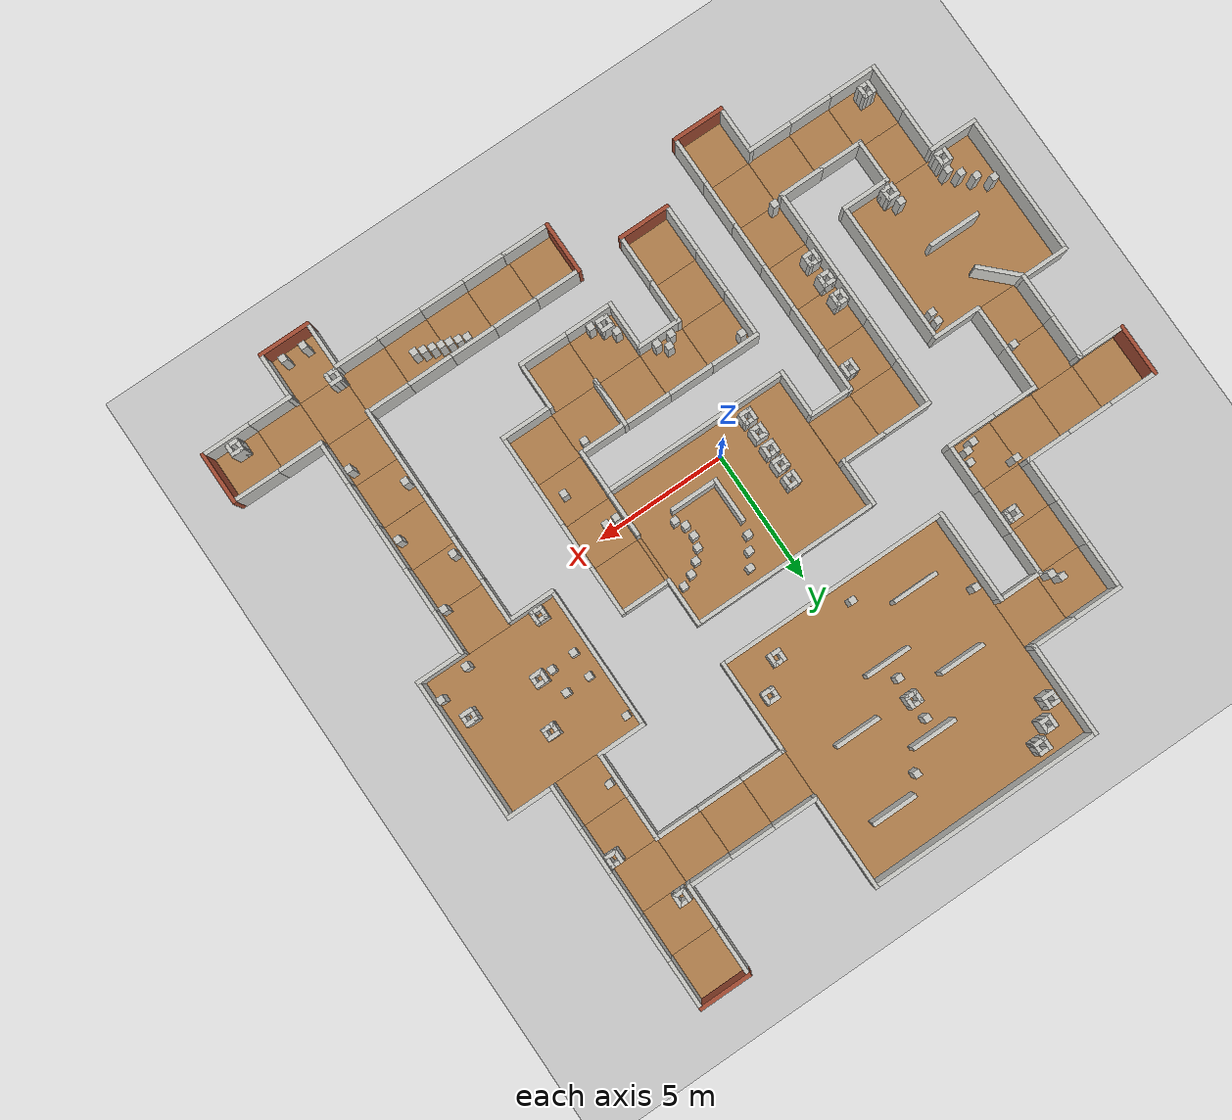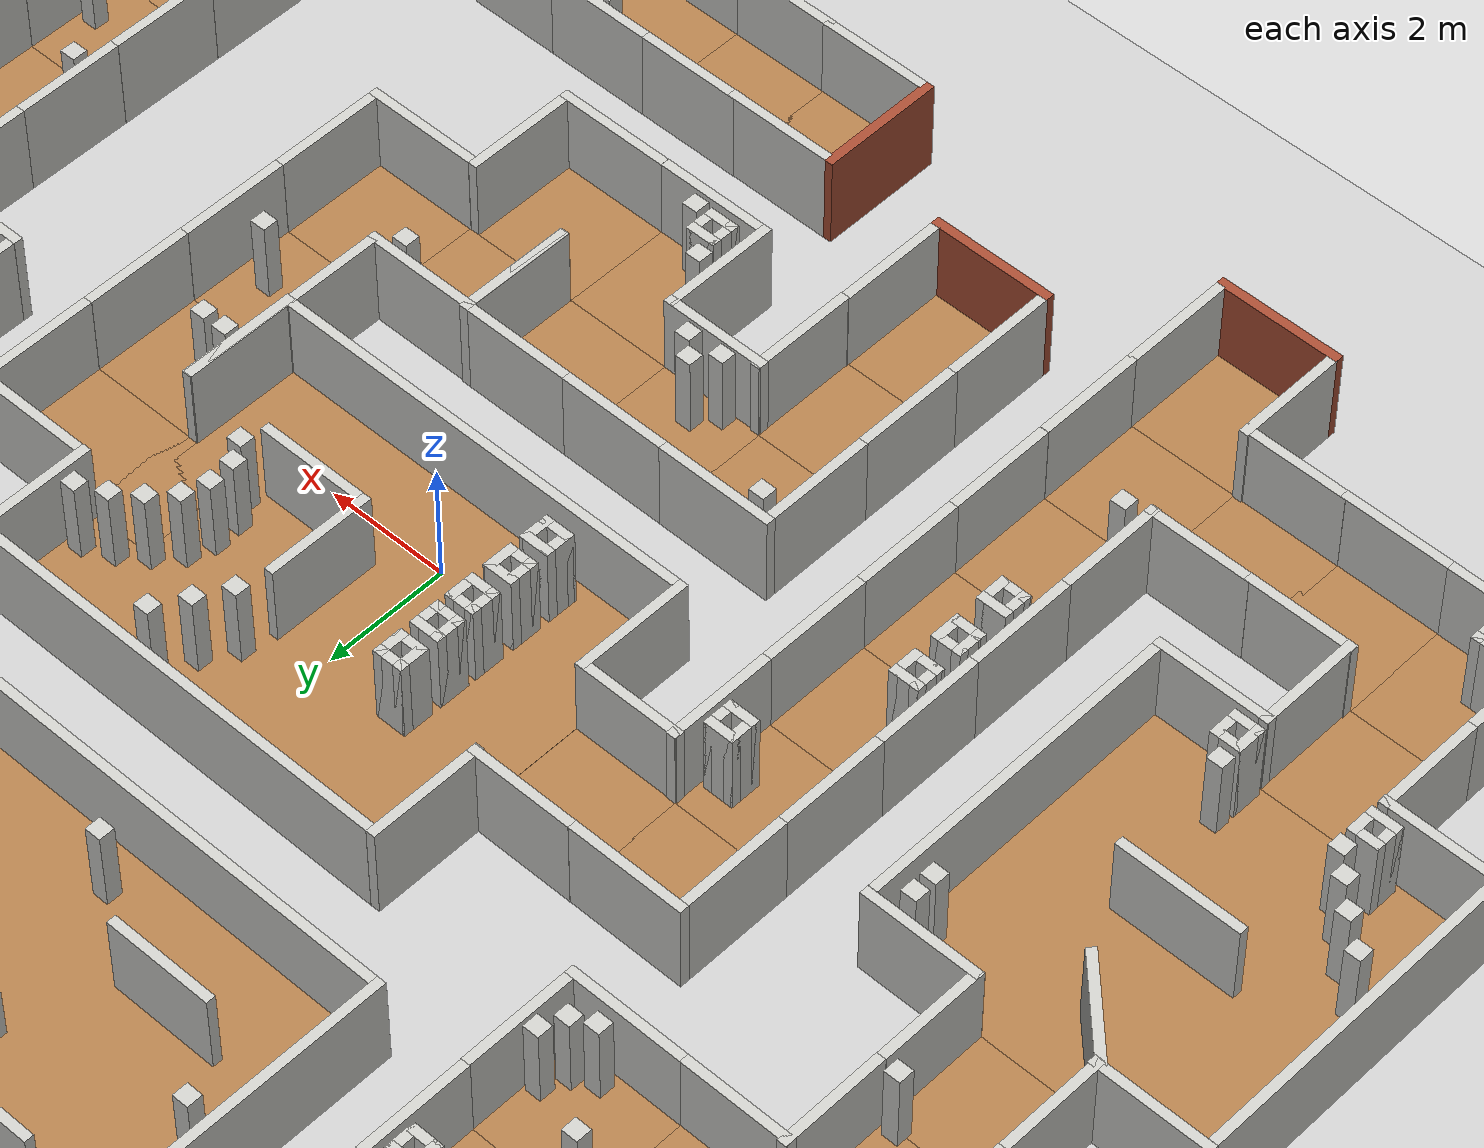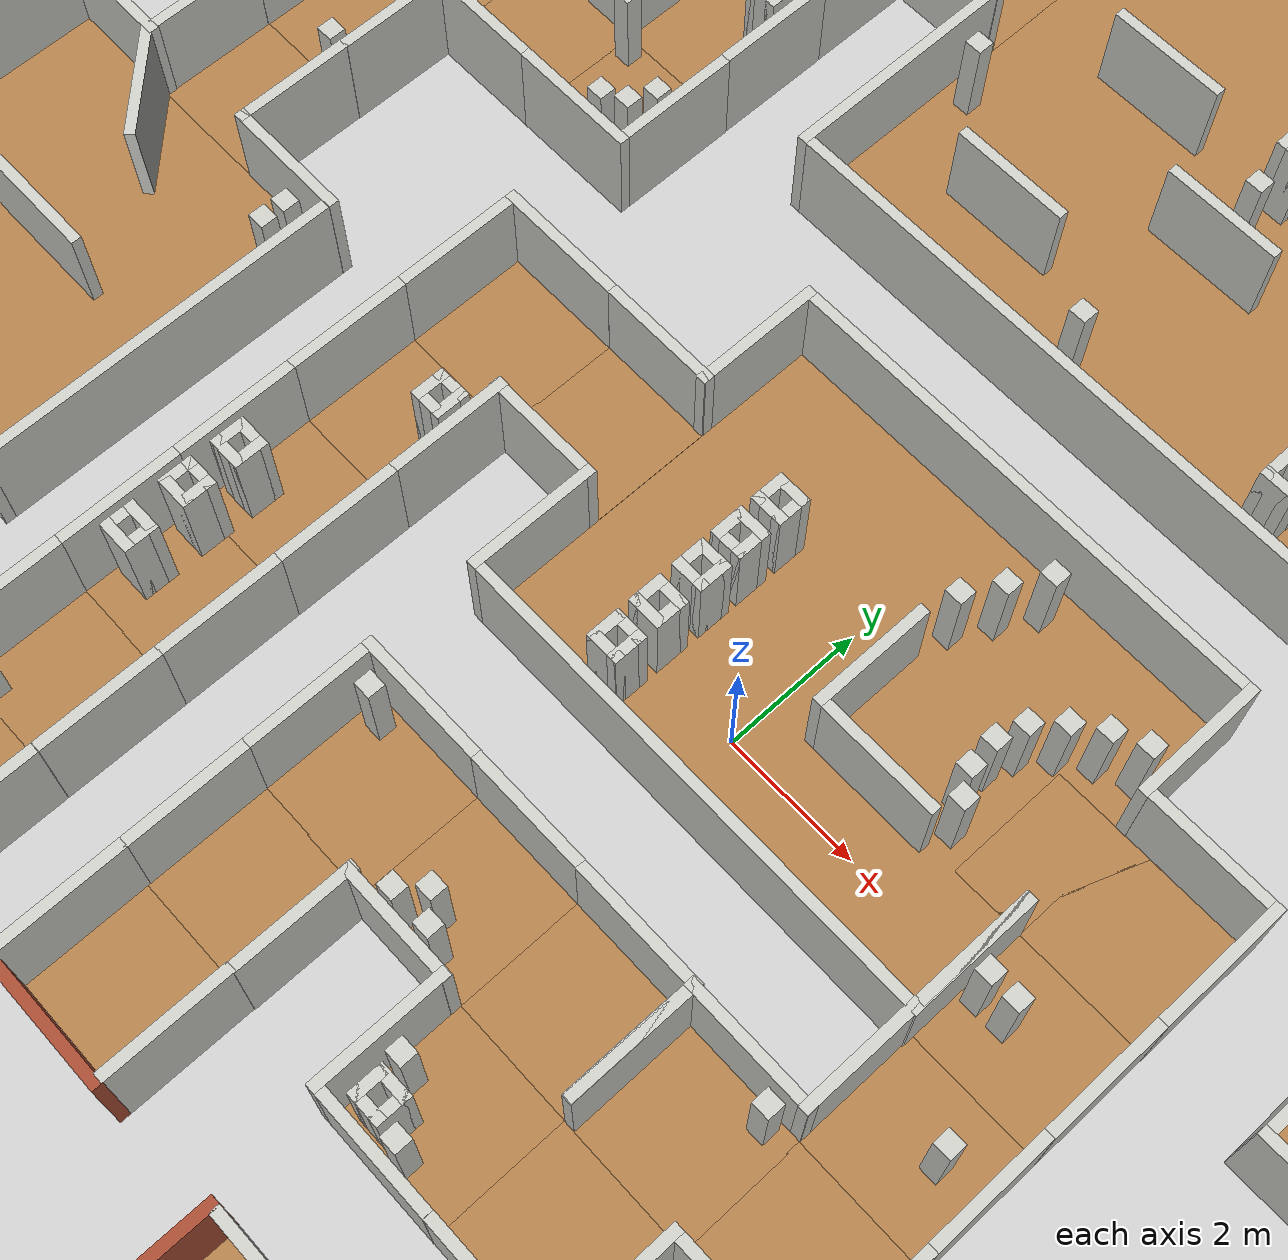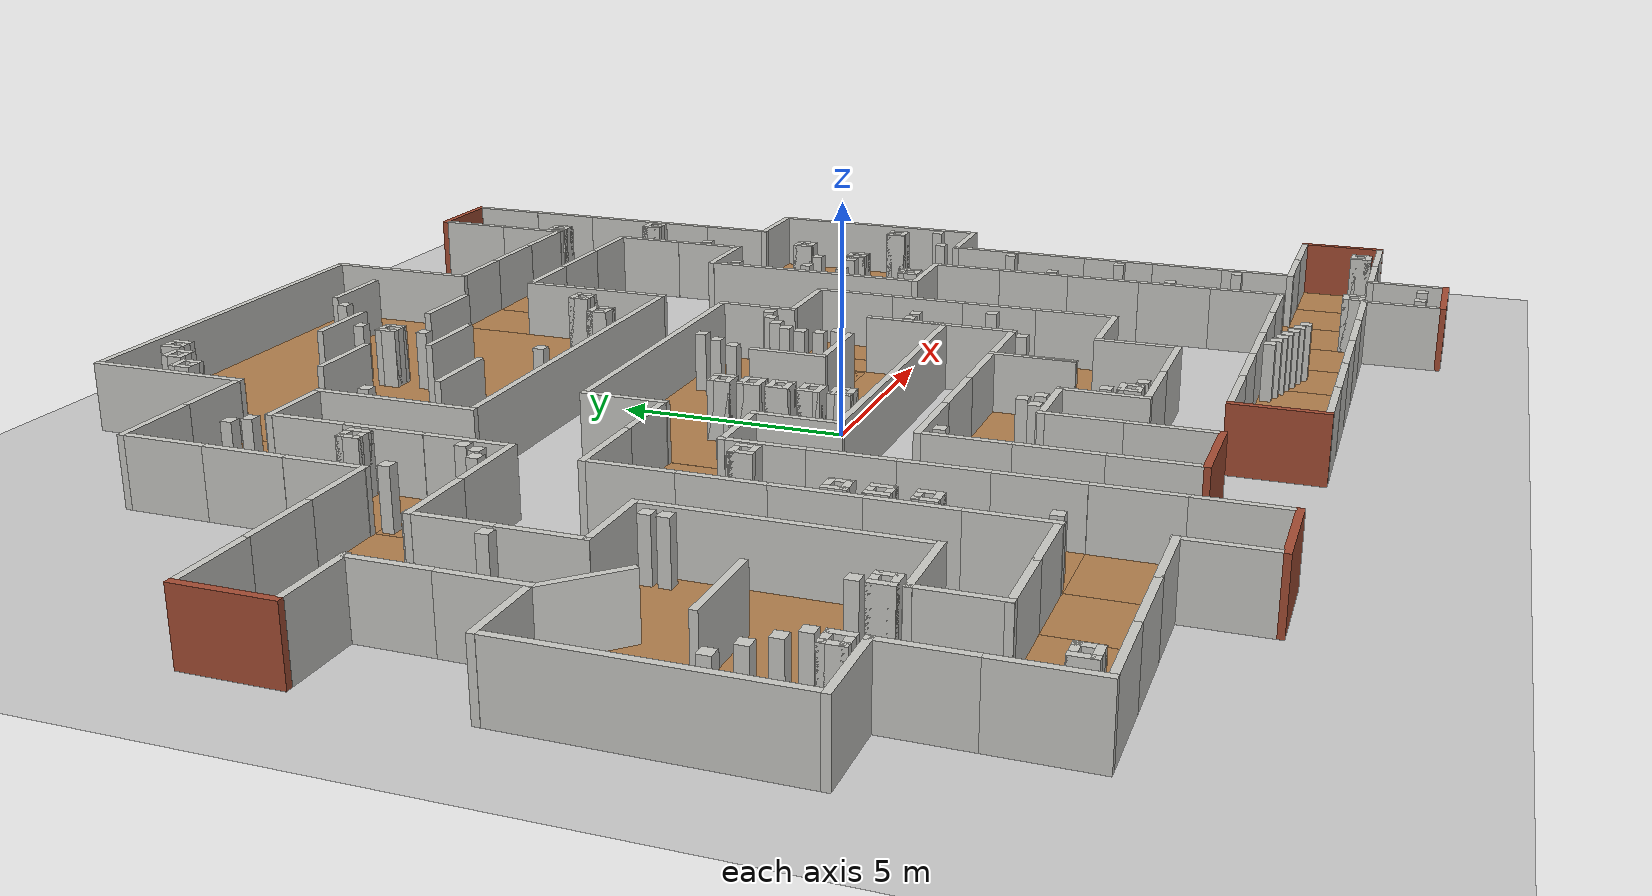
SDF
<sdf version="1.6">
 <world name="default">
  <light name="sun" type="directional">
   <pose>0 0 10 0 -0 0</pose>
   <diffuse>0.8 0.8 0.8 1</diffuse>
   <specular>0.1 0.1 0.1 1</specular>
   <attenuation>
    <range>1000</range>
    <constant>0.9</constant>
    <linear>0.01</linear>
    <quadratic>0.001</quadratic>
   </attenuation>
   <direction>-0.5 0.5 -1</direction>
  </light>
  <model name="ground_plane">
   <static>1</static>
   <link name="link">
    <collision name="collision">
     <geometry><plane><normal>0 0 1</normal><size>100 100</size></plane></geometry>
     <surface><friction><ode><mu>100</mu><mu2>50</mu2></ode></friction></surface>
    </collision>
    <visual name="visual">
     <cast_shadows>0</cast_shadows>
     <geometry><plane><normal>0 0 1</normal><size>100 100</size></plane></geometry>
     <material>
      <script><uri>file://media/materials/scripts/gazebo.material</uri><name>Gazebo/Grey</name></script>
     </material>
    </visual>
   </link>
  </model>
  <gravity>0 0 -9.8</gravity>
  <magnetic_field>6e-06 2.3e-05 -4.2e-05</magnetic_field>
  <atmosphere type="adiabatic"/>
  <physics name="default_physics" default="0" type="ode">
   <max_step_size>0.001</max_step_size>
   <real_time_factor>1</real_time_factor>
   <real_time_update_rate>1000</real_time_update_rate>
  </physics>
  <scene><ambient>0.4 0.4 0.4 1</ambient><background>0.7 0.7 0.7 1</background><shadows>1</shadows></scene>
  <spherical_coordinates>
   <surface_model>EARTH_WGS84</surface_model>
   <latitude_deg>0</latitude_deg>
   <longitude_deg>0</longitude_deg>
   <elevation>0</elevation>
   <heading_deg>0</heading_deg>
  </spherical_coordinates>
  <model name="nerve_end">
   <pose>-2.33142 -7.13266 0 0 0 -3.14159</pose>
   <link name="Wall_0">
    <collision name="Wall_0_Collision">
     <geometry><box><size>1.76 1.75 0.2</size></box></geometry>
     <pose>0 0 0.1 0 -0 0</pose>
    </collision>
    <visual name="Wall_0_Visual">
     <pose>0 0 0.1 0 -0 0</pose>
     <geometry><box><size>1.76 1.75 0.2</size></box></geometry>
     <material>
      <script><uri>file://media/materials/scripts/gazebo.material</uri><name>Gazebo/Wood</name></script>
      <ambient>1 0.764706 0.305882 1</ambient>
     </material>
    </visual>
    <pose>-0.009 -0.064 0 0 -0 0</pose>
   </link>
   <link name="Wall_2">
    <collision name="Wall_2_Collision">
     <geometry><box><size>1.8 0.15 1.5</size></box></geometry>
     <pose>0 0 0.75 0 -0 0</pose>
    </collision>
    <visual name="Wall_2_Visual">
     <pose>0 0 0.75 0 -0 0</pose>
     <geometry><box><size>1.8 0.15 1.5</size></box></geometry>
     <material>
      <script><uri>file://media/materials/scripts/gazebo.material</uri><name>Gazebo/CeilingTiled</name></script>
      <ambient>1 0.764706 0.305882 1</ambient>
     </material>
    </visual>
    <pose>-0.95 -0.065 0 0 0 -1.5708</pose>
   </link>
   <link name="Wall_4">
    <collision name="Wall_4_Collision">
     <geometry><box><size>1.8 0.15 1.5</size></box></geometry>
     <pose>0 0 0.75 0 -0 0</pose>
    </collision>
    <visual name="Wall_4_Visual">
     <pose>0 0 0.75 0 -0 0</pose>
     <geometry><box><size>1.8 0.15 1.5</size></box></geometry>
     <material>
      <script><uri>file://media/materials/scripts/gazebo.material</uri><name>Gazebo/CeilingTiled</name></script>
      <ambient>1 0.764706 0.305882 1</ambient>
     </material>
    </visual>
    <pose>0.95 -0.065 0 0 0 -1.5708</pose>
   </link>
   <link name="Wall_6">
    <collision name="Wall_6_Collision">
     <geometry><box><size>2.05 0.15 1.5</size></box></geometry>
     <pose>0 0 0.75 0 -0 0</pose>
    </collision>
    <visual name="Wall_6_Visual">
     <pose>0 0 0.75 0 -0 0</pose>
     <geometry><box><size>2.05 0.15 1.5</size></box></geometry>
     <material>
      <script><uri>file://media/materials/scripts/gazebo.material</uri><name>Gazebo/Bricks</name></script>
      <ambient>0.996078 0.47451 0.0196078 1</ambient>
     </material>
    </visual>
    <pose>0 0.89 0 0 -0 0</pose>
   </link>
   <static>1</static>
  </model>
  <model name="nerve_straight_4">
   <pose>-2.32642 -5.32807 0 0 -0 0</pose>
   <link name="Wall_0">
    <collision name="Wall_0_Collision">
     <geometry><box><size>1.76 1.75 0.2</size></box></geometry>
     <pose>0 0 0.1 0 -0 0</pose>
    </collision>
    <visual name="Wall_0_Visual">
     <pose>0 0 0.1 0 -0 0</pose>
     <geometry><box><size>1.76 1.75 0.2</size></box></geometry>
     <material>
      <script><uri>file://media/materials/scripts/gazebo.material</uri><name>Gazebo/Wood</name></script>
      <ambient>1 0.764706 0.305882 1</ambient>
     </material>
    </visual>
    <pose>0.005 -0.002 0 0 -0 3.14159</pose>
   </link>
   <link name="Wall_2">
    <collision name="Wall_2_Collision">
     <geometry><box><size>1.75 0.15 1.5</size></box></geometry>
     <pose>0 0 0.75 0 -0 0</pose>
    </collision>
    <visual name="Wall_2_Visual">
     <pose>0 0 0.75 0 -0 0</pose>
     <geometry><box><size>1.75 0.15 1.5</size></box></geometry>
     <material>
      <script><uri>file://media/materials/scripts/gazebo.material</uri><name>Gazebo/CeilingTiled</name></script>
      <ambient>1 0.764706 0.305882 1</ambient>
     </material>
    </visual>
    <pose>-0.955 0.002 0 0 0 -1.5708</pose>
   </link>
   <link name="Wall_4">
    <collision name="Wall_4_Collision">
     <geometry><box><size>1.75 0.15 1.5</size></box></geometry>
     <pose>0 0 0.75 0 -0 0</pose>
    </collision>
    <visual name="Wall_4_Visual">
     <pose>0 0 0.75 0 -0 0</pose>
     <geometry><box><size>1.75 0.15 1.5</size></box></geometry>
     <material>
      <script><uri>file://media/materials/scripts/gazebo.material</uri><name>Gazebo/CeilingTiled</name></script>
      <ambient>1 0.764706 0.305882 1</ambient>
     </material>
    </visual>
    <pose>0.955 0.002 0 0 0 -1.5708</pose>
   </link>
   <static>1</static>
  </model>
  <model name="nerve_corner_4">
   <pose>-2.40033 -3.51919 0 0 -0 0</pose>
   <link name="Wall_0">
    <collision name="Wall_0_Collision">
     <geometry><box><size>1.76 1.75 0.2</size></box></geometry>
     <pose>0 0 0.1 0 -0 0</pose>
    </collision>
    <visual name="Wall_0_Visual">
     <pose>0 0 0.1 0 -0 0</pose>
     <geometry><box><size>1.76 1.75 0.2</size></box></geometry>
     <material>
      <script><uri>file://media/materials/scripts/gazebo.material</uri><name>Gazebo/Wood</name></script>
      <ambient>1 0.764706 0.305882 1</ambient>
     </material>
    </visual>
    <pose>0.077507 -0.077007 0 0 -0 3.14159</pose>
   </link>
   <link name="Wall_2">
    <collision name="Wall_2_Collision">
     <geometry><box><size>1.75 0.15 1.5</size></box></geometry>
     <pose>0 0 0.75 0 -0 0</pose>
    </collision>
    <visual name="Wall_2_Visual">
     <pose>0 0 0.75 0 -0 0</pose>
     <geometry><box><size>1.75 0.15 1.5</size></box></geometry>
     <material>
      <script><uri>file://media/materials/scripts/gazebo.material</uri><name>Gazebo/CeilingTiled</name></script>
      <ambient>1 0.764706 0.305882 1</ambient>
     </material>
    </visual>
    <pose>-0.882493 -0.073007 0 0 0 -1.5708</pose>
   </link>
   <link name="Wall_4">
    <collision name="Wall_4_Collision">
     <geometry><box><size>1.91042 0.15 1.5</size></box></geometry>
     <pose>0 0 0.75 0 -0 0</pose>
    </collision>
    <visual name="Wall_4_Visual">
     <pose>0 0 0.75 0 -0 0</pose>
     <geometry><box><size>1.91042 0.15 1.5</size></box></geometry>
     <material>
      <script><uri>file://media/materials/scripts/gazebo.material</uri><name>Gazebo/CeilingTiled</name></script>
      <ambient>1 0.764706 0.305882 1</ambient>
     </material>
    </visual>
    <pose>-0.002284 0.876825 0 0 -0 3.1414</pose>
   </link>
   <static>1</static>
  </model>
  <model name="nerve_straight_7">
   <pose>-0.5793 -3.59925 0 0 0 -1.5708</pose>
   <link name="Wall_0">
    <collision name="Wall_0_Collision">
     <geometry><box><size>1.76 1.75 0.2</size></box></geometry>
     <pose>0 0 0.1 0 -0 0</pose>
    </collision>
    <visual name="Wall_0_Visual">
     <pose>0 0 0.1 0 -0 0</pose>
     <geometry><box><size>1.76 1.75 0.2</size></box></geometry>
     <material>
      <script><uri>file://media/materials/scripts/gazebo.material</uri><name>Gazebo/Wood</name></script>
      <ambient>1 0.764706 0.305882 1</ambient>
     </material>
    </visual>
    <pose>0.005 -0.002 0 0 -0 3.14159</pose>
   </link>
   <link name="Wall_2">
    <collision name="Wall_2_Collision">
     <geometry><box><size>1.75 0.15 1.5</size></box></geometry>
     <pose>0 0 0.75 0 -0 0</pose>
    </collision>
    <visual name="Wall_2_Visual">
     <pose>0 0 0.75 0 -0 0</pose>
     <geometry><box><size>1.75 0.15 1.5</size></box></geometry>
     <material>
      <script><uri>file://media/materials/scripts/gazebo.material</uri><name>Gazebo/CeilingTiled</name></script>
      <ambient>1 0.764706 0.305882 1</ambient>
     </material>
    </visual>
    <pose>-0.955 0.002 0 0 0 -1.5708</pose>
   </link>
   <link name="Wall_4">
    <collision name="Wall_4_Collision">
     <geometry><box><size>1.75 0.15 1.5</size></box></geometry>
     <pose>0 0 0.75 0 -0 0</pose>
    </collision>
    <visual name="Wall_4_Visual">
     <pose>0 0 0.75 0 -0 0</pose>
     <geometry><box><size>1.75 0.15 1.5</size></box></geometry>
     <material>
      <script><uri>file://media/materials/scripts/gazebo.material</uri><name>Gazebo/CeilingTiled</name></script>
      <ambient>1 0.764706 0.305882 1</ambient>
     </material>
    </visual>
    <pose>0.955 0.002 0 0 0 -1.5708</pose>
   </link>
   <static>1</static>
  </model>
  <model name="nerve_corner_5">
   <pose>1.24131 -3.5279 0 0 0 -1.5708</pose>
   <link name="Wall_0">
    <collision name="Wall_0_Collision">
     <geometry><box><size>1.76 1.75 0.2</size></box></geometry>
     <pose>0 0 0.1 0 -0 0</pose>
    </collision>
    <visual name="Wall_0_Visual">
     <pose>0 0 0.1 0 -0 0</pose>
     <geometry><box><size>1.76 1.75 0.2</size></box></geometry>
     <material>
      <script><uri>file://media/materials/scripts/gazebo.material</uri><name>Gazebo/Wood</name></script>
      <ambient>1 0.764706 0.305882 1</ambient>
     </material>
    </visual>
    <pose>0.077507 -0.077007 0 0 -0 3.14159</pose>
   </link>
   <link name="Wall_2">
    <collision name="Wall_2_Collision">
     <geometry><box><size>1.75 0.15 1.5</size></box></geometry>
     <pose>0 0 0.75 0 -0 0</pose>
    </collision>
    <visual name="Wall_2_Visual">
     <pose>0 0 0.75 0 -0 0</pose>
     <geometry><box><size>1.75 0.15 1.5</size></box></geometry>
     <material>
      <script><uri>file://media/materials/scripts/gazebo.material</uri><name>Gazebo/CeilingTiled</name></script>
      <ambient>1 0.764706 0.305882 1</ambient>
     </material>
    </visual>
    <pose>-0.882493 -0.073007 0 0 0 -1.5708</pose>
   </link>
   <link name="Wall_4">
    <collision name="Wall_4_Collision">
     <geometry><box><size>1.91042 0.15 1.5</size></box></geometry>
     <pose>0 0 0.75 0 -0 0</pose>
    </collision>
    <visual name="Wall_4_Visual">
     <pose>0 0 0.75 0 -0 0</pose>
     <geometry><box><size>1.91042 0.15 1.5</size></box></geometry>
     <material>
      <script><uri>file://media/materials/scripts/gazebo.material</uri><name>Gazebo/CeilingTiled</name></script>
      <ambient>1 0.764706 0.305882 1</ambient>
     </material>
    </visual>
    <pose>-0.002284 0.876825 0 0 -0 3.1414</pose>
   </link>
   <static>1</static>
  </model>
  <model name="nerve_corner_6">
   <pose>1.09271 -5.44009 0 0 -0 1.57079</pose>
   <link name="Wall_0">
    <collision name="Wall_0_Collision">
     <geometry><box><size>1.76 1.75 0.2</size></box></geometry>
     <pose>0 0 0.1 0 -0 0</pose>
    </collision>
    <visual name="Wall_0_Visual">
     <pose>0 0 0.1 0 -0 0</pose>
     <geometry><box><size>1.76 1.75 0.2</size></box></geometry>
     <material>
      <script><uri>file://media/materials/scripts/gazebo.material</uri><name>Gazebo/Wood</name></script>
      <ambient>1 0.764706 0.305882 1</ambient>
     </material>
    </visual>
    <pose>0.077507 -0.077007 0 0 -0 3.14159</pose>
   </link>
   <link name="Wall_2">
    <collision name="Wall_2_Collision">
     <geometry><box><size>1.75 0.15 1.5</size></box></geometry>
     <pose>0 0 0.75 0 -0 0</pose>
    </collision>
    <visual name="Wall_2_Visual">
     <pose>0 0 0.75 0 -0 0</pose>
     <geometry><box><size>1.75 0.15 1.5</size></box></geometry>
     <material>
      <script><uri>file://media/materials/scripts/gazebo.material</uri><name>Gazebo/CeilingTiled</name></script>
      <ambient>1 0.764706 0.305882 1</ambient>
     </material>
    </visual>
    <pose>-0.882493 -0.073007 0 0 0 -1.5708</pose>
   </link>
   <link name="Wall_4">
    <collision name="Wall_4_Collision">
     <geometry><box><size>1.91042 0.15 1.5</size></box></geometry>
     <pose>0 0 0.75 0 -0 0</pose>
    </collision>
    <visual name="Wall_4_Visual">
     <pose>0 0 0.75 0 -0 0</pose>
     <geometry><box><size>1.91042 0.15 1.5</size></box></geometry>
     <material>
      <script><uri>file://media/materials/scripts/gazebo.material</uri><name>Gazebo/CeilingTiled</name></script>
      <ambient>1 0.764706 0.305882 1</ambient>
     </material>
    </visual>
    <pose>-0.002284 0.876825 0 0 -0 3.1414</pose>
   </link>
   <static>1</static>
  </model>
  <model name="nerve_corner_7">
   <pose>3.00607 -3.54167 0 0 -0 0</pose>
   <link name="Wall_0">
    <collision name="Wall_0_Collision">
     <geometry><box><size>1.76 1.75 0.2</size></box></geometry>
     <pose>0 0 0.1 0 -0 0</pose>
    </collision>
    <visual name="Wall_0_Visual">
     <pose>0 0 0.1 0 -0 0</pose>
     <geometry><box><size>1.76 1.75 0.2</size></box></geometry>
     <material>
      <script><uri>file://media/materials/scripts/gazebo.material</uri><name>Gazebo/Wood</name></script>
      <ambient>1 0.764706 0.305882 1</ambient>
     </material>
    </visual>
    <pose>0.077507 -0.077007 0 0 -0 3.14159</pose>
   </link>
   <link name="Wall_2">
    <collision name="Wall_2_Collision">
     <geometry><box><size>1.75 0.15 1.5</size></box></geometry>
     <pose>0 0 0.75 0 -0 0</pose>
    </collision>
    <visual name="Wall_2_Visual">
     <pose>0 0 0.75 0 -0 0</pose>
     <geometry><box><size>1.75 0.15 1.5</size></box></geometry>
     <material>
      <script><uri>file://media/materials/scripts/gazebo.material</uri><name>Gazebo/CeilingTiled</name></script>
      <ambient>1 0.764706 0.305882 1</ambient>
     </material>
    </visual>
    <pose>-0.882493 -0.073007 0 0 0 -1.5708</pose>
   </link>
   <link name="Wall_4">
    <collision name="Wall_4_Collision">
     <geometry><box><size>1.91042 0.15 1.5</size></box></geometry>
     <pose>0 0 0.75 0 -0 0</pose>
    </collision>
    <visual name="Wall_4_Visual">
     <pose>0 0 0.75 0 -0 0</pose>
     <geometry><box><size>1.91042 0.15 1.5</size></box></geometry>
     <material>
      <script><uri>file://media/materials/scripts/gazebo.material</uri><name>Gazebo/CeilingTiled</name></script>
      <ambient>1 0.764706 0.305882 1</ambient>
     </material>
    </visual>
    <pose>-0.002284 0.876825 0 0 -0 3.1414</pose>
   </link>
   <static>1</static>
  </model>
  <model name="nerve_corner_8">
   <pose>2.996 -5.44292 0 0 -0 3.14159</pose>
   <link name="Wall_0">
    <collision name="Wall_0_Collision">
     <geometry><box><size>1.76 1.75 0.2</size></box></geometry>
     <pose>0 0 0.1 0 -0 0</pose>
    </collision>
    <visual name="Wall_0_Visual">
     <pose>0 0 0.1 0 -0 0</pose>
     <geometry><box><size>1.76 1.75 0.2</size></box></geometry>
     <material>
      <script><uri>file://media/materials/scripts/gazebo.material</uri><name>Gazebo/Wood</name></script>
      <ambient>1 0.764706 0.305882 1</ambient>
     </material>
    </visual>
    <pose>0.077507 -0.077007 0 0 -0 3.14159</pose>
   </link>
   <link name="Wall_2">
    <collision name="Wall_2_Collision">
     <geometry><box><size>1.75 0.15 1.5</size></box></geometry>
     <pose>0 0 0.75 0 -0 0</pose>
    </collision>
    <visual name="Wall_2_Visual">
     <pose>0 0 0.75 0 -0 0</pose>
     <geometry><box><size>1.75 0.15 1.5</size></box></geometry>
     <material>
      <script><uri>file://media/materials/scripts/gazebo.material</uri><name>Gazebo/CeilingTiled</name></script>
      <ambient>1 0.764706 0.305882 1</ambient>
     </material>
    </visual>
    <pose>-0.882493 -0.073007 0 0 0 -1.5708</pose>
   </link>
   <link name="Wall_4">
    <collision name="Wall_4_Collision">
     <geometry><box><size>1.91042 0.15 1.5</size></box></geometry>
     <pose>0 0 0.75 0 -0 0</pose>
    </collision>
    <visual name="Wall_4_Visual">
     <pose>0 0 0.75 0 -0 0</pose>
     <geometry><box><size>1.91042 0.15 1.5</size></box></geometry>
     <material>
      <script><uri>file://media/materials/scripts/gazebo.material</uri><name>Gazebo/CeilingTiled</name></script>
      <ambient>1 0.764706 0.305882 1</ambient>
     </material>
    </visual>
    <pose>-0.002284 0.876825 0 0 -0 3.1414</pose>
   </link>
   <static>1</static>
  </model>
  <model name="nerve_corner_8_clone">
   <pose>4.90397 -3.68999 0 0 0 -3.14159</pose>
   <link name="Wall_0">
    <collision name="Wall_0_Collision">
     <geometry><box><size>1.76 1.75 0.2</size></box></geometry>
     <pose>0 0 0.1 0 -0 0</pose>
    </collision>
    <visual name="Wall_0_Visual">
     <pose>0 0 0.1 0 -0 0</pose>
     <geometry><box><size>1.76 1.75 0.2</size></box></geometry>
     <material>
      <script><uri>file://media/materials/scripts/gazebo.material</uri><name>Gazebo/Wood</name></script>
      <ambient>1 0.764706 0.305882 1</ambient>
     </material>
    </visual>
    <pose>0.077507 -0.077007 0 0 -0 3.14159</pose>
   </link>
   <link name="Wall_2">
    <collision name="Wall_2_Collision">
     <geometry><box><size>1.75 0.15 1.5</size></box></geometry>
     <pose>0 0 0.75 0 -0 0</pose>
    </collision>
    <visual name="Wall_2_Visual">
     <pose>0 0 0.75 0 -0 0</pose>
     <geometry><box><size>1.75 0.15 1.5</size></box></geometry>
     <material>
      <script><uri>file://media/materials/scripts/gazebo.material</uri><name>Gazebo/CeilingTiled</name></script>
      <ambient>1 0.764706 0.305882 1</ambient>
     </material>
    </visual>
    <pose>-0.882493 -0.073007 0 0 0 -1.5708</pose>
   </link>
   <link name="Wall_4">
    <collision name="Wall_4_Collision">
     <geometry><box><size>1.91042 0.15 1.5</size></box></geometry>
     <pose>0 0 0.75 0 -0 0</pose>
    </collision>
    <visual name="Wall_4_Visual">
     <pose>0 0 0.75 0 -0 0</pose>
     <geometry><box><size>1.91042 0.15 1.5</size></box></geometry>
     <material>
      <script><uri>file://media/materials/scripts/gazebo.material</uri><name>Gazebo/CeilingTiled</name></script>
      <ambient>1 0.764706 0.305882 1</ambient>
     </material>
    </visual>
    <pose>-0.002284 0.876825 0 0 -0 3.1414</pose>
   </link>
   <static>1</static>
  </model>
  <model name="nerve_straight_8">
   <pose>4.83321 -1.87129 0 0 -0 0</pose>
   <link name="Wall_0">
    <collision name="Wall_0_Collision">
     <geometry><box><size>1.76 1.75 0.2</size></box></geometry>
     <pose>0 0 0.1 0 -0 0</pose>
    </collision>
    <visual name="Wall_0_Visual">
     <pose>0 0 0.1 0 -0 0</pose>
     <geometry><box><size>1.76 1.75 0.2</size></box></geometry>
     <material>
      <script><uri>file://media/materials/scripts/gazebo.material</uri><name>Gazebo/Wood</name></script>
      <ambient>1 0.764706 0.305882 1</ambient>
     </material>
    </visual>
    <pose>0.005 -0.002 0 0 -0 3.14159</pose>
   </link>
   <link name="Wall_2">
    <collision name="Wall_2_Collision">
     <geometry><box><size>1.75 0.15 1.5</size></box></geometry>
     <pose>0 0 0.75 0 -0 0</pose>
    </collision>
    <visual name="Wall_2_Visual">
     <pose>0 0 0.75 0 -0 0</pose>
     <geometry><box><size>1.75 0.15 1.5</size></box></geometry>
     <material>
      <script><uri>file://media/materials/scripts/gazebo.material</uri><name>Gazebo/CeilingTiled</name></script>
      <ambient>1 0.764706 0.305882 1</ambient>
     </material>
    </visual>
    <pose>-0.955 0.002 0 0 0 -1.5708</pose>
   </link>
   <link name="Wall_4">
    <collision name="Wall_4_Collision">
     <geometry><box><size>1.75 0.15 1.5</size></box></geometry>
     <pose>0 0 0.75 0 -0 0</pose>
    </collision>
    <visual name="Wall_4_Visual">
     <pose>0 0 0.75 0 -0 0</pose>
     <geometry><box><size>1.75 0.15 1.5</size></box></geometry>
     <material>
      <script><uri>file://media/materials/scripts/gazebo.material</uri><name>Gazebo/CeilingTiled</name></script>
      <ambient>1 0.764706 0.305882 1</ambient>
     </material>
    </visual>
    <pose>0.955 0.002 0 0 0 -1.5708</pose>
   </link>
   <static>1</static>
  </model>
  <model name="nerve_straight_8_clone">
   <pose>4.83651 -0.139064 0 0 -0 0</pose>
   <link name="Wall_0">
    <collision name="Wall_0_Collision">
     <geometry><box><size>1.76 1.75 0.2</size></box></geometry>
     <pose>0 0 0.1 0 -0 0</pose>
    </collision>
    <visual name="Wall_0_Visual">
     <pose>0 0 0.1 0 -0 0</pose>
     <geometry><box><size>1.76 1.75 0.2</size></box></geometry>
     <material>
      <script><uri>file://media/materials/scripts/gazebo.material</uri><name>Gazebo/Wood</name></script>
      <ambient>1 0.764706 0.305882 1</ambient>
     </material>
    </visual>
    <pose>0.005 -0.002 0 0 -0 3.14159</pose>
   </link>
   <link name="Wall_2">
    <collision name="Wall_2_Collision">
     <geometry><box><size>1.75 0.15 1.5</size></box></geometry>
     <pose>0 0 0.75 0 -0 0</pose>
    </collision>
    <visual name="Wall_2_Visual">
     <pose>0 0 0.75 0 -0 0</pose>
     <geometry><box><size>1.75 0.15 1.5</size></box></geometry>
     <material>
      <script><uri>file://media/materials/scripts/gazebo.material</uri><name>Gazebo/CeilingTiled</name></script>
      <ambient>1 0.764706 0.305882 1</ambient>
     </material>
    </visual>
    <pose>-0.955 0.002 0 0 0 -1.5708</pose>
   </link>
   <link name="Wall_4">
    <collision name="Wall_4_Collision">
     <geometry><box><size>1.75 0.15 1.5</size></box></geometry>
     <pose>0 0 0.75 0 -0 0</pose>
    </collision>
    <visual name="Wall_4_Visual">
     <pose>0 0 0.75 0 -0 0</pose>
     <geometry><box><size>1.75 0.15 1.5</size></box></geometry>
     <material>
      <script><uri>file://media/materials/scripts/gazebo.material</uri><name>Gazebo/CeilingTiled</name></script>
      <ambient>1 0.764706 0.305882 1</ambient>
     </material>
    </visual>
    <pose>0.955 0.002 0 0 0 -1.5708</pose>
   </link>
   <static>1</static>
  </model>
  <model name="nerve_corner_5_clone">
   <pose>4.91717 1.68936 0 0 0 -1.5708</pose>
   <link name="Wall_0">
    <collision name="Wall_0_Collision">
     <geometry><box><size>1.76 1.75 0.2</size></box></geometry>
     <pose>0 0 0.1 0 -0 0</pose>
    </collision>
    <visual name="Wall_0_Visual">
     <pose>0 0 0.1 0 -0 0</pose>
     <geometry><box><size>1.76 1.75 0.2</size></box></geometry>
     <material>
      <script><uri>file://media/materials/scripts/gazebo.material</uri><name>Gazebo/Wood</name></script>
      <ambient>1 0.764706 0.305882 1</ambient>
     </material>
    </visual>
    <pose>0.077507 -0.077007 0 0 -0 3.14159</pose>
   </link>
   <link name="Wall_2">
    <collision name="Wall_2_Collision">
     <geometry><box><size>1.75 0.15 1.5</size></box></geometry>
     <pose>0 0 0.75 0 -0 0</pose>
    </collision>
    <visual name="Wall_2_Visual">
     <pose>0 0 0.75 0 -0 0</pose>
     <geometry><box><size>1.75 0.15 1.5</size></box></geometry>
     <material>
      <script><uri>file://media/materials/scripts/gazebo.material</uri><name>Gazebo/CeilingTiled</name></script>
      <ambient>1 0.764706 0.305882 1</ambient>
     </material>
    </visual>
    <pose>-0.882493 -0.073007 0 0 0 -1.5708</pose>
   </link>
   <link name="Wall_4">
    <collision name="Wall_4_Collision">
     <geometry><box><size>1.91042 0.15 1.5</size></box></geometry>
     <pose>0 0 0.75 0 -0 0</pose>
    </collision>
    <visual name="Wall_4_Visual">
     <pose>0 0 0.75 0 -0 0</pose>
     <geometry><box><size>1.91042 0.15 1.5</size></box></geometry>
     <material>
      <script><uri>file://media/materials/scripts/gazebo.material</uri><name>Gazebo/CeilingTiled</name></script>
      <ambient>1 0.764706 0.305882 1</ambient>
     </material>
    </visual>
    <pose>-0.002284 0.876825 0 0 -0 3.1414</pose>
   </link>
   <static>1</static>
  </model>
  <model name="nerve_room_3x4">
   <pose>0.322043 1.61667 0 0 0 -1.57079</pose>
   <link name="Wall_11">
    <collision name="Wall_11_Collision">
     <geometry><box><size>7 0.15 1.5</size></box></geometry>
     <pose>0 0 0.75 0 -0 0</pose>
    </collision>
    <visual name="Wall_11_Visual">
     <pose>0 0 0.75 0 -0 0</pose>
     <geometry><box><size>7 0.15 1.5</size></box></geometry>
     <material>
      <script><uri>file://media/materials/scripts/gazebo.material</uri><name>Gazebo/CeilingTiled</name></script>
      <ambient>1 0.764706 0.305882 1</ambient>
     </material>
    </visual>
    <pose>-2.69862 -0.000423 0 0 0 -1.5708</pose>
   </link>
   <link name="Wall_13">
    <collision name="Wall_13_Collision">
     <geometry><box><size>7 0.15 1.5</size></box></geometry>
     <pose>0 0 0.75 0 -0 0</pose>
    </collision>
    <visual name="Wall_13_Visual">
     <pose>0 0 0.75 0 -0 0</pose>
     <geometry><box><size>7 0.15 1.5</size></box></geometry>
     <material>
      <script><uri>file://media/materials/scripts/gazebo.material</uri><name>Gazebo/CeilingTiled</name></script>
      <ambient>1 0.764706 0.305882 1</ambient>
     </material>
    </visual>
    <pose>2.69862 -0.000308 0 0 0 -1.5708</pose>
   </link>
   <link name="Wall_15">
    <collision name="Wall_15_Collision">
     <geometry><box><size>1.9 0.15 1.5</size></box></geometry>
     <pose>0 0 0.75 0 -0 0</pose>
    </collision>
    <visual name="Wall_15_Visual">
     <pose>0 0 0.75 0 -0 0</pose>
     <geometry><box><size>1.9 0.15 1.5</size></box></geometry>
     <material>
      <script><uri>file://media/materials/scripts/gazebo.material</uri><name>Gazebo/CeilingTiled</name></script>
      <ambient>1 0.764706 0.305882 1</ambient>
     </material>
    </visual>
    <pose>-1.82276 -3.57547 0 0 -0 0</pose>
   </link>
   <link name="Wall_17">
    <collision name="Wall_17_Collision">
     <geometry><box><size>1.9 0.15 1.5</size></box></geometry>
     <pose>0 0 0.75 0 -0 0</pose>
    </collision>
    <visual name="Wall_17_Visual">
     <pose>0 0 0.75 0 -0 0</pose>
     <geometry><box><size>1.9 0.15 1.5</size></box></geometry>
     <material>
      <script><uri>file://media/materials/scripts/gazebo.material</uri><name>Gazebo/CeilingTiled</name></script>
      <ambient>1 0.764706 0.305882 1</ambient>
     </material>
    </visual>
    <pose>-1.82217 3.57448 0 0 -0 0</pose>
   </link>
   <link name="Wall_19">
    <collision name="Wall_19_Collision">
     <geometry><box><size>1.9 0.15 1.5</size></box></geometry>
     <pose>0 0 0.75 0 -0 0</pose>
    </collision>
    <visual name="Wall_19_Visual">
     <pose>0 0 0.75 0 -0 0</pose>
     <geometry><box><size>1.9 0.15 1.5</size></box></geometry>
     <material>
      <script><uri>file://media/materials/scripts/gazebo.material</uri><name>Gazebo/CeilingTiled</name></script>
      <ambient>1 0.764706 0.305882 1</ambient>
     </material>
    </visual>
    <pose>1.82197 3.57547 0 0 -0 0</pose>
   </link>
   <link name="Wall_21">
    <collision name="Wall_21_Collision">
     <geometry><box><size>1.9 0.15 1.5</size></box></geometry>
     <pose>0 0 0.75 0 -0 0</pose>
    </collision>
    <visual name="Wall_21_Visual">
     <pose>0 0 0.75 0 -0 0</pose>
     <geometry><box><size>1.9 0.15 1.5</size></box></geometry>
     <material>
      <script><uri>file://media/materials/scripts/gazebo.material</uri><name>Gazebo/CeilingTiled</name></script>
      <ambient>1 0.764706 0.305882 1</ambient>
     </material>
    </visual>
    <pose>1.82281 -3.57503 0 0 -0 0</pose>
   </link>
   <link name="Wall_6">
    <collision name="Wall_6_Collision">
     <geometry><box><size>7 5.25 0.2</size></box></geometry>
     <pose>0 0 0.1 0 -0 0</pose>
    </collision>
    <visual name="Wall_6_Visual">
     <pose>0 0 0.1 0 -0 0</pose>
     <geometry><box><size>7 5.25 0.2</size></box></geometry>
     <material>
      <script><uri>file://media/materials/scripts/gazebo.material</uri><name>Gazebo/Wood</name></script>
      <ambient>1 0.764706 0.305882 1</ambient>
     </material>
    </visual>
    <pose>-0.001169 -0.000255 0 0 -0 1.5708</pose>
   </link>
   <static>1</static>
  </model>
  <model name="nerve_platform_0">
   <pose>3.80884 1.61462 0 0 -0 0</pose>
   <link name="Wall_6">
    <collision name="Wall_6_Collision">
     <geometry><box><size>1.76 1.75 0.2</size></box></geometry>
     <pose>0 0 0.1 0 -0 0</pose>
    </collision>
    <visual name="Wall_6_Visual">
     <pose>0 0 0.1 0 -0 0</pose>
     <geometry><box><size>1.76 1.75 0.2</size></box></geometry>
     <material>
      <script><uri>file://media/materials/scripts/gazebo.material</uri><name>Gazebo/Wood</name></script>
      <ambient>1 0.764706 0.305882 1</ambient>
     </material>
    </visual>
    <pose>0 0 0 0 -0 1.5708</pose>
   </link>
   <static>1</static>
  </model>
  <model name="nerve_straight_9">
   <pose>-4.05488 1.62658 0 0 0 -1.5708</pose>
   <link name="Wall_0">
    <collision name="Wall_0_Collision">
     <geometry><box><size>1.76 1.75 0.2</size></box></geometry>
     <pose>0 0 0.1 0 -0 0</pose>
    </collision>
    <visual name="Wall_0_Visual">
     <pose>0 0 0.1 0 -0 0</pose>
     <geometry><box><size>1.76 1.75 0.2</size></box></geometry>
     <material>
      <script><uri>file://media/materials/scripts/gazebo.material</uri><name>Gazebo/Wood</name></script>
      <ambient>1 0.764706 0.305882 1</ambient>
     </material>
    </visual>
    <pose>0.005 -0.002 0 0 -0 3.14159</pose>
   </link>
   <link name="Wall_2">
    <collision name="Wall_2_Collision">
     <geometry><box><size>1.75 0.15 1.5</size></box></geometry>
     <pose>0 0 0.75 0 -0 0</pose>
    </collision>
    <visual name="Wall_2_Visual">
     <pose>0 0 0.75 0 -0 0</pose>
     <geometry><box><size>1.75 0.15 1.5</size></box></geometry>
     <material>
      <script><uri>file://media/materials/scripts/gazebo.material</uri><name>Gazebo/CeilingTiled</name></script>
      <ambient>1 0.764706 0.305882 1</ambient>
     </material>
    </visual>
    <pose>-0.955 0.002 0 0 0 -1.5708</pose>
   </link>
   <link name="Wall_4">
    <collision name="Wall_4_Collision">
     <geometry><box><size>1.75 0.15 1.5</size></box></geometry>
     <pose>0 0 0.75 0 -0 0</pose>
    </collision>
    <visual name="Wall_4_Visual">
     <pose>0 0 0.75 0 -0 0</pose>
     <geometry><box><size>1.75 0.15 1.5</size></box></geometry>
     <material>
      <script><uri>file://media/materials/scripts/gazebo.material</uri><name>Gazebo/CeilingTiled</name></script>
      <ambient>1 0.764706 0.305882 1</ambient>
     </material>
    </visual>
    <pose>0.955 0.002 0 0 0 -1.5708</pose>
   </link>
   <static>1</static>
  </model>
  <model name="nerve_corner_9">
   <pose>-5.86899 1.703 0 0 -0 0</pose>
   <link name="Wall_0">
    <collision name="Wall_0_Collision">
     <geometry><box><size>1.76 1.75 0.2</size></box></geometry>
     <pose>0 0 0.1 0 -0 0</pose>
    </collision>
    <visual name="Wall_0_Visual">
     <pose>0 0 0.1 0 -0 0</pose>
     <geometry><box><size>1.76 1.75 0.2</size></box></geometry>
     <material>
      <script><uri>file://media/materials/scripts/gazebo.material</uri><name>Gazebo/Wood</name></script>
      <ambient>1 0.764706 0.305882 1</ambient>
     </material>
    </visual>
    <pose>0.077507 -0.077007 0 0 -0 3.14159</pose>
   </link>
   <link name="Wall_2">
    <collision name="Wall_2_Collision">
     <geometry><box><size>1.75 0.15 1.5</size></box></geometry>
     <pose>0 0 0.75 0 -0 0</pose>
    </collision>
    <visual name="Wall_2_Visual">
     <pose>0 0 0.75 0 -0 0</pose>
     <geometry><box><size>1.75 0.15 1.5</size></box></geometry>
     <material>
      <script><uri>file://media/materials/scripts/gazebo.material</uri><name>Gazebo/CeilingTiled</name></script>
      <ambient>1 0.764706 0.305882 1</ambient>
     </material>
    </visual>
    <pose>-0.882493 -0.073007 0 0 0 -1.5708</pose>
   </link>
   <link name="Wall_4">
    <collision name="Wall_4_Collision">
     <geometry><box><size>1.91042 0.15 1.5</size></box></geometry>
     <pose>0 0 0.75 0 -0 0</pose>
    </collision>
    <visual name="Wall_4_Visual">
     <pose>0 0 0.75 0 -0 0</pose>
     <geometry><box><size>1.91042 0.15 1.5</size></box></geometry>
     <material>
      <script><uri>file://media/materials/scripts/gazebo.material</uri><name>Gazebo/CeilingTiled</name></script>
      <ambient>1 0.764706 0.305882 1</ambient>
     </material>
    </visual>
    <pose>-0.002284 0.876825 0 0 -0 3.1414</pose>
   </link>
   <static>1</static>
  </model>
  <model name="nerve_straight_10">
   <pose>-5.79649 -0.117781 0 0 -0 0</pose>
   <link name="Wall_0">
    <collision name="Wall_0_Collision">
     <geometry><box><size>1.76 1.75 0.2</size></box></geometry>
     <pose>0 0 0.1 0 -0 0</pose>
    </collision>
    <visual name="Wall_0_Visual">
     <pose>0 0 0.1 0 -0 0</pose>
     <geometry><box><size>1.76 1.75 0.2</size></box></geometry>
     <material>
      <script><uri>file://media/materials/scripts/gazebo.material</uri><name>Gazebo/Wood</name></script>
      <ambient>1 0.764706 0.305882 1</ambient>
     </material>
    </visual>
    <pose>0.005 -0.002 0 0 -0 3.14159</pose>
   </link>
   <link name="Wall_2">
    <collision name="Wall_2_Collision">
     <geometry><box><size>1.75 0.15 1.5</size></box></geometry>
     <pose>0 0 0.75 0 -0 0</pose>
    </collision>
    <visual name="Wall_2_Visual">
     <pose>0 0 0.75 0 -0 0</pose>
     <geometry><box><size>1.75 0.15 1.5</size></box></geometry>
     <material>
      <script><uri>file://media/materials/scripts/gazebo.material</uri><name>Gazebo/CeilingTiled</name></script>
      <ambient>1 0.764706 0.305882 1</ambient>
     </material>
    </visual>
    <pose>-0.955 0.002 0 0 0 -1.5708</pose>
   </link>
   <link name="Wall_4">
    <collision name="Wall_4_Collision">
     <geometry><box><size>1.75 0.15 1.5</size></box></geometry>
     <pose>0 0 0.75 0 -0 0</pose>
    </collision>
    <visual name="Wall_4_Visual">
     <pose>0 0 0.75 0 -0 0</pose>
     <geometry><box><size>1.75 0.15 1.5</size></box></geometry>
     <material>
      <script><uri>file://media/materials/scripts/gazebo.material</uri><name>Gazebo/CeilingTiled</name></script>
      <ambient>1 0.764706 0.305882 1</ambient>
     </material>
    </visual>
    <pose>0.955 0.002 0 0 0 -1.5708</pose>
   </link>
   <static>1</static>
  </model>
  <model name="nerve_straight_10_clone">
   <pose>-5.79649 -1.8585 0 0 -0 0</pose>
   <link name="Wall_0">
    <collision name="Wall_0_Collision">
     <geometry><box><size>1.76 1.75 0.2</size></box></geometry>
     <pose>0 0 0.1 0 -0 0</pose>
    </collision>
    <visual name="Wall_0_Visual">
     <pose>0 0 0.1 0 -0 0</pose>
     <geometry><box><size>1.76 1.75 0.2</size></box></geometry>
     <material>
      <script><uri>file://media/materials/scripts/gazebo.material</uri><name>Gazebo/Wood</name></script>
      <ambient>1 0.764706 0.305882 1</ambient>
     </material>
    </visual>
    <pose>0.005 -0.002 0 0 -0 3.14159</pose>
   </link>
   <link name="Wall_2">
    <collision name="Wall_2_Collision">
     <geometry><box><size>1.75 0.15 1.5</size></box></geometry>
     <pose>0 0 0.75 0 -0 0</pose>
    </collision>
    <visual name="Wall_2_Visual">
     <pose>0 0 0.75 0 -0 0</pose>
     <geometry><box><size>1.75 0.15 1.5</size></box></geometry>
     <material>
      <script><uri>file://media/materials/scripts/gazebo.material</uri><name>Gazebo/CeilingTiled</name></script>
      <ambient>1 0.764706 0.305882 1</ambient>
     </material>
    </visual>
    <pose>-0.955 0.002 0 0 0 -1.5708</pose>
   </link>
   <link name="Wall_4">
    <collision name="Wall_4_Collision">
     <geometry><box><size>1.75 0.15 1.5</size></box></geometry>
     <pose>0 0 0.75 0 -0 0</pose>
    </collision>
    <visual name="Wall_4_Visual">
     <pose>0 0 0.75 0 -0 0</pose>
     <geometry><box><size>1.75 0.15 1.5</size></box></geometry>
     <material>
      <script><uri>file://media/materials/scripts/gazebo.material</uri><name>Gazebo/CeilingTiled</name></script>
      <ambient>1 0.764706 0.305882 1</ambient>
     </material>
    </visual>
    <pose>0.955 0.002 0 0 0 -1.5708</pose>
   </link>
   <static>1</static>
  </model>
  <model name="nerve_straight_10_clone_0">
   <pose>-5.79649 -3.60725 0 0 -0 0</pose>
   <link name="Wall_0">
    <collision name="Wall_0_Collision">
     <geometry><box><size>1.76 1.75 0.2</size></box></geometry>
     <pose>0 0 0.1 0 -0 0</pose>
    </collision>
    <visual name="Wall_0_Visual">
     <pose>0 0 0.1 0 -0 0</pose>
     <geometry><box><size>1.76 1.75 0.2</size></box></geometry>
     <material>
      <script><uri>file://media/materials/scripts/gazebo.material</uri><name>Gazebo/Wood</name></script>
      <ambient>1 0.764706 0.305882 1</ambient>
     </material>
    </visual>
    <pose>0.005 -0.002 0 0 -0 3.14159</pose>
   </link>
   <link name="Wall_2">
    <collision name="Wall_2_Collision">
     <geometry><box><size>1.75 0.15 1.5</size></box></geometry>
     <pose>0 0 0.75 0 -0 0</pose>
    </collision>
    <visual name="Wall_2_Visual">
     <pose>0 0 0.75 0 -0 0</pose>
     <geometry><box><size>1.75 0.15 1.5</size></box></geometry>
     <material>
      <script><uri>file://media/materials/scripts/gazebo.material</uri><name>Gazebo/CeilingTiled</name></script>
      <ambient>1 0.764706 0.305882 1</ambient>
     </material>
    </visual>
    <pose>-0.955 0.002 0 0 0 -1.5708</pose>
   </link>
   <link name="Wall_4">
    <collision name="Wall_4_Collision">
     <geometry><box><size>1.75 0.15 1.5</size></box></geometry>
     <pose>0 0 0.75 0 -0 0</pose>
    </collision>
    <visual name="Wall_4_Visual">
     <pose>0 0 0.75 0 -0 0</pose>
     <geometry><box><size>1.75 0.15 1.5</size></box></geometry>
     <material>
      <script><uri>file://media/materials/scripts/gazebo.material</uri><name>Gazebo/CeilingTiled</name></script>
      <ambient>1 0.764706 0.305882 1</ambient>
     </material>
    </visual>
    <pose>0.955 0.002 0 0 0 -1.5708</pose>
   </link>
   <static>1</static>
  </model>
  <model name="nerve_straight_10_clone_1">
   <pose>-5.79649 -5.34509 0 0 -0 0</pose>
   <link name="Wall_0">
    <collision name="Wall_0_Collision">
     <geometry><box><size>1.76 1.75 0.2</size></box></geometry>
     <pose>0 0 0.1 0 -0 0</pose>
    </collision>
    <visual name="Wall_0_Visual">
     <pose>0 0 0.1 0 -0 0</pose>
     <geometry><box><size>1.76 1.75 0.2</size></box></geometry>
     <material>
      <script><uri>file://media/materials/scripts/gazebo.material</uri><name>Gazebo/Wood</name></script>
      <ambient>1 0.764706 0.305882 1</ambient>
     </material>
    </visual>
    <pose>0.005 -0.002 0 0 -0 3.14159</pose>
   </link>
   <link name="Wall_2">
    <collision name="Wall_2_Collision">
     <geometry><box><size>1.75 0.15 1.5</size></box></geometry>
     <pose>0 0 0.75 0 -0 0</pose>
    </collision>
    <visual name="Wall_2_Visual">
     <pose>0 0 0.75 0 -0 0</pose>
     <geometry><box><size>1.75 0.15 1.5</size></box></geometry>
     <material>
      <script><uri>file://media/materials/scripts/gazebo.material</uri><name>Gazebo/CeilingTiled</name></script>
      <ambient>1 0.764706 0.305882 1</ambient>
     </material>
    </visual>
    <pose>-0.955 0.002 0 0 0 -1.5708</pose>
   </link>
   <link name="Wall_4">
    <collision name="Wall_4_Collision">
     <geometry><box><size>1.75 0.15 1.5</size></box></geometry>
     <pose>0 0 0.75 0 -0 0</pose>
    </collision>
    <visual name="Wall_4_Visual">
     <pose>0 0 0.75 0 -0 0</pose>
     <geometry><box><size>1.75 0.15 1.5</size></box></geometry>
     <material>
      <script><uri>file://media/materials/scripts/gazebo.material</uri><name>Gazebo/CeilingTiled</name></script>
      <ambient>1 0.764706 0.305882 1</ambient>
     </material>
    </visual>
    <pose>0.955 0.002 0 0 0 -1.5708</pose>
   </link>
   <static>1</static>
  </model>
  <model name="nerve_corner_11">
   <pose>-11.0361 -7.16168 0 0 -0 1.57079</pose>
   <link name="Wall_0">
    <collision name="Wall_0_Collision">
     <geometry><box><size>1.76 1.75 0.2</size></box></geometry>
     <pose>0 0 0.1 0 -0 0</pose>
    </collision>
    <visual name="Wall_0_Visual">
     <pose>0 0 0.1 0 -0 0</pose>
     <geometry><box><size>1.76 1.75 0.2</size></box></geometry>
     <material>
      <script><uri>file://media/materials/scripts/gazebo.material</uri><name>Gazebo/Wood</name></script>
      <ambient>1 0.764706 0.305882 1</ambient>
     </material>
    </visual>
    <pose>0.077507 -0.077007 0 0 -0 3.14159</pose>
   </link>
   <link name="Wall_2">
    <collision name="Wall_2_Collision">
     <geometry><box><size>1.75 0.15 1.5</size></box></geometry>
     <pose>0 0 0.75 0 -0 0</pose>
    </collision>
    <visual name="Wall_2_Visual">
     <pose>0 0 0.75 0 -0 0</pose>
     <geometry><box><size>1.75 0.15 1.5</size></box></geometry>
     <material>
      <script><uri>file://media/materials/scripts/gazebo.material</uri><name>Gazebo/CeilingTiled</name></script>
      <ambient>1 0.764706 0.305882 1</ambient>
     </material>
    </visual>
    <pose>-0.882493 -0.073007 0 0 0 -1.5708</pose>
   </link>
   <link name="Wall_4">
    <collision name="Wall_4_Collision">
     <geometry><box><size>1.91042 0.15 1.5</size></box></geometry>
     <pose>0 0 0.75 0 -0 0</pose>
    </collision>
    <visual name="Wall_4_Visual">
     <pose>0 0 0.75 0 -0 0</pose>
     <geometry><box><size>1.91042 0.15 1.5</size></box></geometry>
     <material>
      <script><uri>file://media/materials/scripts/gazebo.material</uri><name>Gazebo/CeilingTiled</name></script>
      <ambient>1 0.764706 0.305882 1</ambient>
     </material>
    </visual>
    <pose>-0.002284 0.876825 0 0 -0 3.1414</pose>
   </link>
   <static>1</static>
  </model>
  <model name="nerve_straight_10_clone_1_clone">
   <pose>-10.9569 -5.3391 0 0 -0 0</pose>
   <link name="Wall_0">
    <collision name="Wall_0_Collision">
     <geometry><box><size>1.76 1.75 0.2</size></box></geometry>
     <pose>0 0 0.1 0 -0 0</pose>
    </collision>
    <visual name="Wall_0_Visual">
     <pose>0 0 0.1 0 -0 0</pose>
     <geometry><box><size>1.76 1.75 0.2</size></box></geometry>
     <material>
      <script><uri>file://media/materials/scripts/gazebo.material</uri><name>Gazebo/Wood</name></script>
      <ambient>1 0.764706 0.305882 1</ambient>
     </material>
    </visual>
    <pose>0.005 -0.002 0 0 -0 3.14159</pose>
   </link>
   <link name="Wall_2">
    <collision name="Wall_2_Collision">
     <geometry><box><size>1.75 0.15 1.5</size></box></geometry>
     <pose>0 0 0.75 0 -0 0</pose>
    </collision>
    <visual name="Wall_2_Visual">
     <pose>0 0 0.75 0 -0 0</pose>
     <geometry><box><size>1.75 0.15 1.5</size></box></geometry>
     <material>
      <script><uri>file://media/materials/scripts/gazebo.material</uri><name>Gazebo/CeilingTiled</name></script>
      <ambient>1 0.764706 0.305882 1</ambient>
     </material>
    </visual>
    <pose>-0.955 0.002 0 0 0 -1.5708</pose>
   </link>
   <link name="Wall_4">
    <collision name="Wall_4_Collision">
     <geometry><box><size>1.75 0.15 1.5</size></box></geometry>
     <pose>0 0 0.75 0 -0 0</pose>
    </collision>
    <visual name="Wall_4_Visual">
     <pose>0 0 0.75 0 -0 0</pose>
     <geometry><box><size>1.75 0.15 1.5</size></box></geometry>
     <material>
      <script><uri>file://media/materials/scripts/gazebo.material</uri><name>Gazebo/CeilingTiled</name></script>
      <ambient>1 0.764706 0.305882 1</ambient>
     </material>
    </visual>
    <pose>0.955 0.002 0 0 0 -1.5708</pose>
   </link>
   <static>1</static>
  </model>
  <model name="nerve_straight_10_clone_1_clone_0">
   <pose>-7.54894 -7.08598 0 0 0 -1.5708</pose>
   <link name="Wall_0">
    <collision name="Wall_0_Collision">
     <geometry><box><size>1.76 1.75 0.2</size></box></geometry>
     <pose>0 0 0.1 0 -0 0</pose>
    </collision>
    <visual name="Wall_0_Visual">
     <pose>0 0 0.1 0 -0 0</pose>
     <geometry><box><size>1.76 1.75 0.2</size></box></geometry>
     <material>
      <script><uri>file://media/materials/scripts/gazebo.material</uri><name>Gazebo/Wood</name></script>
      <ambient>1 0.764706 0.305882 1</ambient>
     </material>
    </visual>
    <pose>0.005 -0.002 0 0 -0 3.14159</pose>
   </link>
   <link name="Wall_2">
    <collision name="Wall_2_Collision">
     <geometry><box><size>1.75 0.15 1.5</size></box></geometry>
     <pose>0 0 0.75 0 -0 0</pose>
    </collision>
    <visual name="Wall_2_Visual">
     <pose>0 0 0.75 0 -0 0</pose>
     <geometry><box><size>1.75 0.15 1.5</size></box></geometry>
     <material>
      <script><uri>file://media/materials/scripts/gazebo.material</uri><name>Gazebo/CeilingTiled</name></script>
      <ambient>1 0.764706 0.305882 1</ambient>
     </material>
    </visual>
    <pose>-0.955 0.002 0 0 0 -1.5708</pose>
   </link>
   <link name="Wall_4">
    <collision name="Wall_4_Collision">
     <geometry><box><size>1.75 0.15 1.5</size></box></geometry>
     <pose>0 0 0.75 0 -0 0</pose>
    </collision>
    <visual name="Wall_4_Visual">
     <pose>0 0 0.75 0 -0 0</pose>
     <geometry><box><size>1.75 0.15 1.5</size></box></geometry>
     <material>
      <script><uri>file://media/materials/scripts/gazebo.material</uri><name>Gazebo/CeilingTiled</name></script>
      <ambient>1 0.764706 0.305882 1</ambient>
     </material>
    </visual>
    <pose>0.955 0.002 0 0 0 -1.5708</pose>
   </link>
   <static>1</static>
  </model>
  <model name="nerve_room_3x3_split">
   <pose>-10.9537 -1.84017 0 0 -0 0</pose>
   <link name="Wall_11">
    <collision name="Wall_11_Collision">
     <geometry><box><size>5.25 0.15 1.5</size></box></geometry>
     <pose>0 0 0.75 0 -0 0</pose>
    </collision>
    <visual name="Wall_11_Visual">
     <pose>0 0 0.75 0 -0 0</pose>
     <geometry><box><size>5.25 0.15 1.5</size></box></geometry>
     <material>
      <script><uri>file://media/materials/scripts/gazebo.material</uri><name>Gazebo/CeilingTiled</name></script>
      <ambient>1 0.764706 0.305882 1</ambient>
     </material>
    </visual>
    <pose>-2.69653 -0.003278 0 0 0 -1.5708</pose>
   </link>
   <link name="Wall_13">
    <collision name="Wall_13_Collision">
     <geometry><box><size>5.25 0.15 1.5</size></box></geometry>
     <pose>0 0 0.75 0 -0 0</pose>
    </collision>
    <visual name="Wall_13_Visual">
     <pose>0 0 0.75 0 -0 0</pose>
     <geometry><box><size>5.25 0.15 1.5</size></box></geometry>
     <material>
      <script><uri>file://media/materials/scripts/gazebo.material</uri><name>Gazebo/CeilingTiled</name></script>
      <ambient>1 0.764706 0.305882 1</ambient>
     </material>
    </visual>
    <pose>2.69688 -0.000452 0 0 0 -1.5708</pose>
   </link>
   <link name="Wall_15">
    <collision name="Wall_15_Collision">
     <geometry><box><size>1.9 0.15 1.5</size></box></geometry>
     <pose>0 0 0.75 0 -0 0</pose>
    </collision>
    <visual name="Wall_15_Visual">
     <pose>0 0 0.75 0 -0 0</pose>
     <geometry><box><size>1.9 0.15 1.5</size></box></geometry>
     <material>
      <script><uri>file://media/materials/scripts/gazebo.material</uri><name>Gazebo/CeilingTiled</name></script>
      <ambient>1 0.764706 0.305882 1</ambient>
     </material>
    </visual>
    <pose>-1.82279 -2.70217 0 0 -0 0</pose>
   </link>
   <link name="Wall_17">
    <collision name="Wall_17_Collision">
     <geometry><box><size>1.9 0.15 1.5</size></box></geometry>
     <pose>0 0 0.75 0 -0 0</pose>
    </collision>
    <visual name="Wall_17_Visual">
     <pose>0 0 0.75 0 -0 0</pose>
     <geometry><box><size>1.9 0.15 1.5</size></box></geometry>
     <material>
      <script><uri>file://media/materials/scripts/gazebo.material</uri><name>Gazebo/CeilingTiled</name></script>
      <ambient>1 0.764706 0.305882 1</ambient>
     </material>
    </visual>
    <pose>-1.82219 2.69878 0 0 -0 0</pose>
   </link>
   <link name="Wall_19">
    <collision name="Wall_19_Collision">
     <geometry><box><size>1.9 0.15 1.5</size></box></geometry>
     <pose>0 0 0.75 0 -0 0</pose>
    </collision>
    <visual name="Wall_19_Visual">
     <pose>0 0 0.75 0 -0 0</pose>
     <geometry><box><size>1.9 0.15 1.5</size></box></geometry>
     <material>
      <script><uri>file://media/materials/scripts/gazebo.material</uri><name>Gazebo/CeilingTiled</name></script>
      <ambient>1 0.764706 0.305882 1</ambient>
     </material>
    </visual>
    <pose>1.82194 2.70217 0 0 -0 0</pose>
   </link>
   <link name="Wall_21">
    <collision name="Wall_21_Collision">
     <geometry><box><size>1.9 0.15 1.5</size></box></geometry>
     <pose>0 0 0.75 0 -0 0</pose>
    </collision>
    <visual name="Wall_21_Visual">
     <pose>0 0 0.75 0 -0 0</pose>
     <geometry><box><size>1.9 0.15 1.5</size></box></geometry>
     <material>
      <script><uri>file://media/materials/scripts/gazebo.material</uri><name>Gazebo/CeilingTiled</name></script>
      <ambient>1 0.764706 0.305882 1</ambient>
     </material>
    </visual>
    <pose>1.82279 -2.70173 0 0 -0 0</pose>
   </link>
   <link name="Wall_23">
    <collision name="Wall_23_Collision">
     <geometry><box><size>2 0.15 1.5</size></box></geometry>
     <pose>0 0 0.75 0 -0 0</pose>
    </collision>
    <visual name="Wall_23_Visual">
     <pose>0 0 0.75 0 -0 0</pose>
     <geometry><box><size>2 0.15 1.5</size></box></geometry>
     <material>
      <script><uri>file://media/materials/scripts/gazebo.material</uri><name>Gazebo/CeilingTiled</name></script>
      <ambient>1 0.764706 0.305882 1</ambient>
     </material>
    </visual>
    <pose>0.033144 0.01482 0 0 -0 0</pose>
   </link>
   <link name="Wall_6">
    <collision name="Wall_6_Collision">
     <geometry><box><size>5.26 5.25 0.2</size></box></geometry>
     <pose>0 0 0.1 0 -0 0</pose>
    </collision>
    <visual name="Wall_6_Visual">
     <pose>0 0 0.1 0 -0 0</pose>
     <geometry><box><size>5.26 5.25 0.2</size></box></geometry>
     <material>
      <script><uri>file://media/materials/scripts/gazebo.material</uri><name>Gazebo/Wood</name></script>
      <ambient>1 0.764706 0.305882 1</ambient>
     </material>
    </visual>
    <pose>-0.001194 0.003047 0 0 -0 1.5708</pose>
   </link>
   <static>1</static>
  </model>
  <model name="nerve_straight_10_clone_1_clone_0_clone">
   <pose>-9.21654 -7.08997 0 0 0 -1.5708</pose>
   <link name="Wall_0">
    <collision name="Wall_0_Collision">
     <geometry><box><size>1.76 1.75 0.2</size></box></geometry>
     <pose>0 0 0.1 0 -0 0</pose>
    </collision>
    <visual name="Wall_0_Visual">
     <pose>0 0 0.1 0 -0 0</pose>
     <geometry><box><size>1.76 1.75 0.2</size></box></geometry>
     <material>
      <script><uri>file://media/materials/scripts/gazebo.material</uri><name>Gazebo/Wood</name></script>
      <ambient>1 0.764706 0.305882 1</ambient>
     </material>
    </visual>
    <pose>0.005 -0.002 0 0 -0 3.14159</pose>
   </link>
   <link name="Wall_2">
    <collision name="Wall_2_Collision">
     <geometry><box><size>1.75 0.15 1.5</size></box></geometry>
     <pose>0 0 0.75 0 -0 0</pose>
    </collision>
    <visual name="Wall_2_Visual">
     <pose>0 0 0.75 0 -0 0</pose>
     <geometry><box><size>1.75 0.15 1.5</size></box></geometry>
     <material>
      <script><uri>file://media/materials/scripts/gazebo.material</uri><name>Gazebo/CeilingTiled</name></script>
      <ambient>1 0.764706 0.305882 1</ambient>
     </material>
    </visual>
    <pose>-0.955 0.002 0 0 0 -1.5708</pose>
   </link>
   <link name="Wall_4">
    <collision name="Wall_4_Collision">
     <geometry><box><size>1.75 0.15 1.5</size></box></geometry>
     <pose>0 0 0.75 0 -0 0</pose>
    </collision>
    <visual name="Wall_4_Visual">
     <pose>0 0 0.75 0 -0 0</pose>
     <geometry><box><size>1.75 0.15 1.5</size></box></geometry>
     <material>
      <script><uri>file://media/materials/scripts/gazebo.material</uri><name>Gazebo/CeilingTiled</name></script>
      <ambient>1 0.764706 0.305882 1</ambient>
     </material>
    </visual>
    <pose>0.955 0.002 0 0 0 -1.5708</pose>
   </link>
   <static>1</static>
  </model>
  <model name="nerve_straight_10_clone_0_clone">
   <pose>-10.9639 1.66579 0 0 -0 0</pose>
   <link name="Wall_0">
    <collision name="Wall_0_Collision">
     <geometry><box><size>1.76 1.75 0.2</size></box></geometry>
     <pose>0 0 0.1 0 -0 0</pose>
    </collision>
    <visual name="Wall_0_Visual">
     <pose>0 0 0.1 0 -0 0</pose>
     <geometry><box><size>1.76 1.75 0.2</size></box></geometry>
     <material>
      <script><uri>file://media/materials/scripts/gazebo.material</uri><name>Gazebo/Wood</name></script>
      <ambient>1 0.764706 0.305882 1</ambient>
     </material>
    </visual>
    <pose>0.005 -0.002 0 0 -0 3.14159</pose>
   </link>
   <link name="Wall_2">
    <collision name="Wall_2_Collision">
     <geometry><box><size>1.75 0.15 1.5</size></box></geometry>
     <pose>0 0 0.75 0 -0 0</pose>
    </collision>
    <visual name="Wall_2_Visual">
     <pose>0 0 0.75 0 -0 0</pose>
     <geometry><box><size>1.75 0.15 1.5</size></box></geometry>
     <material>
      <script><uri>file://media/materials/scripts/gazebo.material</uri><name>Gazebo/CeilingTiled</name></script>
      <ambient>1 0.764706 0.305882 1</ambient>
     </material>
    </visual>
    <pose>-0.955 0.002 0 0 0 -1.5708</pose>
   </link>
   <link name="Wall_4">
    <collision name="Wall_4_Collision">
     <geometry><box><size>1.75 0.15 1.5</size></box></geometry>
     <pose>0 0 0.75 0 -0 0</pose>
    </collision>
    <visual name="Wall_4_Visual">
     <pose>0 0 0.75 0 -0 0</pose>
     <geometry><box><size>1.75 0.15 1.5</size></box></geometry>
     <material>
      <script><uri>file://media/materials/scripts/gazebo.material</uri><name>Gazebo/CeilingTiled</name></script>
      <ambient>1 0.764706 0.305882 1</ambient>
     </material>
    </visual>
    <pose>0.955 0.002 0 0 0 -1.5708</pose>
   </link>
   <static>1</static>
  </model>
  <model name="nerve_straight_10_clone_0_clone_0">
   <pose>-10.9587 3.39384 0 0 -0 0</pose>
   <link name="Wall_0">
    <collision name="Wall_0_Collision">
     <geometry><box><size>1.76 1.75 0.2</size></box></geometry>
     <pose>0 0 0.1 0 -0 0</pose>
    </collision>
    <visual name="Wall_0_Visual">
     <pose>0 0 0.1 0 -0 0</pose>
     <geometry><box><size>1.76 1.75 0.2</size></box></geometry>
     <material>
      <script><uri>file://media/materials/scripts/gazebo.material</uri><name>Gazebo/Wood</name></script>
      <ambient>1 0.764706 0.305882 1</ambient>
     </material>
    </visual>
    <pose>0.005 -0.002 0 0 -0 3.14159</pose>
   </link>
   <link name="Wall_2">
    <collision name="Wall_2_Collision">
     <geometry><box><size>1.75 0.15 1.5</size></box></geometry>
     <pose>0 0 0.75 0 -0 0</pose>
    </collision>
    <visual name="Wall_2_Visual">
     <pose>0 0 0.75 0 -0 0</pose>
     <geometry><box><size>1.75 0.15 1.5</size></box></geometry>
     <material>
      <script><uri>file://media/materials/scripts/gazebo.material</uri><name>Gazebo/CeilingTiled</name></script>
      <ambient>1 0.764706 0.305882 1</ambient>
     </material>
    </visual>
    <pose>-0.955 0.002 0 0 0 -1.5708</pose>
   </link>
   <link name="Wall_4">
    <collision name="Wall_4_Collision">
     <geometry><box><size>1.75 0.15 1.5</size></box></geometry>
     <pose>0 0 0.75 0 -0 0</pose>
    </collision>
    <visual name="Wall_4_Visual">
     <pose>0 0 0.75 0 -0 0</pose>
     <geometry><box><size>1.75 0.15 1.5</size></box></geometry>
     <material>
      <script><uri>file://media/materials/scripts/gazebo.material</uri><name>Gazebo/CeilingTiled</name></script>
      <ambient>1 0.764706 0.305882 1</ambient>
     </material>
    </visual>
    <pose>0.955 0.002 0 0 0 -1.5708</pose>
   </link>
   <static>1</static>
  </model>
  <model name="nerve_straight_9_clone">
   <pose>-9.20822 5.12464 0 0 0 -1.5708</pose>
   <link name="Wall_0">
    <collision name="Wall_0_Collision">
     <geometry><box><size>1.76 1.75 0.2</size></box></geometry>
     <pose>0 0 0.1 0 -0 0</pose>
    </collision>
    <visual name="Wall_0_Visual">
     <pose>0 0 0.1 0 -0 0</pose>
     <geometry><box><size>1.76 1.75 0.2</size></box></geometry>
     <material>
      <script><uri>file://media/materials/scripts/gazebo.material</uri><name>Gazebo/Wood</name></script>
      <ambient>1 0.764706 0.305882 1</ambient>
     </material>
    </visual>
    <pose>0.005 -0.002 0 0 -0 3.14159</pose>
   </link>
   <link name="Wall_2">
    <collision name="Wall_2_Collision">
     <geometry><box><size>1.75 0.15 1.5</size></box></geometry>
     <pose>0 0 0.75 0 -0 0</pose>
    </collision>
    <visual name="Wall_2_Visual">
     <pose>0 0 0.75 0 -0 0</pose>
     <geometry><box><size>1.75 0.15 1.5</size></box></geometry>
     <material>
      <script><uri>file://media/materials/scripts/gazebo.material</uri><name>Gazebo/CeilingTiled</name></script>
      <ambient>1 0.764706 0.305882 1</ambient>
     </material>
    </visual>
    <pose>-0.955 0.002 0 0 0 -1.5708</pose>
   </link>
   <link name="Wall_4">
    <collision name="Wall_4_Collision">
     <geometry><box><size>1.75 0.15 1.5</size></box></geometry>
     <pose>0 0 0.75 0 -0 0</pose>
    </collision>
    <visual name="Wall_4_Visual">
     <pose>0 0 0.75 0 -0 0</pose>
     <geometry><box><size>1.75 0.15 1.5</size></box></geometry>
     <material>
      <script><uri>file://media/materials/scripts/gazebo.material</uri><name>Gazebo/CeilingTiled</name></script>
      <ambient>1 0.764706 0.305882 1</ambient>
     </material>
    </visual>
    <pose>0.955 0.002 0 0 0 -1.5708</pose>
   </link>
   <static>1</static>
  </model>
  <model name="nerve_corner_8_clone_clone">
   <pose>-7.38531 5.04632 0 0 0 -3.14159</pose>
   <link name="Wall_0">
    <collision name="Wall_0_Collision">
     <geometry><box><size>1.76 1.75 0.2</size></box></geometry>
     <pose>0 0 0.1 0 -0 0</pose>
    </collision>
    <visual name="Wall_0_Visual">
     <pose>0 0 0.1 0 -0 0</pose>
     <geometry><box><size>1.76 1.75 0.2</size></box></geometry>
     <material>
      <script><uri>file://media/materials/scripts/gazebo.material</uri><name>Gazebo/Wood</name></script>
      <ambient>1 0.764706 0.305882 1</ambient>
     </material>
    </visual>
    <pose>0.077507 -0.077007 0 0 -0 3.14159</pose>
   </link>
   <link name="Wall_2">
    <collision name="Wall_2_Collision">
     <geometry><box><size>1.75 0.15 1.5</size></box></geometry>
     <pose>0 0 0.75 0 -0 0</pose>
    </collision>
    <visual name="Wall_2_Visual">
     <pose>0 0 0.75 0 -0 0</pose>
     <geometry><box><size>1.75 0.15 1.5</size></box></geometry>
     <material>
      <script><uri>file://media/materials/scripts/gazebo.material</uri><name>Gazebo/CeilingTiled</name></script>
      <ambient>1 0.764706 0.305882 1</ambient>
     </material>
    </visual>
    <pose>-0.882493 -0.073007 0 0 0 -1.5708</pose>
   </link>
   <link name="Wall_4">
    <collision name="Wall_4_Collision">
     <geometry><box><size>1.91042 0.15 1.5</size></box></geometry>
     <pose>0 0 0.75 0 -0 0</pose>
    </collision>
    <visual name="Wall_4_Visual">
     <pose>0 0 0.75 0 -0 0</pose>
     <geometry><box><size>1.91042 0.15 1.5</size></box></geometry>
     <material>
      <script><uri>file://media/materials/scripts/gazebo.material</uri><name>Gazebo/CeilingTiled</name></script>
      <ambient>1 0.764706 0.305882 1</ambient>
     </material>
    </visual>
    <pose>-0.002284 0.876825 0 0 -0 3.1414</pose>
   </link>
   <static>1</static>
  </model>
  <model name="nerve_straight_10_clone_clone">
   <pose>-7.46548 6.86517 0 0 -0 0</pose>
   <link name="Wall_0">
    <collision name="Wall_0_Collision">
     <geometry><box><size>1.76 1.75 0.2</size></box></geometry>
     <pose>0 0 0.1 0 -0 0</pose>
    </collision>
    <visual name="Wall_0_Visual">
     <pose>0 0 0.1 0 -0 0</pose>
     <geometry><box><size>1.76 1.75 0.2</size></box></geometry>
     <material>
      <script><uri>file://media/materials/scripts/gazebo.material</uri><name>Gazebo/Wood</name></script>
      <ambient>1 0.764706 0.305882 1</ambient>
     </material>
    </visual>
    <pose>0.005 -0.002 0 0 -0 3.14159</pose>
   </link>
   <link name="Wall_2">
    <collision name="Wall_2_Collision">
     <geometry><box><size>1.75 0.15 1.5</size></box></geometry>
     <pose>0 0 0.75 0 -0 0</pose>
    </collision>
    <visual name="Wall_2_Visual">
     <pose>0 0 0.75 0 -0 0</pose>
     <geometry><box><size>1.75 0.15 1.5</size></box></geometry>
     <material>
      <script><uri>file://media/materials/scripts/gazebo.material</uri><name>Gazebo/CeilingTiled</name></script>
      <ambient>1 0.764706 0.305882 1</ambient>
     </material>
    </visual>
    <pose>-0.955 0.002 0 0 0 -1.5708</pose>
   </link>
   <link name="Wall_4">
    <collision name="Wall_4_Collision">
     <geometry><box><size>1.75 0.15 1.5</size></box></geometry>
     <pose>0 0 0.75 0 -0 0</pose>
    </collision>
    <visual name="Wall_4_Visual">
     <pose>0 0 0.75 0 -0 0</pose>
     <geometry><box><size>1.75 0.15 1.5</size></box></geometry>
     <material>
      <script><uri>file://media/materials/scripts/gazebo.material</uri><name>Gazebo/CeilingTiled</name></script>
      <ambient>1 0.764706 0.305882 1</ambient>
     </material>
    </visual>
    <pose>0.955 0.002 0 0 0 -1.5708</pose>
   </link>
   <static>1</static>
  </model>
  <model name="nerve_corner_9_clone_0">
   <pose>-7.54165 10.4237 0 0 -0 0</pose>
   <link name="Wall_0">
    <collision name="Wall_0_Collision">
     <geometry><box><size>1.76 1.75 0.2</size></box></geometry>
     <pose>0 0 0.1 0 -0 0</pose>
    </collision>
    <visual name="Wall_0_Visual">
     <pose>0 0 0.1 0 -0 0</pose>
     <geometry><box><size>1.76 1.75 0.2</size></box></geometry>
     <material>
      <script><uri>file://media/materials/scripts/gazebo.material</uri><name>Gazebo/Wood</name></script>
      <ambient>1 0.764706 0.305882 1</ambient>
     </material>
    </visual>
    <pose>0.077507 -0.077007 0 0 -0 3.14159</pose>
   </link>
   <link name="Wall_2">
    <collision name="Wall_2_Collision">
     <geometry><box><size>1.75 0.15 1.5</size></box></geometry>
     <pose>0 0 0.75 0 -0 0</pose>
    </collision>
    <visual name="Wall_2_Visual">
     <pose>0 0 0.75 0 -0 0</pose>
     <geometry><box><size>1.75 0.15 1.5</size></box></geometry>
     <material>
      <script><uri>file://media/materials/scripts/gazebo.material</uri><name>Gazebo/CeilingTiled</name></script>
      <ambient>1 0.764706 0.305882 1</ambient>
     </material>
    </visual>
    <pose>-0.882493 -0.073007 0 0 0 -1.5708</pose>
   </link>
   <link name="Wall_4">
    <collision name="Wall_4_Collision">
     <geometry><box><size>1.91042 0.15 1.5</size></box></geometry>
     <pose>0 0 0.75 0 -0 0</pose>
    </collision>
    <visual name="Wall_4_Visual">
     <pose>0 0 0.75 0 -0 0</pose>
     <geometry><box><size>1.91042 0.15 1.5</size></box></geometry>
     <material>
      <script><uri>file://media/materials/scripts/gazebo.material</uri><name>Gazebo/CeilingTiled</name></script>
      <ambient>1 0.764706 0.305882 1</ambient>
     </material>
    </visual>
    <pose>-0.002284 0.876825 0 0 -0 3.1414</pose>
   </link>
   <static>1</static>
  </model>
  <model name="nerve_straight_9_clone_0">
   <pose>-5.71933 10.3491 0 0 0 -1.5708</pose>
   <link name="Wall_0">
    <collision name="Wall_0_Collision">
     <geometry><box><size>1.76 1.75 0.2</size></box></geometry>
     <pose>0 0 0.1 0 -0 0</pose>
    </collision>
    <visual name="Wall_0_Visual">
     <pose>0 0 0.1 0 -0 0</pose>
     <geometry><box><size>1.76 1.75 0.2</size></box></geometry>
     <material>
      <script><uri>file://media/materials/scripts/gazebo.material</uri><name>Gazebo/Wood</name></script>
      <ambient>1 0.764706 0.305882 1</ambient>
     </material>
    </visual>
    <pose>0.005 -0.002 0 0 -0 3.14159</pose>
   </link>
   <link name="Wall_2">
    <collision name="Wall_2_Collision">
     <geometry><box><size>1.75 0.15 1.5</size></box></geometry>
     <pose>0 0 0.75 0 -0 0</pose>
    </collision>
    <visual name="Wall_2_Visual">
     <pose>0 0 0.75 0 -0 0</pose>
     <geometry><box><size>1.75 0.15 1.5</size></box></geometry>
     <material>
      <script><uri>file://media/materials/scripts/gazebo.material</uri><name>Gazebo/CeilingTiled</name></script>
      <ambient>1 0.764706 0.305882 1</ambient>
     </material>
    </visual>
    <pose>-0.955 0.002 0 0 0 -1.5708</pose>
   </link>
   <link name="Wall_4">
    <collision name="Wall_4_Collision">
     <geometry><box><size>1.75 0.15 1.5</size></box></geometry>
     <pose>0 0 0.75 0 -0 0</pose>
    </collision>
    <visual name="Wall_4_Visual">
     <pose>0 0 0.75 0 -0 0</pose>
     <geometry><box><size>1.75 0.15 1.5</size></box></geometry>
     <material>
      <script><uri>file://media/materials/scripts/gazebo.material</uri><name>Gazebo/CeilingTiled</name></script>
      <ambient>1 0.764706 0.305882 1</ambient>
     </material>
    </visual>
    <pose>0.955 0.002 0 0 0 -1.5708</pose>
   </link>
   <static>1</static>
  </model>
  <model name="nerve_straight_10_clone_clone_clone">
   <pose>-7.47032 8.60859 0 0 -0 0</pose>
   <link name="Wall_0">
    <collision name="Wall_0_Collision">
     <geometry><box><size>1.76 1.75 0.2</size></box></geometry>
     <pose>0 0 0.1 0 -0 0</pose>
    </collision>
    <visual name="Wall_0_Visual">
     <pose>0 0 0.1 0 -0 0</pose>
     <geometry><box><size>1.76 1.75 0.2</size></box></geometry>
     <material>
      <script><uri>file://media/materials/scripts/gazebo.material</uri><name>Gazebo/Wood</name></script>
      <ambient>1 0.764706 0.305882 1</ambient>
     </material>
    </visual>
    <pose>0.005 -0.002 0 0 -0 3.14159</pose>
   </link>
   <link name="Wall_2">
    <collision name="Wall_2_Collision">
     <geometry><box><size>1.75 0.15 1.5</size></box></geometry>
     <pose>0 0 0.75 0 -0 0</pose>
    </collision>
    <visual name="Wall_2_Visual">
     <pose>0 0 0.75 0 -0 0</pose>
     <geometry><box><size>1.75 0.15 1.5</size></box></geometry>
     <material>
      <script><uri>file://media/materials/scripts/gazebo.material</uri><name>Gazebo/CeilingTiled</name></script>
      <ambient>1 0.764706 0.305882 1</ambient>
     </material>
    </visual>
    <pose>-0.955 0.002 0 0 0 -1.5708</pose>
   </link>
   <link name="Wall_4">
    <collision name="Wall_4_Collision">
     <geometry><box><size>1.75 0.15 1.5</size></box></geometry>
     <pose>0 0 0.75 0 -0 0</pose>
    </collision>
    <visual name="Wall_4_Visual">
     <pose>0 0 0.75 0 -0 0</pose>
     <geometry><box><size>1.75 0.15 1.5</size></box></geometry>
     <material>
      <script><uri>file://media/materials/scripts/gazebo.material</uri><name>Gazebo/CeilingTiled</name></script>
      <ambient>1 0.764706 0.305882 1</ambient>
     </material>
    </visual>
    <pose>0.955 0.002 0 0 0 -1.5708</pose>
   </link>
   <static>1</static>
  </model>
  <model name="nerve_room_5x5ARENA_straight">
   <pose>-0.477071 10.3505 0 0 -0 1.5708</pose>
   <link name="Wall_11">
    <collision name="Wall_11_Collision">
     <geometry><box><size>8.75 0.15 1.5</size></box></geometry>
     <pose>0 0 0.75 0 -0 0</pose>
    </collision>
    <visual name="Wall_11_Visual">
     <pose>0 0 0.75 0 -0 0</pose>
     <geometry><box><size>8.75 0.15 1.5</size></box></geometry>
     <material>
      <script><uri>file://media/materials/scripts/gazebo.material</uri><name>Gazebo/CeilingTiled</name></script>
      <ambient>1 0.764706 0.305882 1</ambient>
     </material>
    </visual>
    <pose>4.4489 -0.000387 0 0 0 -1.5708</pose>
   </link>
   <link name="Wall_13">
    <collision name="Wall_13_Collision">
     <geometry><box><size>8.75 0.15 1.5</size></box></geometry>
     <pose>0 0 0.75 0 -0 0</pose>
    </collision>
    <visual name="Wall_13_Visual">
     <pose>0 0 0.75 0 -0 0</pose>
     <geometry><box><size>8.75 0.15 1.5</size></box></geometry>
     <material>
      <script><uri>file://media/materials/scripts/gazebo.material</uri><name>Gazebo/CeilingTiled</name></script>
      <ambient>1 0.764706 0.305882 1</ambient>
     </material>
    </visual>
    <pose>-4.44913 0.000846 0 0 0 -1.5708</pose>
   </link>
   <link name="Wall_15">
    <collision name="Wall_15_Collision">
     <geometry><box><size>3.65 0.15 1.5</size></box></geometry>
     <pose>0 0 0.75 0 -0 0</pose>
    </collision>
    <visual name="Wall_15_Visual">
     <pose>0 0 0.75 0 -0 0</pose>
     <geometry><box><size>3.65 0.15 1.5</size></box></geometry>
     <material>
      <script><uri>file://media/materials/scripts/gazebo.material</uri><name>Gazebo/CeilingTiled</name></script>
      <ambient>1 0.764706 0.305882 1</ambient>
     </material>
    </visual>
    <pose>2.69939 -4.45071 0 0 -0 0</pose>
   </link>
   <link name="Wall_17">
    <collision name="Wall_17_Collision">
     <geometry><box><size>3.65 0.15 1.5</size></box></geometry>
     <pose>0 0 0.75 0 -0 0</pose>
    </collision>
    <visual name="Wall_17_Visual">
     <pose>0 0 0.75 0 -0 0</pose>
     <geometry><box><size>3.65 0.15 1.5</size></box></geometry>
     <material>
      <script><uri>file://media/materials/scripts/gazebo.material</uri><name>Gazebo/CeilingTiled</name></script>
      <ambient>1 0.764706 0.305882 1</ambient>
     </material>
    </visual>
    <pose>-2.69939 4.45071 0 0 -0 0</pose>
   </link>
   <link name="Wall_19">
    <collision name="Wall_19_Collision">
     <geometry><box><size>3.65 0.15 1.5</size></box></geometry>
     <pose>0 0 0.75 0 -0 0</pose>
    </collision>
    <visual name="Wall_19_Visual">
     <pose>0 0 0.75 0 -0 0</pose>
     <geometry><box><size>3.65 0.15 1.5</size></box></geometry>
     <material>
      <script><uri>file://media/materials/scripts/gazebo.material</uri><name>Gazebo/CeilingTiled</name></script>
      <ambient>1 0.764706 0.305882 1</ambient>
     </material>
    </visual>
    <pose>2.69903 4.44972 0 0 -0 0</pose>
   </link>
   <link name="Wall_21">
    <collision name="Wall_21_Collision">
     <geometry><box><size>3.65 0.15 1.5</size></box></geometry>
     <pose>0 0 0.75 0 -0 0</pose>
    </collision>
    <visual name="Wall_21_Visual">
     <pose>0 0 0.75 0 -0 0</pose>
     <geometry><box><size>3.65 0.15 1.5</size></box></geometry>
     <material>
      <script><uri>file://media/materials/scripts/gazebo.material</uri><name>Gazebo/CeilingTiled</name></script>
      <ambient>1 0.764706 0.305882 1</ambient>
     </material>
    </visual>
    <pose>-2.69904 -4.44976 0 0 -0 0</pose>
   </link>
   <link name="Wall_6">
    <collision name="Wall_6_Collision">
     <geometry><box><size>8.76 8.75 0.2</size></box></geometry>
     <pose>0 0 0.1 0 -0 0</pose>
    </collision>
    <visual name="Wall_6_Visual">
     <pose>0 0 0.1 0 -0 0</pose>
     <geometry><box><size>8.76 8.75 0.2</size></box></geometry>
     <material>
      <script><uri>file://media/materials/scripts/gazebo.material</uri><name>Gazebo/Wood</name></script>
      <ambient>1 0.764706 0.305882 1</ambient>
     </material>
    </visual>
    <pose>0.000265 -0.004129 0 0 -0 1.5708</pose>
   </link>
   <static>1</static>
  </model>
  <model name="nerve_room_3x3">
   <pose>10.024 3.34931 0 0 -0 0</pose>
   <link name="Wall_11">
    <collision name="Wall_11_Collision">
     <geometry><box><size>5.25 0.15 1.5</size></box></geometry>
     <pose>0 0 0.75 0 -0 0</pose>
    </collision>
    <visual name="Wall_11_Visual">
     <pose>0 0 0.75 0 -0 0</pose>
     <geometry><box><size>5.25 0.15 1.5</size></box></geometry>
     <material>
      <script><uri>file://media/materials/scripts/gazebo.material</uri><name>Gazebo/CeilingTiled</name></script>
      <ambient>1 0.764706 0.305882 1</ambient>
     </material>
    </visual>
    <pose>-2.69653 -0.003278 0 0 0 -1.5708</pose>
   </link>
   <link name="Wall_13">
    <collision name="Wall_13_Collision">
     <geometry><box><size>5.25 0.15 1.5</size></box></geometry>
     <pose>0 0 0.75 0 -0 0</pose>
    </collision>
    <visual name="Wall_13_Visual">
     <pose>0 0 0.75 0 -0 0</pose>
     <geometry><box><size>5.25 0.15 1.5</size></box></geometry>
     <material>
      <script><uri>file://media/materials/scripts/gazebo.material</uri><name>Gazebo/CeilingTiled</name></script>
      <ambient>1 0.764706 0.305882 1</ambient>
     </material>
    </visual>
    <pose>2.69688 -0.000452 0 0 0 -1.5708</pose>
   </link>
   <link name="Wall_15">
    <collision name="Wall_15_Collision">
     <geometry><box><size>1.9 0.15 1.5</size></box></geometry>
     <pose>0 0 0.75 0 -0 0</pose>
    </collision>
    <visual name="Wall_15_Visual">
     <pose>0 0 0.75 0 -0 0</pose>
     <geometry><box><size>1.9 0.15 1.5</size></box></geometry>
     <material>
      <script><uri>file://media/materials/scripts/gazebo.material</uri><name>Gazebo/CeilingTiled</name></script>
      <ambient>1 0.764706 0.305882 1</ambient>
     </material>
    </visual>
    <pose>-1.82279 -2.70217 0 0 -0 0</pose>
   </link>
   <link name="Wall_17">
    <collision name="Wall_17_Collision">
     <geometry><box><size>1.9 0.15 1.5</size></box></geometry>
     <pose>0 0 0.75 0 -0 0</pose>
    </collision>
    <visual name="Wall_17_Visual">
     <pose>0 0 0.75 0 -0 0</pose>
     <geometry><box><size>1.9 0.15 1.5</size></box></geometry>
     <material>
      <script><uri>file://media/materials/scripts/gazebo.material</uri><name>Gazebo/CeilingTiled</name></script>
      <ambient>1 0.764706 0.305882 1</ambient>
     </material>
    </visual>
    <pose>-1.82219 2.69878 0 0 -0 0</pose>
   </link>
   <link name="Wall_19">
    <collision name="Wall_19_Collision">
     <geometry><box><size>1.9 0.15 1.5</size></box></geometry>
     <pose>0 0 0.75 0 -0 0</pose>
    </collision>
    <visual name="Wall_19_Visual">
     <pose>0 0 0.75 0 -0 0</pose>
     <geometry><box><size>1.9 0.15 1.5</size></box></geometry>
     <material>
      <script><uri>file://media/materials/scripts/gazebo.material</uri><name>Gazebo/CeilingTiled</name></script>
      <ambient>1 0.764706 0.305882 1</ambient>
     </material>
    </visual>
    <pose>1.82194 2.70217 0 0 -0 0</pose>
   </link>
   <link name="Wall_21">
    <collision name="Wall_21_Collision">
     <geometry><box><size>1.9 0.15 1.5</size></box></geometry>
     <pose>0 0 0.75 0 -0 0</pose>
    </collision>
    <visual name="Wall_21_Visual">
     <pose>0 0 0.75 0 -0 0</pose>
     <geometry><box><size>1.9 0.15 1.5</size></box></geometry>
     <material>
      <script><uri>file://media/materials/scripts/gazebo.material</uri><name>Gazebo/CeilingTiled</name></script>
      <ambient>1 0.764706 0.305882 1</ambient>
     </material>
    </visual>
    <pose>1.82279 -2.70173 0 0 -0 0</pose>
   </link>
   <link name="Wall_6">
    <collision name="Wall_6_Collision">
     <geometry><box><size>5.26 5.25 0.2</size></box></geometry>
     <pose>0 0 0.1 0 -0 0</pose>
    </collision>
    <visual name="Wall_6_Visual">
     <pose>0 0 0.1 0 -0 0</pose>
     <geometry><box><size>5.26 5.25 0.2</size></box></geometry>
     <material>
      <script><uri>file://media/materials/scripts/gazebo.material</uri><name>Gazebo/Wood</name></script>
      <ambient>1 0.764706 0.305882 1</ambient>
     </material>
    </visual>
    <pose>-0.001194 0.003047 0 0 -0 1.5708</pose>
   </link>
   <static>1</static>
  </model>
  <model name="nerve_straight_11">
   <pose>4.78029 10.352 0 0 0 -1.5708</pose>
   <link name="Wall_0">
    <collision name="Wall_0_Collision">
     <geometry><box><size>1.76 1.75 0.2</size></box></geometry>
     <pose>0 0 0.1 0 -0 0</pose>
    </collision>
    <visual name="Wall_0_Visual">
     <pose>0 0 0.1 0 -0 0</pose>
     <geometry><box><size>1.76 1.75 0.2</size></box></geometry>
     <material>
      <script><uri>file://media/materials/scripts/gazebo.material</uri><name>Gazebo/Wood</name></script>
      <ambient>1 0.764706 0.305882 1</ambient>
     </material>
    </visual>
    <pose>0.005 -0.002 0 0 -0 3.14159</pose>
   </link>
   <link name="Wall_2">
    <collision name="Wall_2_Collision">
     <geometry><box><size>1.75 0.15 1.5</size></box></geometry>
     <pose>0 0 0.75 0 -0 0</pose>
    </collision>
    <visual name="Wall_2_Visual">
     <pose>0 0 0.75 0 -0 0</pose>
     <geometry><box><size>1.75 0.15 1.5</size></box></geometry>
     <material>
      <script><uri>file://media/materials/scripts/gazebo.material</uri><name>Gazebo/CeilingTiled</name></script>
      <ambient>1 0.764706 0.305882 1</ambient>
     </material>
    </visual>
    <pose>-0.955 0.002 0 0 0 -1.5708</pose>
   </link>
   <link name="Wall_4">
    <collision name="Wall_4_Collision">
     <geometry><box><size>1.75 0.15 1.5</size></box></geometry>
     <pose>0 0 0.75 0 -0 0</pose>
    </collision>
    <visual name="Wall_4_Visual">
     <pose>0 0 0.75 0 -0 0</pose>
     <geometry><box><size>1.75 0.15 1.5</size></box></geometry>
     <material>
      <script><uri>file://media/materials/scripts/gazebo.material</uri><name>Gazebo/CeilingTiled</name></script>
      <ambient>1 0.764706 0.305882 1</ambient>
     </material>
    </visual>
    <pose>0.955 0.002 0 0 0 -1.5708</pose>
   </link>
   <static>1</static>
  </model>
  <model name="nerve_straight_12">
   <pose>6.52537 10.3551 0 0 0 -1.5708</pose>
   <link name="Wall_0">
    <collision name="Wall_0_Collision">
     <geometry><box><size>1.76 1.75 0.2</size></box></geometry>
     <pose>0 0 0.1 0 -0 0</pose>
    </collision>
    <visual name="Wall_0_Visual">
     <pose>0 0 0.1 0 -0 0</pose>
     <geometry><box><size>1.76 1.75 0.2</size></box></geometry>
     <material>
      <script><uri>file://media/materials/scripts/gazebo.material</uri><name>Gazebo/Wood</name></script>
      <ambient>1 0.764706 0.305882 1</ambient>
     </material>
    </visual>
    <pose>0.005 -0.002 0 0 -0 3.14159</pose>
   </link>
   <link name="Wall_2">
    <collision name="Wall_2_Collision">
     <geometry><box><size>1.75 0.15 1.5</size></box></geometry>
     <pose>0 0 0.75 0 -0 0</pose>
    </collision>
    <visual name="Wall_2_Visual">
     <pose>0 0 0.75 0 -0 0</pose>
     <geometry><box><size>1.75 0.15 1.5</size></box></geometry>
     <material>
      <script><uri>file://media/materials/scripts/gazebo.material</uri><name>Gazebo/CeilingTiled</name></script>
      <ambient>1 0.764706 0.305882 1</ambient>
     </material>
    </visual>
    <pose>-0.955 0.002 0 0 0 -1.5708</pose>
   </link>
   <link name="Wall_4">
    <collision name="Wall_4_Collision">
     <geometry><box><size>1.75 0.15 1.5</size></box></geometry>
     <pose>0 0 0.75 0 -0 0</pose>
    </collision>
    <visual name="Wall_4_Visual">
     <pose>0 0 0.75 0 -0 0</pose>
     <geometry><box><size>1.75 0.15 1.5</size></box></geometry>
     <material>
      <script><uri>file://media/materials/scripts/gazebo.material</uri><name>Gazebo/CeilingTiled</name></script>
      <ambient>1 0.764706 0.305882 1</ambient>
     </material>
    </visual>
    <pose>0.955 0.002 0 0 0 -1.5708</pose>
   </link>
   <static>1</static>
  </model>
  <model name="nerve_straight_12_clone">
   <pose>8.26364 10.3519 0 0 0 -1.5708</pose>
   <link name="Wall_0">
    <collision name="Wall_0_Collision">
     <geometry><box><size>1.76 1.75 0.2</size></box></geometry>
     <pose>0 0 0.1 0 -0 0</pose>
    </collision>
    <visual name="Wall_0_Visual">
     <pose>0 0 0.1 0 -0 0</pose>
     <geometry><box><size>1.76 1.75 0.2</size></box></geometry>
     <material>
      <script><uri>file://media/materials/scripts/gazebo.material</uri><name>Gazebo/Wood</name></script>
      <ambient>1 0.764706 0.305882 1</ambient>
     </material>
    </visual>
    <pose>0.005 -0.002 0 0 -0 3.14159</pose>
   </link>
   <link name="Wall_2">
    <collision name="Wall_2_Collision">
     <geometry><box><size>1.75 0.15 1.5</size></box></geometry>
     <pose>0 0 0.75 0 -0 0</pose>
    </collision>
    <visual name="Wall_2_Visual">
     <pose>0 0 0.75 0 -0 0</pose>
     <geometry><box><size>1.75 0.15 1.5</size></box></geometry>
     <material>
      <script><uri>file://media/materials/scripts/gazebo.material</uri><name>Gazebo/CeilingTiled</name></script>
      <ambient>1 0.764706 0.305882 1</ambient>
     </material>
    </visual>
    <pose>-0.955 0.002 0 0 0 -1.5708</pose>
   </link>
   <link name="Wall_4">
    <collision name="Wall_4_Collision">
     <geometry><box><size>1.75 0.15 1.5</size></box></geometry>
     <pose>0 0 0.75 0 -0 0</pose>
    </collision>
    <visual name="Wall_4_Visual">
     <pose>0 0 0.75 0 -0 0</pose>
     <geometry><box><size>1.75 0.15 1.5</size></box></geometry>
     <material>
      <script><uri>file://media/materials/scripts/gazebo.material</uri><name>Gazebo/CeilingTiled</name></script>
      <ambient>1 0.764706 0.305882 1</ambient>
     </material>
    </visual>
    <pose>0.955 0.002 0 0 0 -1.5708</pose>
   </link>
   <static>1</static>
  </model>
  <model name="nerve_straight_12_clone_0">
   <pose>10.0238 12.0922 0 0 -0 0</pose>
   <link name="Wall_0">
    <collision name="Wall_0_Collision">
     <geometry><box><size>1.76 1.75 0.2</size></box></geometry>
     <pose>0 0 0.1 0 -0 0</pose>
    </collision>
    <visual name="Wall_0_Visual">
     <pose>0 0 0.1 0 -0 0</pose>
     <geometry><box><size>1.76 1.75 0.2</size></box></geometry>
     <material>
      <script><uri>file://media/materials/scripts/gazebo.material</uri><name>Gazebo/Wood</name></script>
      <ambient>1 0.764706 0.305882 1</ambient>
     </material>
    </visual>
    <pose>0.005 -0.002 0 0 -0 3.14159</pose>
   </link>
   <link name="Wall_2">
    <collision name="Wall_2_Collision">
     <geometry><box><size>1.75 0.15 1.5</size></box></geometry>
     <pose>0 0 0.75 0 -0 0</pose>
    </collision>
    <visual name="Wall_2_Visual">
     <pose>0 0 0.75 0 -0 0</pose>
     <geometry><box><size>1.75 0.15 1.5</size></box></geometry>
     <material>
      <script><uri>file://media/materials/scripts/gazebo.material</uri><name>Gazebo/CeilingTiled</name></script>
      <ambient>1 0.764706 0.305882 1</ambient>
     </material>
    </visual>
    <pose>-0.955 0.002 0 0 0 -1.5708</pose>
   </link>
   <link name="Wall_4">
    <collision name="Wall_4_Collision">
     <geometry><box><size>1.75 0.15 1.5</size></box></geometry>
     <pose>0 0 0.75 0 -0 0</pose>
    </collision>
    <visual name="Wall_4_Visual">
     <pose>0 0 0.75 0 -0 0</pose>
     <geometry><box><size>1.75 0.15 1.5</size></box></geometry>
     <material>
      <script><uri>file://media/materials/scripts/gazebo.material</uri><name>Gazebo/CeilingTiled</name></script>
      <ambient>1 0.764706 0.305882 1</ambient>
     </material>
    </visual>
    <pose>0.955 0.002 0 0 0 -1.5708</pose>
   </link>
   <static>1</static>
  </model>
  <model name="nerve_straight_12_clone_1">
   <pose>10.0195 8.59681 0 0 -0 3.14159</pose>
   <link name="Wall_0">
    <collision name="Wall_0_Collision">
     <geometry><box><size>1.76 1.75 0.2</size></box></geometry>
     <pose>0 0 0.1 0 -0 0</pose>
    </collision>
    <visual name="Wall_0_Visual">
     <pose>0 0 0.1 0 -0 0</pose>
     <geometry><box><size>1.76 1.75 0.2</size></box></geometry>
     <material>
      <script><uri>file://media/materials/scripts/gazebo.material</uri><name>Gazebo/Wood</name></script>
      <ambient>1 0.764706 0.305882 1</ambient>
     </material>
    </visual>
    <pose>0.005 -0.002 0 0 -0 3.14159</pose>
   </link>
   <link name="Wall_2">
    <collision name="Wall_2_Collision">
     <geometry><box><size>1.75 0.15 1.5</size></box></geometry>
     <pose>0 0 0.75 0 -0 0</pose>
    </collision>
    <visual name="Wall_2_Visual">
     <pose>0 0 0.75 0 -0 0</pose>
     <geometry><box><size>1.75 0.15 1.5</size></box></geometry>
     <material>
      <script><uri>file://media/materials/scripts/gazebo.material</uri><name>Gazebo/CeilingTiled</name></script>
      <ambient>1 0.764706 0.305882 1</ambient>
     </material>
    </visual>
    <pose>-0.955 0.002 0 0 0 -1.5708</pose>
   </link>
   <link name="Wall_4">
    <collision name="Wall_4_Collision">
     <geometry><box><size>1.75 0.15 1.5</size></box></geometry>
     <pose>0 0 0.75 0 -0 0</pose>
    </collision>
    <visual name="Wall_4_Visual">
     <pose>0 0 0.75 0 -0 0</pose>
     <geometry><box><size>1.75 0.15 1.5</size></box></geometry>
     <material>
      <script><uri>file://media/materials/scripts/gazebo.material</uri><name>Gazebo/CeilingTiled</name></script>
      <ambient>1 0.764706 0.305882 1</ambient>
     </material>
    </visual>
    <pose>0.955 0.002 0 0 0 -1.5708</pose>
   </link>
   <static>1</static>
  </model>
  <model name="nerve_onewall_1">
   <pose>10.092 10.3466 0 0 -0 3.14159</pose>
   <link name="Wall_0">
    <collision name="Wall_0_Collision">
     <geometry><box><size>1.76 1.75 0.2</size></box></geometry>
     <pose>0 0 0.1 0 -0 0</pose>
    </collision>
    <visual name="Wall_0_Visual">
     <pose>0 0 0.1 0 -0 0</pose>
     <geometry><box><size>1.76 1.75 0.2</size></box></geometry>
     <material>
      <script><uri>file://media/materials/scripts/gazebo.material</uri><name>Gazebo/Wood</name></script>
      <ambient>1 0.764706 0.305882 1</ambient>
     </material>
    </visual>
    <pose>0.0775 -0.002 0 0 -0 3.14159</pose>
   </link>
   <link name="Wall_2">
    <collision name="Wall_2_Collision">
     <geometry><box><size>1.75 0.15 1.5</size></box></geometry>
     <pose>0 0 0.75 0 -0 0</pose>
    </collision>
    <visual name="Wall_2_Visual">
     <pose>0 0 0.75 0 -0 0</pose>
     <geometry><box><size>1.75 0.15 1.5</size></box></geometry>
     <material>
      <script><uri>file://media/materials/scripts/gazebo.material</uri><name>Gazebo/CeilingTiled</name></script>
      <ambient>1 0.764706 0.305882 1</ambient>
     </material>
    </visual>
    <pose>-0.8825 0.002 0 0 0 -1.5708</pose>
   </link>
   <static>1</static>
  </model>
  <model name="nerve_end_0">
   <pose>10.0242 13.8925 0 0 -0 0</pose>
   <link name="Wall_0">
    <collision name="Wall_0_Collision">
     <geometry><box><size>1.76 1.75 0.2</size></box></geometry>
     <pose>0 0 0.1 0 -0 0</pose>
    </collision>
    <visual name="Wall_0_Visual">
     <pose>0 0 0.1 0 -0 0</pose>
     <geometry><box><size>1.76 1.75 0.2</size></box></geometry>
     <material>
      <script><uri>file://media/materials/scripts/gazebo.material</uri><name>Gazebo/Wood</name></script>
      <ambient>1 0.764706 0.305882 1</ambient>
     </material>
    </visual>
    <pose>-0.009 -0.064 0 0 -0 0</pose>
   </link>
   <link name="Wall_2">
    <collision name="Wall_2_Collision">
     <geometry><box><size>1.8 0.15 1.5</size></box></geometry>
     <pose>0 0 0.75 0 -0 0</pose>
    </collision>
    <visual name="Wall_2_Visual">
     <pose>0 0 0.75 0 -0 0</pose>
     <geometry><box><size>1.8 0.15 1.5</size></box></geometry>
     <material>
      <script><uri>file://media/materials/scripts/gazebo.material</uri><name>Gazebo/CeilingTiled</name></script>
      <ambient>1 0.764706 0.305882 1</ambient>
     </material>
    </visual>
    <pose>-0.95 -0.065 0 0 0 -1.5708</pose>
   </link>
   <link name="Wall_4">
    <collision name="Wall_4_Collision">
     <geometry><box><size>1.8 0.15 1.5</size></box></geometry>
     <pose>0 0 0.75 0 -0 0</pose>
    </collision>
    <visual name="Wall_4_Visual">
     <pose>0 0 0.75 0 -0 0</pose>
     <geometry><box><size>1.8 0.15 1.5</size></box></geometry>
     <material>
      <script><uri>file://media/materials/scripts/gazebo.material</uri><name>Gazebo/CeilingTiled</name></script>
      <ambient>1 0.764706 0.305882 1</ambient>
     </material>
    </visual>
    <pose>0.95 -0.065 0 0 0 -1.5708</pose>
   </link>
   <link name="Wall_6">
    <collision name="Wall_6_Collision">
     <geometry><box><size>2.05 0.15 1.5</size></box></geometry>
     <pose>0 0 0.75 0 -0 0</pose>
    </collision>
    <visual name="Wall_6_Visual">
     <pose>0 0 0.75 0 -0 0</pose>
     <geometry><box><size>2.05 0.15 1.5</size></box></geometry>
     <material>
      <script><uri>file://media/materials/scripts/gazebo.material</uri><name>Gazebo/Bricks</name></script>
      <ambient>0.996078 0.47451 0.0196078 1</ambient>
     </material>
    </visual>
    <pose>0 0.89 0 0 -0 0</pose>
   </link>
   <static>1</static>
  </model>
  <model name="nerve_straight_12_clone_1_clone">
   <pose>10.023 6.85178 0 0 -0 3.14159</pose>
   <link name="Wall_0">
    <collision name="Wall_0_Collision">
     <geometry><box><size>1.76 1.75 0.2</size></box></geometry>
     <pose>0 0 0.1 0 -0 0</pose>
    </collision>
    <visual name="Wall_0_Visual">
     <pose>0 0 0.1 0 -0 0</pose>
     <geometry><box><size>1.76 1.75 0.2</size></box></geometry>
     <material>
      <script><uri>file://media/materials/scripts/gazebo.material</uri><name>Gazebo/Wood</name></script>
      <ambient>1 0.764706 0.305882 1</ambient>
     </material>
    </visual>
    <pose>0.005 -0.002 0 0 -0 3.14159</pose>
   </link>
   <link name="Wall_2">
    <collision name="Wall_2_Collision">
     <geometry><box><size>1.75 0.15 1.5</size></box></geometry>
     <pose>0 0 0.75 0 -0 0</pose>
    </collision>
    <visual name="Wall_2_Visual">
     <pose>0 0 0.75 0 -0 0</pose>
     <geometry><box><size>1.75 0.15 1.5</size></box></geometry>
     <material>
      <script><uri>file://media/materials/scripts/gazebo.material</uri><name>Gazebo/CeilingTiled</name></script>
      <ambient>1 0.764706 0.305882 1</ambient>
     </material>
    </visual>
    <pose>-0.955 0.002 0 0 0 -1.5708</pose>
   </link>
   <link name="Wall_4">
    <collision name="Wall_4_Collision">
     <geometry><box><size>1.75 0.15 1.5</size></box></geometry>
     <pose>0 0 0.75 0 -0 0</pose>
    </collision>
    <visual name="Wall_4_Visual">
     <pose>0 0 0.75 0 -0 0</pose>
     <geometry><box><size>1.75 0.15 1.5</size></box></geometry>
     <material>
      <script><uri>file://media/materials/scripts/gazebo.material</uri><name>Gazebo/CeilingTiled</name></script>
      <ambient>1 0.764706 0.305882 1</ambient>
     </material>
    </visual>
    <pose>0.955 0.002 0 0 0 -1.5708</pose>
   </link>
   <static>1</static>
  </model>
  <model name="nerve_end_1">
   <pose>-12.7692 5.12243 0 0 -0 1.5708</pose>
   <link name="Wall_0">
    <collision name="Wall_0_Collision">
     <geometry><box><size>1.76 1.75 0.2</size></box></geometry>
     <pose>0 0 0.1 0 -0 0</pose>
    </collision>
    <visual name="Wall_0_Visual">
     <pose>0 0 0.1 0 -0 0</pose>
     <geometry><box><size>1.76 1.75 0.2</size></box></geometry>
     <material>
      <script><uri>file://media/materials/scripts/gazebo.material</uri><name>Gazebo/Wood</name></script>
      <ambient>1 0.764706 0.305882 1</ambient>
     </material>
    </visual>
    <pose>-0.009 -0.064 0 0 -0 0</pose>
   </link>
   <link name="Wall_2">
    <collision name="Wall_2_Collision">
     <geometry><box><size>1.8 0.15 1.5</size></box></geometry>
     <pose>0 0 0.75 0 -0 0</pose>
    </collision>
    <visual name="Wall_2_Visual">
     <pose>0 0 0.75 0 -0 0</pose>
     <geometry><box><size>1.8 0.15 1.5</size></box></geometry>
     <material>
      <script><uri>file://media/materials/scripts/gazebo.material</uri><name>Gazebo/CeilingTiled</name></script>
      <ambient>1 0.764706 0.305882 1</ambient>
     </material>
    </visual>
    <pose>-0.95 -0.065 0 0 0 -1.5708</pose>
   </link>
   <link name="Wall_4">
    <collision name="Wall_4_Collision">
     <geometry><box><size>1.8 0.15 1.5</size></box></geometry>
     <pose>0 0 0.75 0 -0 0</pose>
    </collision>
    <visual name="Wall_4_Visual">
     <pose>0 0 0.75 0 -0 0</pose>
     <geometry><box><size>1.8 0.15 1.5</size></box></geometry>
     <material>
      <script><uri>file://media/materials/scripts/gazebo.material</uri><name>Gazebo/CeilingTiled</name></script>
      <ambient>1 0.764706 0.305882 1</ambient>
     </material>
    </visual>
    <pose>0.95 -0.065 0 0 0 -1.5708</pose>
   </link>
   <link name="Wall_6">
    <collision name="Wall_6_Collision">
     <geometry><box><size>2.05 0.15 1.5</size></box></geometry>
     <pose>0 0 0.75 0 -0 0</pose>
    </collision>
    <visual name="Wall_6_Visual">
     <pose>0 0 0.75 0 -0 0</pose>
     <geometry><box><size>2.05 0.15 1.5</size></box></geometry>
     <material>
      <script><uri>file://media/materials/scripts/gazebo.material</uri><name>Gazebo/Bricks</name></script>
      <ambient>0.996078 0.47451 0.0196078 1</ambient>
     </material>
    </visual>
    <pose>0 0.89 0 0 -0 0</pose>
   </link>
   <static>1</static>
  </model>
  <model name="nerve_end_1_clone">
   <pose>-5.79212 -8.90748 0 0 0 -3.14159</pose>
   <link name="Wall_0">
    <collision name="Wall_0_Collision">
     <geometry><box><size>1.76 1.75 0.2</size></box></geometry>
     <pose>0 0 0.1 0 -0 0</pose>
    </collision>
    <visual name="Wall_0_Visual">
     <pose>0 0 0.1 0 -0 0</pose>
     <geometry><box><size>1.76 1.75 0.2</size></box></geometry>
     <material>
      <script><uri>file://media/materials/scripts/gazebo.material</uri><name>Gazebo/Wood</name></script>
      <ambient>1 0.764706 0.305882 1</ambient>
     </material>
    </visual>
    <pose>-0.009 -0.064 0 0 -0 0</pose>
   </link>
   <link name="Wall_2">
    <collision name="Wall_2_Collision">
     <geometry><box><size>1.8 0.15 1.5</size></box></geometry>
     <pose>0 0 0.75 0 -0 0</pose>
    </collision>
    <visual name="Wall_2_Visual">
     <pose>0 0 0.75 0 -0 0</pose>
     <geometry><box><size>1.8 0.15 1.5</size></box></geometry>
     <material>
      <script><uri>file://media/materials/scripts/gazebo.material</uri><name>Gazebo/CeilingTiled</name></script>
      <ambient>1 0.764706 0.305882 1</ambient>
     </material>
    </visual>
    <pose>-0.95 -0.065 0 0 0 -1.5708</pose>
   </link>
   <link name="Wall_4">
    <collision name="Wall_4_Collision">
     <geometry><box><size>1.8 0.15 1.5</size></box></geometry>
     <pose>0 0 0.75 0 -0 0</pose>
    </collision>
    <visual name="Wall_4_Visual">
     <pose>0 0 0.75 0 -0 0</pose>
     <geometry><box><size>1.8 0.15 1.5</size></box></geometry>
     <material>
      <script><uri>file://media/materials/scripts/gazebo.material</uri><name>Gazebo/CeilingTiled</name></script>
      <ambient>1 0.764706 0.305882 1</ambient>
     </material>
    </visual>
    <pose>0.95 -0.065 0 0 0 -1.5708</pose>
   </link>
   <link name="Wall_6">
    <collision name="Wall_6_Collision">
     <geometry><box><size>2.05 0.15 1.5</size></box></geometry>
     <pose>0 0 0.75 0 -0 0</pose>
    </collision>
    <visual name="Wall_6_Visual">
     <pose>0 0 0.75 0 -0 0</pose>
     <geometry><box><size>2.05 0.15 1.5</size></box></geometry>
     <material>
      <script><uri>file://media/materials/scripts/gazebo.material</uri><name>Gazebo/Bricks</name></script>
      <ambient>0.996078 0.47451 0.0196078 1</ambient>
     </material>
    </visual>
    <pose>0 0.89 0 0 -0 0</pose>
   </link>
   <static>1</static>
  </model>
  <model name="nerve_onewall_1_clone">
   <pose>-10.9579 5.1956 0 0 0 -1.57079</pose>
   <link name="Wall_0">
    <collision name="Wall_0_Collision">
     <geometry><box><size>1.76 1.75 0.2</size></box></geometry>
     <pose>0 0 0.1 0 -0 0</pose>
    </collision>
    <visual name="Wall_0_Visual">
     <pose>0 0 0.1 0 -0 0</pose>
     <geometry><box><size>1.76 1.75 0.2</size></box></geometry>
     <material>
      <script><uri>file://media/materials/scripts/gazebo.material</uri><name>Gazebo/Wood</name></script>
      <ambient>1 0.764706 0.305882 1</ambient>
     </material>
    </visual>
    <pose>0.0775 -0.002 0 0 -0 3.14159</pose>
   </link>
   <link name="Wall_2">
    <collision name="Wall_2_Collision">
     <geometry><box><size>1.75 0.15 1.5</size></box></geometry>
     <pose>0 0 0.75 0 -0 0</pose>
    </collision>
    <visual name="Wall_2_Visual">
     <pose>0 0 0.75 0 -0 0</pose>
     <geometry><box><size>1.75 0.15 1.5</size></box></geometry>
     <material>
      <script><uri>file://media/materials/scripts/gazebo.material</uri><name>Gazebo/CeilingTiled</name></script>
      <ambient>1 0.764706 0.305882 1</ambient>
     </material>
    </visual>
    <pose>-0.8825 0.002 0 0 0 -1.5708</pose>
   </link>
   <static>1</static>
  </model>
  <model name="nerve_onewall_1_clone_0">
   <pose>-5.72359 -7.09537 0 0 0 -3.14159</pose>
   <link name="Wall_0">
    <collision name="Wall_0_Collision">
     <geometry><box><size>1.76 1.75 0.2</size></box></geometry>
     <pose>0 0 0.1 0 -0 0</pose>
    </collision>
    <visual name="Wall_0_Visual">
     <pose>0 0 0.1 0 -0 0</pose>
     <geometry><box><size>1.76 1.75 0.2</size></box></geometry>
     <material>
      <script><uri>file://media/materials/scripts/gazebo.material</uri><name>Gazebo/Wood</name></script>
      <ambient>1 0.764706 0.305882 1</ambient>
     </material>
    </visual>
    <pose>0.0775 -0.002 0 0 -0 3.14159</pose>
   </link>
   <link name="Wall_2">
    <collision name="Wall_2_Collision">
     <geometry><box><size>1.75 0.15 1.5</size></box></geometry>
     <pose>0 0 0.75 0 -0 0</pose>
    </collision>
    <visual name="Wall_2_Visual">
     <pose>0 0 0.75 0 -0 0</pose>
     <geometry><box><size>1.75 0.15 1.5</size></box></geometry>
     <material>
      <script><uri>file://media/materials/scripts/gazebo.material</uri><name>Gazebo/CeilingTiled</name></script>
      <ambient>1 0.764706 0.305882 1</ambient>
     </material>
    </visual>
    <pose>-0.8825 0.002 0 0 0 -1.5708</pose>
   </link>
   <static>1</static>
  </model>
  <model name="nerve_end_2">
   <pose>1.33899 -8.851 0 0 -0 1.5708</pose>
   <link name="Wall_0">
    <collision name="Wall_0_Collision">
     <geometry><box><size>1.76 1.75 0.2</size></box></geometry>
     <pose>0 0 0.1 0 -0 0</pose>
    </collision>
    <visual name="Wall_0_Visual">
     <pose>0 0 0.1 0 -0 0</pose>
     <geometry><box><size>1.76 1.75 0.2</size></box></geometry>
     <material>
      <script><uri>file://media/materials/scripts/gazebo.material</uri><name>Gazebo/Wood</name></script>
      <ambient>1 0.764706 0.305882 1</ambient>
     </material>
    </visual>
    <pose>-0.009 -0.064 0 0 -0 0</pose>
   </link>
   <link name="Wall_2">
    <collision name="Wall_2_Collision">
     <geometry><box><size>1.8 0.15 1.5</size></box></geometry>
     <pose>0 0 0.75 0 -0 0</pose>
    </collision>
    <visual name="Wall_2_Visual">
     <pose>0 0 0.75 0 -0 0</pose>
     <geometry><box><size>1.8 0.15 1.5</size></box></geometry>
     <material>
      <script><uri>file://media/materials/scripts/gazebo.material</uri><name>Gazebo/CeilingTiled</name></script>
      <ambient>1 0.764706 0.305882 1</ambient>
     </material>
    </visual>
    <pose>-0.95 -0.065 0 0 0 -1.5708</pose>
   </link>
   <link name="Wall_4">
    <collision name="Wall_4_Collision">
     <geometry><box><size>1.8 0.15 1.5</size></box></geometry>
     <pose>0 0 0.75 0 -0 0</pose>
    </collision>
    <visual name="Wall_4_Visual">
     <pose>0 0 0.75 0 -0 0</pose>
     <geometry><box><size>1.8 0.15 1.5</size></box></geometry>
     <material>
      <script><uri>file://media/materials/scripts/gazebo.material</uri><name>Gazebo/CeilingTiled</name></script>
      <ambient>1 0.764706 0.305882 1</ambient>
     </material>
    </visual>
    <pose>0.95 -0.065 0 0 0 -1.5708</pose>
   </link>
   <link name="Wall_6">
    <collision name="Wall_6_Collision">
     <geometry><box><size>2.05 0.15 1.5</size></box></geometry>
     <pose>0 0 0.75 0 -0 0</pose>
    </collision>
    <visual name="Wall_6_Visual">
     <pose>0 0 0.75 0 -0 0</pose>
     <geometry><box><size>2.05 0.15 1.5</size></box></geometry>
     <material>
      <script><uri>file://media/materials/scripts/gazebo.material</uri><name>Gazebo/Bricks</name></script>
      <ambient>0.996078 0.47451 0.0196078 1</ambient>
     </material>
    </visual>
    <pose>0 0.89 0 0 -0 0</pose>
   </link>
   <static>1</static>
  </model>
  <model name="nerve_end_2_clone">
   <pose>13.571 -8.8694 0 0 0 -1.5708</pose>
   <link name="Wall_0">
    <collision name="Wall_0_Collision">
     <geometry><box><size>1.76 1.75 0.2</size></box></geometry>
     <pose>0 0 0.1 0 -0 0</pose>
    </collision>
    <visual name="Wall_0_Visual">
     <pose>0 0 0.1 0 -0 0</pose>
     <geometry><box><size>1.76 1.75 0.2</size></box></geometry>
     <material>
      <script><uri>file://media/materials/scripts/gazebo.material</uri><name>Gazebo/Wood</name></script>
      <ambient>1 0.764706 0.305882 1</ambient>
     </material>
    </visual>
    <pose>-0.009 -0.064 0 0 -0 0</pose>
   </link>
   <link name="Wall_2">
    <collision name="Wall_2_Collision">
     <geometry><box><size>1.8 0.15 1.5</size></box></geometry>
     <pose>0 0 0.75 0 -0 0</pose>
    </collision>
    <visual name="Wall_2_Visual">
     <pose>0 0 0.75 0 -0 0</pose>
     <geometry><box><size>1.8 0.15 1.5</size></box></geometry>
     <material>
      <script><uri>file://media/materials/scripts/gazebo.material</uri><name>Gazebo/CeilingTiled</name></script>
      <ambient>1 0.764706 0.305882 1</ambient>
     </material>
    </visual>
    <pose>-0.95 -0.065 0 0 0 -1.5708</pose>
   </link>
   <link name="Wall_4">
    <collision name="Wall_4_Collision">
     <geometry><box><size>1.8 0.15 1.5</size></box></geometry>
     <pose>0 0 0.75 0 -0 0</pose>
    </collision>
    <visual name="Wall_4_Visual">
     <pose>0 0 0.75 0 -0 0</pose>
     <geometry><box><size>1.8 0.15 1.5</size></box></geometry>
     <material>
      <script><uri>file://media/materials/scripts/gazebo.material</uri><name>Gazebo/CeilingTiled</name></script>
      <ambient>1 0.764706 0.305882 1</ambient>
     </material>
    </visual>
    <pose>0.95 -0.065 0 0 0 -1.5708</pose>
   </link>
   <link name="Wall_6">
    <collision name="Wall_6_Collision">
     <geometry><box><size>2.05 0.15 1.5</size></box></geometry>
     <pose>0 0 0.75 0 -0 0</pose>
    </collision>
    <visual name="Wall_6_Visual">
     <pose>0 0 0.75 0 -0 0</pose>
     <geometry><box><size>2.05 0.15 1.5</size></box></geometry>
     <material>
      <script><uri>file://media/materials/scripts/gazebo.material</uri><name>Gazebo/Bricks</name></script>
      <ambient>0.996078 0.47451 0.0196078 1</ambient>
     </material>
    </visual>
    <pose>0 0.89 0 0 -0 0</pose>
   </link>
   <static>1</static>
  </model>
  <model name="nerve_end_2_clone_0">
   <pose>10.0305 -10.6839 0 0 0 -3.14159</pose>
   <link name="Wall_0">
    <collision name="Wall_0_Collision">
     <geometry><box><size>1.76 1.75 0.2</size></box></geometry>
     <pose>0 0 0.1 0 -0 0</pose>
    </collision>
    <visual name="Wall_0_Visual">
     <pose>0 0 0.1 0 -0 0</pose>
     <geometry><box><size>1.76 1.75 0.2</size></box></geometry>
     <material>
      <script><uri>file://media/materials/scripts/gazebo.material</uri><name>Gazebo/Wood</name></script>
      <ambient>1 0.764706 0.305882 1</ambient>
     </material>
    </visual>
    <pose>-0.009 -0.064 0 0 -0 0</pose>
   </link>
   <link name="Wall_2">
    <collision name="Wall_2_Collision">
     <geometry><box><size>1.8 0.15 1.5</size></box></geometry>
     <pose>0 0 0.75 0 -0 0</pose>
    </collision>
    <visual name="Wall_2_Visual">
     <pose>0 0 0.75 0 -0 0</pose>
     <geometry><box><size>1.8 0.15 1.5</size></box></geometry>
     <material>
      <script><uri>file://media/materials/scripts/gazebo.material</uri><name>Gazebo/CeilingTiled</name></script>
      <ambient>1 0.764706 0.305882 1</ambient>
     </material>
    </visual>
    <pose>-0.95 -0.065 0 0 0 -1.5708</pose>
   </link>
   <link name="Wall_4">
    <collision name="Wall_4_Collision">
     <geometry><box><size>1.8 0.15 1.5</size></box></geometry>
     <pose>0 0 0.75 0 -0 0</pose>
    </collision>
    <visual name="Wall_4_Visual">
     <pose>0 0 0.75 0 -0 0</pose>
     <geometry><box><size>1.8 0.15 1.5</size></box></geometry>
     <material>
      <script><uri>file://media/materials/scripts/gazebo.material</uri><name>Gazebo/CeilingTiled</name></script>
      <ambient>1 0.764706 0.305882 1</ambient>
     </material>
    </visual>
    <pose>0.95 -0.065 0 0 0 -1.5708</pose>
   </link>
   <link name="Wall_6">
    <collision name="Wall_6_Collision">
     <geometry><box><size>2.05 0.15 1.5</size></box></geometry>
     <pose>0 0 0.75 0 -0 0</pose>
    </collision>
    <visual name="Wall_6_Visual">
     <pose>0 0 0.75 0 -0 0</pose>
     <geometry><box><size>2.05 0.15 1.5</size></box></geometry>
     <material>
      <script><uri>file://media/materials/scripts/gazebo.material</uri><name>Gazebo/Bricks</name></script>
      <ambient>0.996078 0.47451 0.0196078 1</ambient>
     </material>
    </visual>
    <pose>0 0.89 0 0 -0 0</pose>
   </link>
   <static>1</static>
  </model>
  <model name="nerve_straight_12_clone_1_clone_clone">
   <pose>10.0206 -0.155026 0 0 -0 3.14159</pose>
   <link name="Wall_0">
    <collision name="Wall_0_Collision">
     <geometry><box><size>1.76 1.75 0.2</size></box></geometry>
     <pose>0 0 0.1 0 -0 0</pose>
    </collision>
    <visual name="Wall_0_Visual">
     <pose>0 0 0.1 0 -0 0</pose>
     <geometry><box><size>1.76 1.75 0.2</size></box></geometry>
     <material>
      <script><uri>file://media/materials/scripts/gazebo.material</uri><name>Gazebo/Wood</name></script>
      <ambient>1 0.764706 0.305882 1</ambient>
     </material>
    </visual>
    <pose>0.005 -0.002 0 0 -0 3.14159</pose>
   </link>
   <link name="Wall_2">
    <collision name="Wall_2_Collision">
     <geometry><box><size>1.75 0.15 1.5</size></box></geometry>
     <pose>0 0 0.75 0 -0 0</pose>
    </collision>
    <visual name="Wall_2_Visual">
     <pose>0 0 0.75 0 -0 0</pose>
     <geometry><box><size>1.75 0.15 1.5</size></box></geometry>
     <material>
      <script><uri>file://media/materials/scripts/gazebo.material</uri><name>Gazebo/CeilingTiled</name></script>
      <ambient>1 0.764706 0.305882 1</ambient>
     </material>
    </visual>
    <pose>-0.955 0.002 0 0 0 -1.5708</pose>
   </link>
   <link name="Wall_4">
    <collision name="Wall_4_Collision">
     <geometry><box><size>1.75 0.15 1.5</size></box></geometry>
     <pose>0 0 0.75 0 -0 0</pose>
    </collision>
    <visual name="Wall_4_Visual">
     <pose>0 0 0.75 0 -0 0</pose>
     <geometry><box><size>1.75 0.15 1.5</size></box></geometry>
     <material>
      <script><uri>file://media/materials/scripts/gazebo.material</uri><name>Gazebo/CeilingTiled</name></script>
      <ambient>1 0.764706 0.305882 1</ambient>
     </material>
    </visual>
    <pose>0.955 0.002 0 0 0 -1.5708</pose>
   </link>
   <static>1</static>
  </model>
  <model name="nerve_straight_12_clone_1_clone_clone_0">
   <pose>10.0214 -1.8901 0 0 -0 3.14159</pose>
   <link name="Wall_0">
    <collision name="Wall_0_Collision">
     <geometry><box><size>1.76 1.75 0.2</size></box></geometry>
     <pose>0 0 0.1 0 -0 0</pose>
    </collision>
    <visual name="Wall_0_Visual">
     <pose>0 0 0.1 0 -0 0</pose>
     <geometry><box><size>1.76 1.75 0.2</size></box></geometry>
     <material>
      <script><uri>file://media/materials/scripts/gazebo.material</uri><name>Gazebo/Wood</name></script>
      <ambient>1 0.764706 0.305882 1</ambient>
     </material>
    </visual>
    <pose>0.005 -0.002 0 0 -0 3.14159</pose>
   </link>
   <link name="Wall_2">
    <collision name="Wall_2_Collision">
     <geometry><box><size>1.75 0.15 1.5</size></box></geometry>
     <pose>0 0 0.75 0 -0 0</pose>
    </collision>
    <visual name="Wall_2_Visual">
     <pose>0 0 0.75 0 -0 0</pose>
     <geometry><box><size>1.75 0.15 1.5</size></box></geometry>
     <material>
      <script><uri>file://media/materials/scripts/gazebo.material</uri><name>Gazebo/CeilingTiled</name></script>
      <ambient>1 0.764706 0.305882 1</ambient>
     </material>
    </visual>
    <pose>-0.955 0.002 0 0 0 -1.5708</pose>
   </link>
   <link name="Wall_4">
    <collision name="Wall_4_Collision">
     <geometry><box><size>1.75 0.15 1.5</size></box></geometry>
     <pose>0 0 0.75 0 -0 0</pose>
    </collision>
    <visual name="Wall_4_Visual">
     <pose>0 0 0.75 0 -0 0</pose>
     <geometry><box><size>1.75 0.15 1.5</size></box></geometry>
     <material>
      <script><uri>file://media/materials/scripts/gazebo.material</uri><name>Gazebo/CeilingTiled</name></script>
      <ambient>1 0.764706 0.305882 1</ambient>
     </material>
    </visual>
    <pose>0.955 0.002 0 0 0 -1.5708</pose>
   </link>
   <static>1</static>
  </model>
  <model name="nerve_straight_12_clone_1_clone_clone_1">
   <pose>10.0198 -3.63279 0 0 -0 3.14159</pose>
   <link name="Wall_0">
    <collision name="Wall_0_Collision">
     <geometry><box><size>1.76 1.75 0.2</size></box></geometry>
     <pose>0 0 0.1 0 -0 0</pose>
    </collision>
    <visual name="Wall_0_Visual">
     <pose>0 0 0.1 0 -0 0</pose>
     <geometry><box><size>1.76 1.75 0.2</size></box></geometry>
     <material>
      <script><uri>file://media/materials/scripts/gazebo.material</uri><name>Gazebo/Wood</name></script>
      <ambient>1 0.764706 0.305882 1</ambient>
     </material>
    </visual>
    <pose>0.005 -0.002 0 0 -0 3.14159</pose>
   </link>
   <link name="Wall_2">
    <collision name="Wall_2_Collision">
     <geometry><box><size>1.75 0.15 1.5</size></box></geometry>
     <pose>0 0 0.75 0 -0 0</pose>
    </collision>
    <visual name="Wall_2_Visual">
     <pose>0 0 0.75 0 -0 0</pose>
     <geometry><box><size>1.75 0.15 1.5</size></box></geometry>
     <material>
      <script><uri>file://media/materials/scripts/gazebo.material</uri><name>Gazebo/CeilingTiled</name></script>
      <ambient>1 0.764706 0.305882 1</ambient>
     </material>
    </visual>
    <pose>-0.955 0.002 0 0 0 -1.5708</pose>
   </link>
   <link name="Wall_4">
    <collision name="Wall_4_Collision">
     <geometry><box><size>1.75 0.15 1.5</size></box></geometry>
     <pose>0 0 0.75 0 -0 0</pose>
    </collision>
    <visual name="Wall_4_Visual">
     <pose>0 0 0.75 0 -0 0</pose>
     <geometry><box><size>1.75 0.15 1.5</size></box></geometry>
     <material>
      <script><uri>file://media/materials/scripts/gazebo.material</uri><name>Gazebo/CeilingTiled</name></script>
      <ambient>1 0.764706 0.305882 1</ambient>
     </material>
    </visual>
    <pose>0.955 0.002 0 0 0 -1.5708</pose>
   </link>
   <static>1</static>
  </model>
  <model name="nerve_straight_12_clone_1_clone_clone_2">
   <pose>10.0191 -5.38374 0 0 -0 3.14159</pose>
   <link name="Wall_0">
    <collision name="Wall_0_Collision">
     <geometry><box><size>1.76 1.75 0.2</size></box></geometry>
     <pose>0 0 0.1 0 -0 0</pose>
    </collision>
    <visual name="Wall_0_Visual">
     <pose>0 0 0.1 0 -0 0</pose>
     <geometry><box><size>1.76 1.75 0.2</size></box></geometry>
     <material>
      <script><uri>file://media/materials/scripts/gazebo.material</uri><name>Gazebo/Wood</name></script>
      <ambient>1 0.764706 0.305882 1</ambient>
     </material>
    </visual>
    <pose>0.005 -0.002 0 0 -0 3.14159</pose>
   </link>
   <link name="Wall_2">
    <collision name="Wall_2_Collision">
     <geometry><box><size>1.75 0.15 1.5</size></box></geometry>
     <pose>0 0 0.75 0 -0 0</pose>
    </collision>
    <visual name="Wall_2_Visual">
     <pose>0 0 0.75 0 -0 0</pose>
     <geometry><box><size>1.75 0.15 1.5</size></box></geometry>
     <material>
      <script><uri>file://media/materials/scripts/gazebo.material</uri><name>Gazebo/CeilingTiled</name></script>
      <ambient>1 0.764706 0.305882 1</ambient>
     </material>
    </visual>
    <pose>-0.955 0.002 0 0 0 -1.5708</pose>
   </link>
   <link name="Wall_4">
    <collision name="Wall_4_Collision">
     <geometry><box><size>1.75 0.15 1.5</size></box></geometry>
     <pose>0 0 0.75 0 -0 0</pose>
    </collision>
    <visual name="Wall_4_Visual">
     <pose>0 0 0.75 0 -0 0</pose>
     <geometry><box><size>1.75 0.15 1.5</size></box></geometry>
     <material>
      <script><uri>file://media/materials/scripts/gazebo.material</uri><name>Gazebo/CeilingTiled</name></script>
      <ambient>1 0.764706 0.305882 1</ambient>
     </material>
    </visual>
    <pose>0.955 0.002 0 0 0 -1.5708</pose>
   </link>
   <static>1</static>
  </model>
  <model name="nerve_straight_12_clone_1_clone_clone_3">
   <pose>8.27264 -8.85141 0 0 -0 1.57079</pose>
   <link name="Wall_0">
    <collision name="Wall_0_Collision">
     <geometry><box><size>1.76 1.75 0.2</size></box></geometry>
     <pose>0 0 0.1 0 -0 0</pose>
    </collision>
    <visual name="Wall_0_Visual">
     <pose>0 0 0.1 0 -0 0</pose>
     <geometry><box><size>1.76 1.75 0.2</size></box></geometry>
     <material>
      <script><uri>file://media/materials/scripts/gazebo.material</uri><name>Gazebo/Wood</name></script>
      <ambient>1 0.764706 0.305882 1</ambient>
     </material>
    </visual>
    <pose>0.005 -0.002 0 0 -0 3.14159</pose>
   </link>
   <link name="Wall_2">
    <collision name="Wall_2_Collision">
     <geometry><box><size>1.75 0.15 1.5</size></box></geometry>
     <pose>0 0 0.75 0 -0 0</pose>
    </collision>
    <visual name="Wall_2_Visual">
     <pose>0 0 0.75 0 -0 0</pose>
     <geometry><box><size>1.75 0.15 1.5</size></box></geometry>
     <material>
      <script><uri>file://media/materials/scripts/gazebo.material</uri><name>Gazebo/CeilingTiled</name></script>
      <ambient>1 0.764706 0.305882 1</ambient>
     </material>
    </visual>
    <pose>-0.955 0.002 0 0 0 -1.5708</pose>
   </link>
   <link name="Wall_4">
    <collision name="Wall_4_Collision">
     <geometry><box><size>1.75 0.15 1.5</size></box></geometry>
     <pose>0 0 0.75 0 -0 0</pose>
    </collision>
    <visual name="Wall_4_Visual">
     <pose>0 0 0.75 0 -0 0</pose>
     <geometry><box><size>1.75 0.15 1.5</size></box></geometry>
     <material>
      <script><uri>file://media/materials/scripts/gazebo.material</uri><name>Gazebo/CeilingTiled</name></script>
      <ambient>1 0.764706 0.305882 1</ambient>
     </material>
    </visual>
    <pose>0.955 0.002 0 0 0 -1.5708</pose>
   </link>
   <static>1</static>
  </model>
  <model name="nerve_platform_1">
   <pose>10.0224 -8.86715 0 0 -0 0</pose>
   <link name="Wall_6">
    <collision name="Wall_6_Collision">
     <geometry><box><size>1.76 1.75 0.2</size></box></geometry>
     <pose>0 0 0.1 0 -0 0</pose>
    </collision>
    <visual name="Wall_6_Visual">
     <pose>0 0 0.1 0 -0 0</pose>
     <geometry><box><size>1.76 1.75 0.2</size></box></geometry>
     <material>
      <script><uri>file://media/materials/scripts/gazebo.material</uri><name>Gazebo/Wood</name></script>
      <ambient>1 0.764706 0.305882 1</ambient>
     </material>
    </visual>
    <pose>0 0 0 0 -0 1.5708</pose>
   </link>
   <static>1</static>
  </model>
  <model name="nerve_straight_12_clone_1_clone_clone_3_clone">
   <pose>11.7655 -8.86888 0 0 -0 1.57079</pose>
   <link name="Wall_0">
    <collision name="Wall_0_Collision">
     <geometry><box><size>1.76 1.75 0.2</size></box></geometry>
     <pose>0 0 0.1 0 -0 0</pose>
    </collision>
    <visual name="Wall_0_Visual">
     <pose>0 0 0.1 0 -0 0</pose>
     <geometry><box><size>1.76 1.75 0.2</size></box></geometry>
     <material>
      <script><uri>file://media/materials/scripts/gazebo.material</uri><name>Gazebo/Wood</name></script>
      <ambient>1 0.764706 0.305882 1</ambient>
     </material>
    </visual>
    <pose>0.005 -0.002 0 0 -0 3.14159</pose>
   </link>
   <link name="Wall_2">
    <collision name="Wall_2_Collision">
     <geometry><box><size>1.75 0.15 1.5</size></box></geometry>
     <pose>0 0 0.75 0 -0 0</pose>
    </collision>
    <visual name="Wall_2_Visual">
     <pose>0 0 0.75 0 -0 0</pose>
     <geometry><box><size>1.75 0.15 1.5</size></box></geometry>
     <material>
      <script><uri>file://media/materials/scripts/gazebo.material</uri><name>Gazebo/CeilingTiled</name></script>
      <ambient>1 0.764706 0.305882 1</ambient>
     </material>
    </visual>
    <pose>-0.955 0.002 0 0 0 -1.5708</pose>
   </link>
   <link name="Wall_4">
    <collision name="Wall_4_Collision">
     <geometry><box><size>1.75 0.15 1.5</size></box></geometry>
     <pose>0 0 0.75 0 -0 0</pose>
    </collision>
    <visual name="Wall_4_Visual">
     <pose>0 0 0.75 0 -0 0</pose>
     <geometry><box><size>1.75 0.15 1.5</size></box></geometry>
     <material>
      <script><uri>file://media/materials/scripts/gazebo.material</uri><name>Gazebo/CeilingTiled</name></script>
      <ambient>1 0.764706 0.305882 1</ambient>
     </material>
    </visual>
    <pose>0.955 0.002 0 0 0 -1.5708</pose>
   </link>
   <static>1</static>
  </model>
  <model name="nerve_straight_12_clone_1_clone_clone_3_clone_0">
   <pose>10.0172 -7.11671 0 0 -0 3.14159</pose>
   <link name="Wall_0">
    <collision name="Wall_0_Collision">
     <geometry><box><size>1.76 1.75 0.2</size></box></geometry>
     <pose>0 0 0.1 0 -0 0</pose>
    </collision>
    <visual name="Wall_0_Visual">
     <pose>0 0 0.1 0 -0 0</pose>
     <geometry><box><size>1.76 1.75 0.2</size></box></geometry>
     <material>
      <script><uri>file://media/materials/scripts/gazebo.material</uri><name>Gazebo/Wood</name></script>
      <ambient>1 0.764706 0.305882 1</ambient>
     </material>
    </visual>
    <pose>0.005 -0.002 0 0 -0 3.14159</pose>
   </link>
   <link name="Wall_2">
    <collision name="Wall_2_Collision">
     <geometry><box><size>1.75 0.15 1.5</size></box></geometry>
     <pose>0 0 0.75 0 -0 0</pose>
    </collision>
    <visual name="Wall_2_Visual">
     <pose>0 0 0.75 0 -0 0</pose>
     <geometry><box><size>1.75 0.15 1.5</size></box></geometry>
     <material>
      <script><uri>file://media/materials/scripts/gazebo.material</uri><name>Gazebo/CeilingTiled</name></script>
      <ambient>1 0.764706 0.305882 1</ambient>
     </material>
    </visual>
    <pose>-0.955 0.002 0 0 0 -1.5708</pose>
   </link>
   <link name="Wall_4">
    <collision name="Wall_4_Collision">
     <geometry><box><size>1.75 0.15 1.5</size></box></geometry>
     <pose>0 0 0.75 0 -0 0</pose>
    </collision>
    <visual name="Wall_4_Visual">
     <pose>0 0 0.75 0 -0 0</pose>
     <geometry><box><size>1.75 0.15 1.5</size></box></geometry>
     <material>
      <script><uri>file://media/materials/scripts/gazebo.material</uri><name>Gazebo/CeilingTiled</name></script>
      <ambient>1 0.764706 0.305882 1</ambient>
     </material>
    </visual>
    <pose>0.955 0.002 0 0 0 -1.5708</pose>
   </link>
   <static>1</static>
  </model>
  <model name="nerve_straight_12_clone_1_clone_clone_3_clone_1">
   <pose>6.53662 -8.85185 0 0 -0 1.57079</pose>
   <link name="Wall_0">
    <collision name="Wall_0_Collision">
     <geometry><box><size>1.76 1.75 0.2</size></box></geometry>
     <pose>0 0 0.1 0 -0 0</pose>
    </collision>
    <visual name="Wall_0_Visual">
     <pose>0 0 0.1 0 -0 0</pose>
     <geometry><box><size>1.76 1.75 0.2</size></box></geometry>
     <material>
      <script><uri>file://media/materials/scripts/gazebo.material</uri><name>Gazebo/Wood</name></script>
      <ambient>1 0.764706 0.305882 1</ambient>
     </material>
    </visual>
    <pose>0.005 -0.002 0 0 -0 3.14159</pose>
   </link>
   <link name="Wall_2">
    <collision name="Wall_2_Collision">
     <geometry><box><size>1.75 0.15 1.5</size></box></geometry>
     <pose>0 0 0.75 0 -0 0</pose>
    </collision>
    <visual name="Wall_2_Visual">
     <pose>0 0 0.75 0 -0 0</pose>
     <geometry><box><size>1.75 0.15 1.5</size></box></geometry>
     <material>
      <script><uri>file://media/materials/scripts/gazebo.material</uri><name>Gazebo/CeilingTiled</name></script>
      <ambient>1 0.764706 0.305882 1</ambient>
     </material>
    </visual>
    <pose>-0.955 0.002 0 0 0 -1.5708</pose>
   </link>
   <link name="Wall_4">
    <collision name="Wall_4_Collision">
     <geometry><box><size>1.75 0.15 1.5</size></box></geometry>
     <pose>0 0 0.75 0 -0 0</pose>
    </collision>
    <visual name="Wall_4_Visual">
     <pose>0 0 0.75 0 -0 0</pose>
     <geometry><box><size>1.75 0.15 1.5</size></box></geometry>
     <material>
      <script><uri>file://media/materials/scripts/gazebo.material</uri><name>Gazebo/CeilingTiled</name></script>
      <ambient>1 0.764706 0.305882 1</ambient>
     </material>
    </visual>
    <pose>0.955 0.002 0 0 0 -1.5708</pose>
   </link>
   <static>1</static>
  </model>
  <model name="nerve_straight_12_clone_1_clone_clone_3_clone_2">
   <pose>4.79429 -8.8502 0 0 -0 1.57079</pose>
   <link name="Wall_0">
    <collision name="Wall_0_Collision">
     <geometry><box><size>1.76 1.75 0.2</size></box></geometry>
     <pose>0 0 0.1 0 -0 0</pose>
    </collision>
    <visual name="Wall_0_Visual">
     <pose>0 0 0.1 0 -0 0</pose>
     <geometry><box><size>1.76 1.75 0.2</size></box></geometry>
     <material>
      <script><uri>file://media/materials/scripts/gazebo.material</uri><name>Gazebo/Wood</name></script>
      <ambient>1 0.764706 0.305882 1</ambient>
     </material>
    </visual>
    <pose>0.005 -0.002 0 0 -0 3.14159</pose>
   </link>
   <link name="Wall_2">
    <collision name="Wall_2_Collision">
     <geometry><box><size>1.75 0.15 1.5</size></box></geometry>
     <pose>0 0 0.75 0 -0 0</pose>
    </collision>
    <visual name="Wall_2_Visual">
     <pose>0 0 0.75 0 -0 0</pose>
     <geometry><box><size>1.75 0.15 1.5</size></box></geometry>
     <material>
      <script><uri>file://media/materials/scripts/gazebo.material</uri><name>Gazebo/CeilingTiled</name></script>
      <ambient>1 0.764706 0.305882 1</ambient>
     </material>
    </visual>
    <pose>-0.955 0.002 0 0 0 -1.5708</pose>
   </link>
   <link name="Wall_4">
    <collision name="Wall_4_Collision">
     <geometry><box><size>1.75 0.15 1.5</size></box></geometry>
     <pose>0 0 0.75 0 -0 0</pose>
    </collision>
    <visual name="Wall_4_Visual">
     <pose>0 0 0.75 0 -0 0</pose>
     <geometry><box><size>1.75 0.15 1.5</size></box></geometry>
     <material>
      <script><uri>file://media/materials/scripts/gazebo.material</uri><name>Gazebo/CeilingTiled</name></script>
      <ambient>1 0.764706 0.305882 1</ambient>
     </material>
    </visual>
    <pose>0.955 0.002 0 0 0 -1.5708</pose>
   </link>
   <static>1</static>
  </model>
  <model name="nerve_straight_12_clone_1_clone_clone_3_clone_2_clone">
   <pose>3.06851 -8.85063 0 0 -0 1.57079</pose>
   <link name="Wall_0">
    <collision name="Wall_0_Collision">
     <geometry><box><size>1.76 1.75 0.2</size></box></geometry>
     <pose>0 0 0.1 0 -0 0</pose>
    </collision>
    <visual name="Wall_0_Visual">
     <pose>0 0 0.1 0 -0 0</pose>
     <geometry><box><size>1.76 1.75 0.2</size></box></geometry>
     <material>
      <script><uri>file://media/materials/scripts/gazebo.material</uri><name>Gazebo/Wood</name></script>
      <ambient>1 0.764706 0.305882 1</ambient>
     </material>
    </visual>
    <pose>0.005 -0.002 0 0 -0 3.14159</pose>
   </link>
   <link name="Wall_2">
    <collision name="Wall_2_Collision">
     <geometry><box><size>1.75 0.15 1.5</size></box></geometry>
     <pose>0 0 0.75 0 -0 0</pose>
    </collision>
    <visual name="Wall_2_Visual">
     <pose>0 0 0.75 0 -0 0</pose>
     <geometry><box><size>1.75 0.15 1.5</size></box></geometry>
     <material>
      <script><uri>file://media/materials/scripts/gazebo.material</uri><name>Gazebo/CeilingTiled</name></script>
      <ambient>1 0.764706 0.305882 1</ambient>
     </material>
    </visual>
    <pose>-0.955 0.002 0 0 0 -1.5708</pose>
   </link>
   <link name="Wall_4">
    <collision name="Wall_4_Collision">
     <geometry><box><size>1.75 0.15 1.5</size></box></geometry>
     <pose>0 0 0.75 0 -0 0</pose>
    </collision>
    <visual name="Wall_4_Visual">
     <pose>0 0 0.75 0 -0 0</pose>
     <geometry><box><size>1.75 0.15 1.5</size></box></geometry>
     <material>
      <script><uri>file://media/materials/scripts/gazebo.material</uri><name>Gazebo/CeilingTiled</name></script>
      <ambient>1 0.764706 0.305882 1</ambient>
     </material>
    </visual>
    <pose>0.955 0.002 0 0 0 -1.5708</pose>
   </link>
   <static>1</static>
  </model>
  <model name="nerve_obs_squarepillar_large">
   <pose>0.753807 -5.89038 0.2 0 -0 0</pose>
   <link name="Wall_31">
    <collision name="Wall_31_Collision">
     <geometry><box><size>0.5 0.15 1.3</size></box></geometry>
     <pose>0 0 0.65 0 -0 0</pose>
    </collision>
    <visual name="Wall_31_Visual">
     <pose>0 0 0.65 0 -0 0</pose>
     <geometry><box><size>0.5 0.15 1.3</size></box></geometry>
     <material>
      <script><uri>file://media/materials/scripts/gazebo.material</uri><name>Gazebo/CeilingTiled</name></script>
      <ambient>1 0.764706 0.305882 1</ambient>
     </material>
    </visual>
    <pose>-0.175 0 0 0 0 -1.5708</pose>
   </link>
   <link name="Wall_32">
    <collision name="Wall_32_Collision">
     <geometry><box><size>0.5 0.15 1.3</size></box></geometry>
     <pose>0 0 0.65 0 -0 0</pose>
    </collision>
    <visual name="Wall_32_Visual">
     <pose>0 0 0.65 0 -0 0</pose>
     <geometry><box><size>0.5 0.15 1.3</size></box></geometry>
     <material>
      <script><uri>file://media/materials/scripts/gazebo.material</uri><name>Gazebo/CeilingTiled</name></script>
      <ambient>1 0.764706 0.305882 1</ambient>
     </material>
    </visual>
    <pose>0 -0.175 0 0 -0 0</pose>
   </link>
   <link name="Wall_33">
    <collision name="Wall_33_Collision">
     <geometry><box><size>0.5 0.15 1.3</size></box></geometry>
     <pose>0 0 0.65 0 -0 0</pose>
    </collision>
    <visual name="Wall_33_Visual">
     <pose>0 0 0.65 0 -0 0</pose>
     <geometry><box><size>0.5 0.15 1.3</size></box></geometry>
     <material>
      <script><uri>file://media/materials/scripts/gazebo.material</uri><name>Gazebo/CeilingTiled</name></script>
      <ambient>1 0.764706 0.305882 1</ambient>
     </material>
    </visual>
    <pose>0.175 0 0 0 -0 1.5708</pose>
   </link>
   <link name="Wall_34">
    <collision name="Wall_34_Collision">
     <geometry><box><size>0.5 0.15 1.3</size></box></geometry>
     <pose>0 0 0.65 0 -0 0</pose>
    </collision>
    <visual name="Wall_34_Visual">
     <pose>0 0 0.65 0 -0 0</pose>
     <geometry><box><size>0.5 0.15 1.3</size></box></geometry>
     <material>
      <script><uri>file://media/materials/scripts/gazebo.material</uri><name>Gazebo/CeilingTiled</name></script>
      <ambient>1 0.764706 0.305882 1</ambient>
     </material>
    </visual>
    <pose>0 0.175 0 0 -0 3.14159</pose>
   </link>
   <static>1</static>
  </model>
  <model name="nerve_obs_squarepillar_small">
   <pose>0.559433 -5.42662 0.2 0 -0 0</pose>
   <link name="Wall_40">
    <collision name="Wall_40_Collision">
     <geometry><box><size>0.26 0.25 1.3</size></box></geometry>
     <pose>0 0 0.65 0 -0 0</pose>
    </collision>
    <visual name="Wall_40_Visual">
     <pose>0 0 0.65 0 -0 0</pose>
     <geometry><box><size>0.26 0.25 1.3</size></box></geometry>
     <material>
      <script><uri>file://media/materials/scripts/gazebo.material</uri><name>Gazebo/CeilingTiled</name></script>
      <ambient>1 0.764706 0.305882 1</ambient>
     </material>
    </visual>
   </link>
   <static>1</static>
  </model>
  <model name="nerve_obs_squarepillar_small_clone">
   <pose>1.21933 -6.05721 0.2 0 -0 0</pose>
   <link name="Wall_40">
    <collision name="Wall_40_Collision">
     <geometry><box><size>0.26 0.25 1.3</size></box></geometry>
     <pose>0 0 0.65 0 -0 0</pose>
    </collision>
    <visual name="Wall_40_Visual">
     <pose>0 0 0.65 0 -0 0</pose>
     <geometry><box><size>0.26 0.25 1.3</size></box></geometry>
     <material>
      <script><uri>file://media/materials/scripts/gazebo.material</uri><name>Gazebo/CeilingTiled</name></script>
      <ambient>1 0.764706 0.305882 1</ambient>
     </material>
    </visual>
   </link>
   <static>1</static>
  </model>
  <model name="nerve_obs_squarepillar_small_clone_0">
   <pose>3.57983 -2.95356 0.2 0 -0 0</pose>
   <link name="Wall_40">
    <collision name="Wall_40_Collision">
     <geometry><box><size>0.26 0.25 1.3</size></box></geometry>
     <pose>0 0 0.65 0 -0 0</pose>
    </collision>
    <visual name="Wall_40_Visual">
     <pose>0 0 0.65 0 -0 0</pose>
     <geometry><box><size>0.26 0.25 1.3</size></box></geometry>
     <material>
      <script><uri>file://media/materials/scripts/gazebo.material</uri><name>Gazebo/CeilingTiled</name></script>
      <ambient>1 0.764706 0.305882 1</ambient>
     </material>
    </visual>
   </link>
   <static>1</static>
  </model>
  <model name="nerve_obs_squarepillar_large_clone">
   <pose>-1.44891 -0.513385 0.2 0 -0 0</pose>
   <link name="Wall_31">
    <collision name="Wall_31_Collision">
     <geometry><box><size>0.5 0.15 1.3</size></box></geometry>
     <pose>0 0 0.65 0 -0 0</pose>
    </collision>
    <visual name="Wall_31_Visual">
     <pose>0 0 0.65 0 -0 0</pose>
     <geometry><box><size>0.5 0.15 1.3</size></box></geometry>
     <material>
      <script><uri>file://media/materials/scripts/gazebo.material</uri><name>Gazebo/CeilingTiled</name></script>
      <ambient>1 0.764706 0.305882 1</ambient>
     </material>
    </visual>
    <pose>-0.175 0 0 0 0 -1.5708</pose>
   </link>
   <link name="Wall_32">
    <collision name="Wall_32_Collision">
     <geometry><box><size>0.5 0.15 1.3</size></box></geometry>
     <pose>0 0 0.65 0 -0 0</pose>
    </collision>
    <visual name="Wall_32_Visual">
     <pose>0 0 0.65 0 -0 0</pose>
     <geometry><box><size>0.5 0.15 1.3</size></box></geometry>
     <material>
      <script><uri>file://media/materials/scripts/gazebo.material</uri><name>Gazebo/CeilingTiled</name></script>
      <ambient>1 0.764706 0.305882 1</ambient>
     </material>
    </visual>
    <pose>0 -0.175 0 0 -0 0</pose>
   </link>
   <link name="Wall_33">
    <collision name="Wall_33_Collision">
     <geometry><box><size>0.5 0.15 1.3</size></box></geometry>
     <pose>0 0 0.65 0 -0 0</pose>
    </collision>
    <visual name="Wall_33_Visual">
     <pose>0 0 0.65 0 -0 0</pose>
     <geometry><box><size>0.5 0.15 1.3</size></box></geometry>
     <material>
      <script><uri>file://media/materials/scripts/gazebo.material</uri><name>Gazebo/CeilingTiled</name></script>
      <ambient>1 0.764706 0.305882 1</ambient>
     </material>
    </visual>
    <pose>0.175 0 0 0 -0 1.5708</pose>
   </link>
   <link name="Wall_34">
    <collision name="Wall_34_Collision">
     <geometry><box><size>0.5 0.15 1.3</size></box></geometry>
     <pose>0 0 0.65 0 -0 0</pose>
    </collision>
    <visual name="Wall_34_Visual">
     <pose>0 0 0.65 0 -0 0</pose>
     <geometry><box><size>0.5 0.15 1.3</size></box></geometry>
     <material>
      <script><uri>file://media/materials/scripts/gazebo.material</uri><name>Gazebo/CeilingTiled</name></script>
      <ambient>1 0.764706 0.305882 1</ambient>
     </material>
    </visual>
    <pose>0 0.175 0 0 -0 3.14159</pose>
   </link>
   <static>1</static>
  </model>
  <model name="nerve_obs_squarepillar_large_clone_0">
   <pose>-1.44891 0.139332 0.2 0 -0 0</pose>
   <link name="Wall_31">
    <collision name="Wall_31_Collision">
     <geometry><box><size>0.5 0.15 1.3</size></box></geometry>
     <pose>0 0 0.65 0 -0 0</pose>
    </collision>
    <visual name="Wall_31_Visual">
     <pose>0 0 0.65 0 -0 0</pose>
     <geometry><box><size>0.5 0.15 1.3</size></box></geometry>
     <material>
      <script><uri>file://media/materials/scripts/gazebo.material</uri><name>Gazebo/CeilingTiled</name></script>
      <ambient>1 0.764706 0.305882 1</ambient>
     </material>
    </visual>
    <pose>-0.175 0 0 0 0 -1.5708</pose>
   </link>
   <link name="Wall_32">
    <collision name="Wall_32_Collision">
     <geometry><box><size>0.5 0.15 1.3</size></box></geometry>
     <pose>0 0 0.65 0 -0 0</pose>
    </collision>
    <visual name="Wall_32_Visual">
     <pose>0 0 0.65 0 -0 0</pose>
     <geometry><box><size>0.5 0.15 1.3</size></box></geometry>
     <material>
      <script><uri>file://media/materials/scripts/gazebo.material</uri><name>Gazebo/CeilingTiled</name></script>
      <ambient>1 0.764706 0.305882 1</ambient>
     </material>
    </visual>
    <pose>0 -0.175 0 0 -0 0</pose>
   </link>
   <link name="Wall_33">
    <collision name="Wall_33_Collision">
     <geometry><box><size>0.5 0.15 1.3</size></box></geometry>
     <pose>0 0 0.65 0 -0 0</pose>
    </collision>
    <visual name="Wall_33_Visual">
     <pose>0 0 0.65 0 -0 0</pose>
     <geometry><box><size>0.5 0.15 1.3</size></box></geometry>
     <material>
      <script><uri>file://media/materials/scripts/gazebo.material</uri><name>Gazebo/CeilingTiled</name></script>
      <ambient>1 0.764706 0.305882 1</ambient>
     </material>
    </visual>
    <pose>0.175 0 0 0 -0 1.5708</pose>
   </link>
   <link name="Wall_34">
    <collision name="Wall_34_Collision">
     <geometry><box><size>0.5 0.15 1.3</size></box></geometry>
     <pose>0 0 0.65 0 -0 0</pose>
    </collision>
    <visual name="Wall_34_Visual">
     <pose>0 0 0.65 0 -0 0</pose>
     <geometry><box><size>0.5 0.15 1.3</size></box></geometry>
     <material>
      <script><uri>file://media/materials/scripts/gazebo.material</uri><name>Gazebo/CeilingTiled</name></script>
      <ambient>1 0.764706 0.305882 1</ambient>
     </material>
    </visual>
    <pose>0 0.175 0 0 -0 3.14159</pose>
   </link>
   <static>1</static>
  </model>
  <model name="nerve_obs_squarepillar_large_clone_1">
   <pose>-1.44891 0.817753 0.2 0 -0 0</pose>
   <link name="Wall_31">
    <collision name="Wall_31_Collision">
     <geometry><box><size>0.5 0.15 1.3</size></box></geometry>
     <pose>0 0 0.65 0 -0 0</pose>
    </collision>
    <visual name="Wall_31_Visual">
     <pose>0 0 0.65 0 -0 0</pose>
     <geometry><box><size>0.5 0.15 1.3</size></box></geometry>
     <material>
      <script><uri>file://media/materials/scripts/gazebo.material</uri><name>Gazebo/CeilingTiled</name></script>
      <ambient>1 0.764706 0.305882 1</ambient>
     </material>
    </visual>
    <pose>-0.175 0 0 0 0 -1.5708</pose>
   </link>
   <link name="Wall_32">
    <collision name="Wall_32_Collision">
     <geometry><box><size>0.5 0.15 1.3</size></box></geometry>
     <pose>0 0 0.65 0 -0 0</pose>
    </collision>
    <visual name="Wall_32_Visual">
     <pose>0 0 0.65 0 -0 0</pose>
     <geometry><box><size>0.5 0.15 1.3</size></box></geometry>
     <material>
      <script><uri>file://media/materials/scripts/gazebo.material</uri><name>Gazebo/CeilingTiled</name></script>
      <ambient>1 0.764706 0.305882 1</ambient>
     </material>
    </visual>
    <pose>0 -0.175 0 0 -0 0</pose>
   </link>
   <link name="Wall_33">
    <collision name="Wall_33_Collision">
     <geometry><box><size>0.5 0.15 1.3</size></box></geometry>
     <pose>0 0 0.65 0 -0 0</pose>
    </collision>
    <visual name="Wall_33_Visual">
     <pose>0 0 0.65 0 -0 0</pose>
     <geometry><box><size>0.5 0.15 1.3</size></box></geometry>
     <material>
      <script><uri>file://media/materials/scripts/gazebo.material</uri><name>Gazebo/CeilingTiled</name></script>
      <ambient>1 0.764706 0.305882 1</ambient>
     </material>
    </visual>
    <pose>0.175 0 0 0 -0 1.5708</pose>
   </link>
   <link name="Wall_34">
    <collision name="Wall_34_Collision">
     <geometry><box><size>0.5 0.15 1.3</size></box></geometry>
     <pose>0 0 0.65 0 -0 0</pose>
    </collision>
    <visual name="Wall_34_Visual">
     <pose>0 0 0.65 0 -0 0</pose>
     <geometry><box><size>0.5 0.15 1.3</size></box></geometry>
     <material>
      <script><uri>file://media/materials/scripts/gazebo.material</uri><name>Gazebo/CeilingTiled</name></script>
      <ambient>1 0.764706 0.305882 1</ambient>
     </material>
    </visual>
    <pose>0 0.175 0 0 -0 3.14159</pose>
   </link>
   <static>1</static>
  </model>
  <model name="nerve_obs_squarepillar_large_clone_2">
   <pose>-1.44891 1.43952 0.2 0 -0 0</pose>
   <link name="Wall_31">
    <collision name="Wall_31_Collision">
     <geometry><box><size>0.5 0.15 1.3</size></box></geometry>
     <pose>0 0 0.65 0 -0 0</pose>
    </collision>
    <visual name="Wall_31_Visual">
     <pose>0 0 0.65 0 -0 0</pose>
     <geometry><box><size>0.5 0.15 1.3</size></box></geometry>
     <material>
      <script><uri>file://media/materials/scripts/gazebo.material</uri><name>Gazebo/CeilingTiled</name></script>
      <ambient>1 0.764706 0.305882 1</ambient>
     </material>
    </visual>
    <pose>-0.175 0 0 0 0 -1.5708</pose>
   </link>
   <link name="Wall_32">
    <collision name="Wall_32_Collision">
     <geometry><box><size>0.5 0.15 1.3</size></box></geometry>
     <pose>0 0 0.65 0 -0 0</pose>
    </collision>
    <visual name="Wall_32_Visual">
     <pose>0 0 0.65 0 -0 0</pose>
     <geometry><box><size>0.5 0.15 1.3</size></box></geometry>
     <material>
      <script><uri>file://media/materials/scripts/gazebo.material</uri><name>Gazebo/CeilingTiled</name></script>
      <ambient>1 0.764706 0.305882 1</ambient>
     </material>
    </visual>
    <pose>0 -0.175 0 0 -0 0</pose>
   </link>
   <link name="Wall_33">
    <collision name="Wall_33_Collision">
     <geometry><box><size>0.5 0.15 1.3</size></box></geometry>
     <pose>0 0 0.65 0 -0 0</pose>
    </collision>
    <visual name="Wall_33_Visual">
     <pose>0 0 0.65 0 -0 0</pose>
     <geometry><box><size>0.5 0.15 1.3</size></box></geometry>
     <material>
      <script><uri>file://media/materials/scripts/gazebo.material</uri><name>Gazebo/CeilingTiled</name></script>
      <ambient>1 0.764706 0.305882 1</ambient>
     </material>
    </visual>
    <pose>0.175 0 0 0 -0 1.5708</pose>
   </link>
   <link name="Wall_34">
    <collision name="Wall_34_Collision">
     <geometry><box><size>0.5 0.15 1.3</size></box></geometry>
     <pose>0 0 0.65 0 -0 0</pose>
    </collision>
    <visual name="Wall_34_Visual">
     <pose>0 0 0.65 0 -0 0</pose>
     <geometry><box><size>0.5 0.15 1.3</size></box></geometry>
     <material>
      <script><uri>file://media/materials/scripts/gazebo.material</uri><name>Gazebo/CeilingTiled</name></script>
      <ambient>1 0.764706 0.305882 1</ambient>
     </material>
    </visual>
    <pose>0 0.175 0 0 -0 3.14159</pose>
   </link>
   <static>1</static>
  </model>
  <model name="nerve_obs_squarepillar_large_clone_3">
   <pose>-1.44891 2.08679 0.2 0 -0 0</pose>
   <link name="Wall_31">
    <collision name="Wall_31_Collision">
     <geometry><box><size>0.5 0.15 1.3</size></box></geometry>
     <pose>0 0 0.65 0 -0 0</pose>
    </collision>
    <visual name="Wall_31_Visual">
     <pose>0 0 0.65 0 -0 0</pose>
     <geometry><box><size>0.5 0.15 1.3</size></box></geometry>
     <material>
      <script><uri>file://media/materials/scripts/gazebo.material</uri><name>Gazebo/CeilingTiled</name></script>
      <ambient>1 0.764706 0.305882 1</ambient>
     </material>
    </visual>
    <pose>-0.175 0 0 0 0 -1.5708</pose>
   </link>
   <link name="Wall_32">
    <collision name="Wall_32_Collision">
     <geometry><box><size>0.5 0.15 1.3</size></box></geometry>
     <pose>0 0 0.65 0 -0 0</pose>
    </collision>
    <visual name="Wall_32_Visual">
     <pose>0 0 0.65 0 -0 0</pose>
     <geometry><box><size>0.5 0.15 1.3</size></box></geometry>
     <material>
      <script><uri>file://media/materials/scripts/gazebo.material</uri><name>Gazebo/CeilingTiled</name></script>
      <ambient>1 0.764706 0.305882 1</ambient>
     </material>
    </visual>
    <pose>0 -0.175 0 0 -0 0</pose>
   </link>
   <link name="Wall_33">
    <collision name="Wall_33_Collision">
     <geometry><box><size>0.5 0.15 1.3</size></box></geometry>
     <pose>0 0 0.65 0 -0 0</pose>
    </collision>
    <visual name="Wall_33_Visual">
     <pose>0 0 0.65 0 -0 0</pose>
     <geometry><box><size>0.5 0.15 1.3</size></box></geometry>
     <material>
      <script><uri>file://media/materials/scripts/gazebo.material</uri><name>Gazebo/CeilingTiled</name></script>
      <ambient>1 0.764706 0.305882 1</ambient>
     </material>
    </visual>
    <pose>0.175 0 0 0 -0 1.5708</pose>
   </link>
   <link name="Wall_34">
    <collision name="Wall_34_Collision">
     <geometry><box><size>0.5 0.15 1.3</size></box></geometry>
     <pose>0 0 0.65 0 -0 0</pose>
    </collision>
    <visual name="Wall_34_Visual">
     <pose>0 0 0.65 0 -0 0</pose>
     <geometry><box><size>0.5 0.15 1.3</size></box></geometry>
     <material>
      <script><uri>file://media/materials/scripts/gazebo.material</uri><name>Gazebo/CeilingTiled</name></script>
      <ambient>1 0.764706 0.305882 1</ambient>
     </material>
    </visual>
    <pose>0 0.175 0 0 -0 3.14159</pose>
   </link>
   <static>1</static>
  </model>
  <model name="nerve_obs_squarepillar_large_clone_5">
   <pose>9.99109 4.49916 0.2 0 -0 0</pose>
   <link name="Wall_31">
    <collision name="Wall_31_Collision">
     <geometry><box><size>0.5 0.15 1.3</size></box></geometry>
     <pose>0 0 0.65 0 -0 0</pose>
    </collision>
    <visual name="Wall_31_Visual">
     <pose>0 0 0.65 0 -0 0</pose>
     <geometry><box><size>0.5 0.15 1.3</size></box></geometry>
     <material>
      <script><uri>file://media/materials/scripts/gazebo.material</uri><name>Gazebo/CeilingTiled</name></script>
      <ambient>1 0.764706 0.305882 1</ambient>
     </material>
    </visual>
    <pose>-0.175 0 0 0 0 -1.5708</pose>
   </link>
   <link name="Wall_32">
    <collision name="Wall_32_Collision">
     <geometry><box><size>0.5 0.15 1.3</size></box></geometry>
     <pose>0 0 0.65 0 -0 0</pose>
    </collision>
    <visual name="Wall_32_Visual">
     <pose>0 0 0.65 0 -0 0</pose>
     <geometry><box><size>0.5 0.15 1.3</size></box></geometry>
     <material>
      <script><uri>file://media/materials/scripts/gazebo.material</uri><name>Gazebo/CeilingTiled</name></script>
      <ambient>1 0.764706 0.305882 1</ambient>
     </material>
    </visual>
    <pose>0 -0.175 0 0 -0 0</pose>
   </link>
   <link name="Wall_33">
    <collision name="Wall_33_Collision">
     <geometry><box><size>0.5 0.15 1.3</size></box></geometry>
     <pose>0 0 0.65 0 -0 0</pose>
    </collision>
    <visual name="Wall_33_Visual">
     <pose>0 0 0.65 0 -0 0</pose>
     <geometry><box><size>0.5 0.15 1.3</size></box></geometry>
     <material>
      <script><uri>file://media/materials/scripts/gazebo.material</uri><name>Gazebo/CeilingTiled</name></script>
      <ambient>1 0.764706 0.305882 1</ambient>
     </material>
    </visual>
    <pose>0.175 0 0 0 -0 1.5708</pose>
   </link>
   <link name="Wall_34">
    <collision name="Wall_34_Collision">
     <geometry><box><size>0.5 0.15 1.3</size></box></geometry>
     <pose>0 0 0.65 0 -0 0</pose>
    </collision>
    <visual name="Wall_34_Visual">
     <pose>0 0 0.65 0 -0 0</pose>
     <geometry><box><size>0.5 0.15 1.3</size></box></geometry>
     <material>
      <script><uri>file://media/materials/scripts/gazebo.material</uri><name>Gazebo/CeilingTiled</name></script>
      <ambient>1 0.764706 0.305882 1</ambient>
     </material>
    </visual>
    <pose>0 0.175 0 0 -0 3.14159</pose>
   </link>
   <static>1</static>
  </model>
  <model name="nerve_obs_squarepillar_small_clone_0_clone">
   <pose>7.90892 3.69636 0.2 0 -0 0</pose>
   <link name="Wall_40">
    <collision name="Wall_40_Collision">
     <geometry><box><size>0.26 0.25 1.3</size></box></geometry>
     <pose>0 0 0.65 0 -0 0</pose>
    </collision>
    <visual name="Wall_40_Visual">
     <pose>0 0 0.65 0 -0 0</pose>
     <geometry><box><size>0.26 0.25 1.3</size></box></geometry>
     <material>
      <script><uri>file://media/materials/scripts/gazebo.material</uri><name>Gazebo/CeilingTiled</name></script>
      <ambient>1 0.764706 0.305882 1</ambient>
     </material>
    </visual>
   </link>
   <static>1</static>
  </model>
  <model name="nerve_obs_squarepillar_small_clone_0_clone_0">
   <pose>8.84223 3.71791 0.2 0 -0 0</pose>
   <link name="Wall_40">
    <collision name="Wall_40_Collision">
     <geometry><box><size>0.26 0.25 1.3</size></box></geometry>
     <pose>0 0 0.65 0 -0 0</pose>
    </collision>
    <visual name="Wall_40_Visual">
     <pose>0 0 0.65 0 -0 0</pose>
     <geometry><box><size>0.26 0.25 1.3</size></box></geometry>
     <material>
      <script><uri>file://media/materials/scripts/gazebo.material</uri><name>Gazebo/CeilingTiled</name></script>
      <ambient>1 0.764706 0.305882 1</ambient>
     </material>
    </visual>
   </link>
   <static>1</static>
  </model>
  <model name="nerve_obs_squarepillar_small_clone_0_clone_1">
   <pose>7.8922 2.74495 0.2 0 -0 0</pose>
   <link name="Wall_40">
    <collision name="Wall_40_Collision">
     <geometry><box><size>0.26 0.25 1.3</size></box></geometry>
     <pose>0 0 0.65 0 -0 0</pose>
    </collision>
    <visual name="Wall_40_Visual">
     <pose>0 0 0.65 0 -0 0</pose>
     <geometry><box><size>0.26 0.25 1.3</size></box></geometry>
     <material>
      <script><uri>file://media/materials/scripts/gazebo.material</uri><name>Gazebo/CeilingTiled</name></script>
      <ambient>1 0.764706 0.305882 1</ambient>
     </material>
    </visual>
   </link>
   <static>1</static>
  </model>
  <model name="nerve_obs_squarepillar_small_clone_0_clone_2">
   <pose>8.81307 2.81 0.2 0 -0 0</pose>
   <link name="Wall_40">
    <collision name="Wall_40_Collision">
     <geometry><box><size>0.26 0.25 1.3</size></box></geometry>
     <pose>0 0 0.65 0 -0 0</pose>
    </collision>
    <visual name="Wall_40_Visual">
     <pose>0 0 0.65 0 -0 0</pose>
     <geometry><box><size>0.26 0.25 1.3</size></box></geometry>
     <material>
      <script><uri>file://media/materials/scripts/gazebo.material</uri><name>Gazebo/CeilingTiled</name></script>
      <ambient>1 0.764706 0.305882 1</ambient>
     </material>
    </visual>
   </link>
   <static>1</static>
  </model>
  <model name="nerve_obs_squarepillar_small_clone_0_clone_3">
   <pose>7.62011 5.48579 0.2 0 -0 0</pose>
   <link name="Wall_40">
    <collision name="Wall_40_Collision">
     <geometry><box><size>0.26 0.25 1.3</size></box></geometry>
     <pose>0 0 0.65 0 -0 0</pose>
    </collision>
    <visual name="Wall_40_Visual">
     <pose>0 0 0.65 0 -0 0</pose>
     <geometry><box><size>0.26 0.25 1.3</size></box></geometry>
     <material>
      <script><uri>file://media/materials/scripts/gazebo.material</uri><name>Gazebo/CeilingTiled</name></script>
      <ambient>1 0.764706 0.305882 1</ambient>
     </material>
    </visual>
   </link>
   <static>1</static>
  </model>
  <model name="nerve_obs_squarepillar_small_clone_0_clone_4">
   <pose>12.4173 1.55796 0.2 0 -0 0</pose>
   <link name="Wall_40">
    <collision name="Wall_40_Collision">
     <geometry><box><size>0.26 0.25 1.3</size></box></geometry>
     <pose>0 0 0.65 0 -0 0</pose>
    </collision>
    <visual name="Wall_40_Visual">
     <pose>0 0 0.65 0 -0 0</pose>
     <geometry><box><size>0.26 0.25 1.3</size></box></geometry>
     <material>
      <script><uri>file://media/materials/scripts/gazebo.material</uri><name>Gazebo/CeilingTiled</name></script>
      <ambient>1 0.764706 0.305882 1</ambient>
     </material>
    </visual>
   </link>
   <static>1</static>
  </model>
  <model name="nerve_obs_squarepillar_small_clone_0_clone_5">
   <pose>11.1119 1.09702 0.2 0 -0 0</pose>
   <link name="Wall_40">
    <collision name="Wall_40_Collision">
     <geometry><box><size>0.26 0.25 1.3</size></box></geometry>
     <pose>0 0 0.65 0 -0 0</pose>
    </collision>
    <visual name="Wall_40_Visual">
     <pose>0 0 0.65 0 -0 0</pose>
     <geometry><box><size>0.26 0.25 1.3</size></box></geometry>
     <material>
      <script><uri>file://media/materials/scripts/gazebo.material</uri><name>Gazebo/CeilingTiled</name></script>
      <ambient>1 0.764706 0.305882 1</ambient>
     </material>
    </visual>
   </link>
   <static>1</static>
  </model>
  <model name="nerve_obs_squarepillar_large_clone_5_clone">
   <pose>9.32673 2.81461 0.2 0 -0 0</pose>
   <link name="Wall_31">
    <collision name="Wall_31_Collision">
     <geometry><box><size>0.5 0.15 1.3</size></box></geometry>
     <pose>0 0 0.65 0 -0 0</pose>
    </collision>
    <visual name="Wall_31_Visual">
     <pose>0 0 0.65 0 -0 0</pose>
     <geometry><box><size>0.5 0.15 1.3</size></box></geometry>
     <material>
      <script><uri>file://media/materials/scripts/gazebo.material</uri><name>Gazebo/CeilingTiled</name></script>
      <ambient>1 0.764706 0.305882 1</ambient>
     </material>
    </visual>
    <pose>-0.175 0 0 0 0 -1.5708</pose>
   </link>
   <link name="Wall_32">
    <collision name="Wall_32_Collision">
     <geometry><box><size>0.5 0.15 1.3</size></box></geometry>
     <pose>0 0 0.65 0 -0 0</pose>
    </collision>
    <visual name="Wall_32_Visual">
     <pose>0 0 0.65 0 -0 0</pose>
     <geometry><box><size>0.5 0.15 1.3</size></box></geometry>
     <material>
      <script><uri>file://media/materials/scripts/gazebo.material</uri><name>Gazebo/CeilingTiled</name></script>
      <ambient>1 0.764706 0.305882 1</ambient>
     </material>
    </visual>
    <pose>0 -0.175 0 0 -0 0</pose>
   </link>
   <link name="Wall_33">
    <collision name="Wall_33_Collision">
     <geometry><box><size>0.5 0.15 1.3</size></box></geometry>
     <pose>0 0 0.65 0 -0 0</pose>
    </collision>
    <visual name="Wall_33_Visual">
     <pose>0 0 0.65 0 -0 0</pose>
     <geometry><box><size>0.5 0.15 1.3</size></box></geometry>
     <material>
      <script><uri>file://media/materials/scripts/gazebo.material</uri><name>Gazebo/CeilingTiled</name></script>
      <ambient>1 0.764706 0.305882 1</ambient>
     </material>
    </visual>
    <pose>0.175 0 0 0 -0 1.5708</pose>
   </link>
   <link name="Wall_34">
    <collision name="Wall_34_Collision">
     <geometry><box><size>0.5 0.15 1.3</size></box></geometry>
     <pose>0 0 0.65 0 -0 0</pose>
    </collision>
    <visual name="Wall_34_Visual">
     <pose>0 0 0.65 0 -0 0</pose>
     <geometry><box><size>0.5 0.15 1.3</size></box></geometry>
     <material>
      <script><uri>file://media/materials/scripts/gazebo.material</uri><name>Gazebo/CeilingTiled</name></script>
      <ambient>1 0.764706 0.305882 1</ambient>
     </material>
    </visual>
    <pose>0 0.175 0 0 -0 3.14159</pose>
   </link>
   <static>1</static>
  </model>
  <model name="nerve_obs_squarepillar_large_clone_5_clone_0">
   <pose>11.9631 2.56385 0.2 0 -0 0</pose>
   <link name="Wall_31">
    <collision name="Wall_31_Collision">
     <geometry><box><size>0.5 0.15 1.3</size></box></geometry>
     <pose>0 0 0.65 0 -0 0</pose>
    </collision>
    <visual name="Wall_31_Visual">
     <pose>0 0 0.65 0 -0 0</pose>
     <geometry><box><size>0.5 0.15 1.3</size></box></geometry>
     <material>
      <script><uri>file://media/materials/scripts/gazebo.material</uri><name>Gazebo/CeilingTiled</name></script>
      <ambient>1 0.764706 0.305882 1</ambient>
     </material>
    </visual>
    <pose>-0.175 0 0 0 0 -1.5708</pose>
   </link>
   <link name="Wall_32">
    <collision name="Wall_32_Collision">
     <geometry><box><size>0.5 0.15 1.3</size></box></geometry>
     <pose>0 0 0.65 0 -0 0</pose>
    </collision>
    <visual name="Wall_32_Visual">
     <pose>0 0 0.65 0 -0 0</pose>
     <geometry><box><size>0.5 0.15 1.3</size></box></geometry>
     <material>
      <script><uri>file://media/materials/scripts/gazebo.material</uri><name>Gazebo/CeilingTiled</name></script>
      <ambient>1 0.764706 0.305882 1</ambient>
     </material>
    </visual>
    <pose>0 -0.175 0 0 -0 0</pose>
   </link>
   <link name="Wall_33">
    <collision name="Wall_33_Collision">
     <geometry><box><size>0.5 0.15 1.3</size></box></geometry>
     <pose>0 0 0.65 0 -0 0</pose>
    </collision>
    <visual name="Wall_33_Visual">
     <pose>0 0 0.65 0 -0 0</pose>
     <geometry><box><size>0.5 0.15 1.3</size></box></geometry>
     <material>
      <script><uri>file://media/materials/scripts/gazebo.material</uri><name>Gazebo/CeilingTiled</name></script>
      <ambient>1 0.764706 0.305882 1</ambient>
     </material>
    </visual>
    <pose>0.175 0 0 0 -0 1.5708</pose>
   </link>
   <link name="Wall_34">
    <collision name="Wall_34_Collision">
     <geometry><box><size>0.5 0.15 1.3</size></box></geometry>
     <pose>0 0 0.65 0 -0 0</pose>
    </collision>
    <visual name="Wall_34_Visual">
     <pose>0 0 0.65 0 -0 0</pose>
     <geometry><box><size>0.5 0.15 1.3</size></box></geometry>
     <material>
      <script><uri>file://media/materials/scripts/gazebo.material</uri><name>Gazebo/CeilingTiled</name></script>
      <ambient>1 0.764706 0.305882 1</ambient>
     </material>
    </visual>
    <pose>0 0.175 0 0 -0 3.14159</pose>
   </link>
   <static>1</static>
  </model>
  <model name="nerve_obs_squarepillar_large_clone_5_clone_1">
   <pose>9.36991 -9.55873 0.2 0 -0 0</pose>
   <link name="Wall_31">
    <collision name="Wall_31_Collision">
     <geometry><box><size>0.5 0.15 1.3</size></box></geometry>
     <pose>0 0 0.65 0 -0 0</pose>
    </collision>
    <visual name="Wall_31_Visual">
     <pose>0 0 0.65 0 -0 0</pose>
     <geometry><box><size>0.5 0.15 1.3</size></box></geometry>
     <material>
      <script><uri>file://media/materials/scripts/gazebo.material</uri><name>Gazebo/CeilingTiled</name></script>
      <ambient>1 0.764706 0.305882 1</ambient>
     </material>
    </visual>
    <pose>-0.175 0 0 0 0 -1.5708</pose>
   </link>
   <link name="Wall_32">
    <collision name="Wall_32_Collision">
     <geometry><box><size>0.5 0.15 1.3</size></box></geometry>
     <pose>0 0 0.65 0 -0 0</pose>
    </collision>
    <visual name="Wall_32_Visual">
     <pose>0 0 0.65 0 -0 0</pose>
     <geometry><box><size>0.5 0.15 1.3</size></box></geometry>
     <material>
      <script><uri>file://media/materials/scripts/gazebo.material</uri><name>Gazebo/CeilingTiled</name></script>
      <ambient>1 0.764706 0.305882 1</ambient>
     </material>
    </visual>
    <pose>0 -0.175 0 0 -0 0</pose>
   </link>
   <link name="Wall_33">
    <collision name="Wall_33_Collision">
     <geometry><box><size>0.5 0.15 1.3</size></box></geometry>
     <pose>0 0 0.65 0 -0 0</pose>
    </collision>
    <visual name="Wall_33_Visual">
     <pose>0 0 0.65 0 -0 0</pose>
     <geometry><box><size>0.5 0.15 1.3</size></box></geometry>
     <material>
      <script><uri>file://media/materials/scripts/gazebo.material</uri><name>Gazebo/CeilingTiled</name></script>
      <ambient>1 0.764706 0.305882 1</ambient>
     </material>
    </visual>
    <pose>0.175 0 0 0 -0 1.5708</pose>
   </link>
   <link name="Wall_34">
    <collision name="Wall_34_Collision">
     <geometry><box><size>0.5 0.15 1.3</size></box></geometry>
     <pose>0 0 0.65 0 -0 0</pose>
    </collision>
    <visual name="Wall_34_Visual">
     <pose>0 0 0.65 0 -0 0</pose>
     <geometry><box><size>0.5 0.15 1.3</size></box></geometry>
     <material>
      <script><uri>file://media/materials/scripts/gazebo.material</uri><name>Gazebo/CeilingTiled</name></script>
      <ambient>1 0.764706 0.305882 1</ambient>
     </material>
    </visual>
    <pose>0 0.175 0 0 -0 3.14159</pose>
   </link>
   <static>1</static>
  </model>
  <model name="nerve_obs_squarepillar_large_clone_5_clone_2">
   <pose>13.4408 -9.42887 0.2 0 -0 0</pose>
   <link name="Wall_31">
    <collision name="Wall_31_Collision">
     <geometry><box><size>0.5 0.15 1.3</size></box></geometry>
     <pose>0 0 0.65 0 -0 0</pose>
    </collision>
    <visual name="Wall_31_Visual">
     <pose>0 0 0.65 0 -0 0</pose>
     <geometry><box><size>0.5 0.15 1.3</size></box></geometry>
     <material>
      <script><uri>file://media/materials/scripts/gazebo.material</uri><name>Gazebo/CeilingTiled</name></script>
      <ambient>1 0.764706 0.305882 1</ambient>
     </material>
    </visual>
    <pose>-0.175 0 0 0 0 -1.5708</pose>
   </link>
   <link name="Wall_32">
    <collision name="Wall_32_Collision">
     <geometry><box><size>0.5 0.15 1.3</size></box></geometry>
     <pose>0 0 0.65 0 -0 0</pose>
    </collision>
    <visual name="Wall_32_Visual">
     <pose>0 0 0.65 0 -0 0</pose>
     <geometry><box><size>0.5 0.15 1.3</size></box></geometry>
     <material>
      <script><uri>file://media/materials/scripts/gazebo.material</uri><name>Gazebo/CeilingTiled</name></script>
      <ambient>1 0.764706 0.305882 1</ambient>
     </material>
    </visual>
    <pose>0 -0.175 0 0 -0 0</pose>
   </link>
   <link name="Wall_33">
    <collision name="Wall_33_Collision">
     <geometry><box><size>0.5 0.15 1.3</size></box></geometry>
     <pose>0 0 0.65 0 -0 0</pose>
    </collision>
    <visual name="Wall_33_Visual">
     <pose>0 0 0.65 0 -0 0</pose>
     <geometry><box><size>0.5 0.15 1.3</size></box></geometry>
     <material>
      <script><uri>file://media/materials/scripts/gazebo.material</uri><name>Gazebo/CeilingTiled</name></script>
      <ambient>1 0.764706 0.305882 1</ambient>
     </material>
    </visual>
    <pose>0.175 0 0 0 -0 1.5708</pose>
   </link>
   <link name="Wall_34">
    <collision name="Wall_34_Collision">
     <geometry><box><size>0.5 0.15 1.3</size></box></geometry>
     <pose>0 0 0.65 0 -0 0</pose>
    </collision>
    <visual name="Wall_34_Visual">
     <pose>0 0 0.65 0 -0 0</pose>
     <geometry><box><size>0.5 0.15 1.3</size></box></geometry>
     <material>
      <script><uri>file://media/materials/scripts/gazebo.material</uri><name>Gazebo/CeilingTiled</name></script>
      <ambient>1 0.764706 0.305882 1</ambient>
     </material>
    </visual>
    <pose>0 0.175 0 0 -0 3.14159</pose>
   </link>
   <static>1</static>
  </model>
  <model name="nerve_obs_squarepillar_small_clone_0_clone_5_clone">
   <pose>10.6653 -0.910793 0.2 0 -0 0</pose>
   <link name="Wall_40">
    <collision name="Wall_40_Collision">
     <geometry><box><size>0.26 0.25 1.3</size></box></geometry>
     <pose>0 0 0.65 0 -0 0</pose>
    </collision>
    <visual name="Wall_40_Visual">
     <pose>0 0 0.65 0 -0 0</pose>
     <geometry><box><size>0.26 0.25 1.3</size></box></geometry>
     <material>
      <script><uri>file://media/materials/scripts/gazebo.material</uri><name>Gazebo/CeilingTiled</name></script>
      <ambient>1 0.764706 0.305882 1</ambient>
     </material>
    </visual>
   </link>
   <static>1</static>
  </model>
  <model name="nerve_obs_squarepillar_small_clone_0_clone_5_clone_0">
   <pose>9.36673 -2.28586 0.2 0 -0 0</pose>
   <link name="Wall_40">
    <collision name="Wall_40_Collision">
     <geometry><box><size>0.26 0.25 1.3</size></box></geometry>
     <pose>0 0 0.65 0 -0 0</pose>
    </collision>
    <visual name="Wall_40_Visual">
     <pose>0 0 0.65 0 -0 0</pose>
     <geometry><box><size>0.26 0.25 1.3</size></box></geometry>
     <material>
      <script><uri>file://media/materials/scripts/gazebo.material</uri><name>Gazebo/CeilingTiled</name></script>
      <ambient>1 0.764706 0.305882 1</ambient>
     </material>
    </visual>
   </link>
   <static>1</static>
  </model>
  <model name="nerve_obs_squarepillar_small_clone_0_clone_5_clone_1">
   <pose>10.6321 -3.72188 0.2 0 -0 0</pose>
   <link name="Wall_40">
    <collision name="Wall_40_Collision">
     <geometry><box><size>0.26 0.25 1.3</size></box></geometry>
     <pose>0 0 0.65 0 -0 0</pose>
    </collision>
    <visual name="Wall_40_Visual">
     <pose>0 0 0.65 0 -0 0</pose>
     <geometry><box><size>0.26 0.25 1.3</size></box></geometry>
     <material>
      <script><uri>file://media/materials/scripts/gazebo.material</uri><name>Gazebo/CeilingTiled</name></script>
      <ambient>1 0.764706 0.305882 1</ambient>
     </material>
    </visual>
   </link>
   <static>1</static>
  </model>
  <model name="nerve_obs_squarepillar_small_clone_0_clone_5_clone_2">
   <pose>9.3368 -5.22509 0.2 0 -0 0</pose>
   <link name="Wall_40">
    <collision name="Wall_40_Collision">
     <geometry><box><size>0.26 0.25 1.3</size></box></geometry>
     <pose>0 0 0.65 0 -0 0</pose>
    </collision>
    <visual name="Wall_40_Visual">
     <pose>0 0 0.65 0 -0 0</pose>
     <geometry><box><size>0.26 0.25 1.3</size></box></geometry>
     <material>
      <script><uri>file://media/materials/scripts/gazebo.material</uri><name>Gazebo/CeilingTiled</name></script>
      <ambient>1 0.764706 0.305882 1</ambient>
     </material>
    </visual>
   </link>
   <static>1</static>
  </model>
  <model name="nerve_obs_squarepillar_small_clone_0_clone_5_clone_3">
   <pose>10.6724 -6.65 0.2 0 -0 0</pose>
   <link name="Wall_40">
    <collision name="Wall_40_Collision">
     <geometry><box><size>0.26 0.25 1.3</size></box></geometry>
     <pose>0 0 0.65 0 -0 0</pose>
    </collision>
    <visual name="Wall_40_Visual">
     <pose>0 0 0.65 0 -0 0</pose>
     <geometry><box><size>0.26 0.25 1.3</size></box></geometry>
     <material>
      <script><uri>file://media/materials/scripts/gazebo.material</uri><name>Gazebo/CeilingTiled</name></script>
      <ambient>1 0.764706 0.305882 1</ambient>
     </material>
    </visual>
   </link>
   <static>1</static>
  </model>
  <model name="nerve_obs_squarepillar_small_clone_0_clone_5_clone_4">
   <pose>4.85945 -8.14355 0.2 0 -0 0</pose>
   <link name="Wall_40">
    <collision name="Wall_40_Collision">
     <geometry><box><size>0.26 0.25 1.3</size></box></geometry>
     <pose>0 0 0.65 0 -0 0</pose>
    </collision>
    <visual name="Wall_40_Visual">
     <pose>0 0 0.65 0 -0 0</pose>
     <geometry><box><size>0.26 0.25 1.3</size></box></geometry>
     <material>
      <script><uri>file://media/materials/scripts/gazebo.material</uri><name>Gazebo/CeilingTiled</name></script>
      <ambient>1 0.764706 0.305882 1</ambient>
     </material>
    </visual>
   </link>
   <static>1</static>
  </model>
  <model name="nerve_obs_squarepillar_small_clone_0_clone_5_clone_5">
   <pose>5.15318 -8.24898 0.2 0 -0 0</pose>
   <link name="Wall_40">
    <collision name="Wall_40_Collision">
     <geometry><box><size>0.26 0.25 1.3</size></box></geometry>
     <pose>0 0 0.65 0 -0 0</pose>
    </collision>
    <visual name="Wall_40_Visual">
     <pose>0 0 0.65 0 -0 0</pose>
     <geometry><box><size>0.26 0.25 1.3</size></box></geometry>
     <material>
      <script><uri>file://media/materials/scripts/gazebo.material</uri><name>Gazebo/CeilingTiled</name></script>
      <ambient>1 0.764706 0.305882 1</ambient>
     </material>
    </visual>
   </link>
   <static>1</static>
  </model>
  <model name="nerve_obs_squarepillar_small_clone_0_clone_5_clone_6">
   <pose>5.45632 -8.34076 0.2 0 -0 0</pose>
   <link name="Wall_40">
    <collision name="Wall_40_Collision">
     <geometry><box><size>0.26 0.25 1.3</size></box></geometry>
     <pose>0 0 0.65 0 -0 0</pose>
    </collision>
    <visual name="Wall_40_Visual">
     <pose>0 0 0.65 0 -0 0</pose>
     <geometry><box><size>0.26 0.25 1.3</size></box></geometry>
     <material>
      <script><uri>file://media/materials/scripts/gazebo.material</uri><name>Gazebo/CeilingTiled</name></script>
      <ambient>1 0.764706 0.305882 1</ambient>
     </material>
    </visual>
   </link>
   <static>1</static>
  </model>
  <model name="nerve_obs_squarepillar_small_clone_0_clone_5_clone_7">
   <pose>5.74542 -8.42159 0.2 0 -0 0</pose>
   <link name="Wall_40">
    <collision name="Wall_40_Collision">
     <geometry><box><size>0.26 0.25 1.3</size></box></geometry>
     <pose>0 0 0.65 0 -0 0</pose>
    </collision>
    <visual name="Wall_40_Visual">
     <pose>0 0 0.65 0 -0 0</pose>
     <geometry><box><size>0.26 0.25 1.3</size></box></geometry>
     <material>
      <script><uri>file://media/materials/scripts/gazebo.material</uri><name>Gazebo/CeilingTiled</name></script>
      <ambient>1 0.764706 0.305882 1</ambient>
     </material>
    </visual>
   </link>
   <static>1</static>
  </model>
  <model name="nerve_obs_squarepillar_small_clone_0_clone_5_clone_8">
   <pose>6.0353 -8.5257 0.2 0 -0 0</pose>
   <link name="Wall_40">
    <collision name="Wall_40_Collision">
     <geometry><box><size>0.26 0.25 1.3</size></box></geometry>
     <pose>0 0 0.65 0 -0 0</pose>
    </collision>
    <visual name="Wall_40_Visual">
     <pose>0 0 0.65 0 -0 0</pose>
     <geometry><box><size>0.26 0.25 1.3</size></box></geometry>
     <material>
      <script><uri>file://media/materials/scripts/gazebo.material</uri><name>Gazebo/CeilingTiled</name></script>
      <ambient>1 0.764706 0.305882 1</ambient>
     </material>
    </visual>
   </link>
   <static>1</static>
  </model>
  <model name="nerve_obs_squarepillar_small_clone_0_clone_5_clone_9">
   <pose>6.3462 -8.61554 0.2 0 -0 0</pose>
   <link name="Wall_40">
    <collision name="Wall_40_Collision">
     <geometry><box><size>0.26 0.25 1.3</size></box></geometry>
     <pose>0 0 0.65 0 -0 0</pose>
    </collision>
    <visual name="Wall_40_Visual">
     <pose>0 0 0.65 0 -0 0</pose>
     <geometry><box><size>0.26 0.25 1.3</size></box></geometry>
     <material>
      <script><uri>file://media/materials/scripts/gazebo.material</uri><name>Gazebo/CeilingTiled</name></script>
      <ambient>1 0.764706 0.305882 1</ambient>
     </material>
    </visual>
   </link>
   <static>1</static>
  </model>
  <model name="nerve_obs_squarepillar_small_clone_0_clone_5_clone_10">
   <pose>6.6458 -8.72928 0.2 0 -0 0</pose>
   <link name="Wall_40">
    <collision name="Wall_40_Collision">
     <geometry><box><size>0.26 0.25 1.3</size></box></geometry>
     <pose>0 0 0.65 0 -0 0</pose>
    </collision>
    <visual name="Wall_40_Visual">
     <pose>0 0 0.65 0 -0 0</pose>
     <geometry><box><size>0.26 0.25 1.3</size></box></geometry>
     <material>
      <script><uri>file://media/materials/scripts/gazebo.material</uri><name>Gazebo/CeilingTiled</name></script>
      <ambient>1 0.764706 0.305882 1</ambient>
     </material>
    </visual>
   </link>
   <static>1</static>
  </model>
  <model name="nerve_obs_squarepillar_large_clone_5_clone_0_clone">
   <pose>8.14324 1.04536 0.2 0 -0 0</pose>
   <link name="Wall_31">
    <collision name="Wall_31_Collision">
     <geometry><box><size>0.5 0.15 1.3</size></box></geometry>
     <pose>0 0 0.65 0 -0 0</pose>
    </collision>
    <visual name="Wall_31_Visual">
     <pose>0 0 0.65 0 -0 0</pose>
     <geometry><box><size>0.5 0.15 1.3</size></box></geometry>
     <material>
      <script><uri>file://media/materials/scripts/gazebo.material</uri><name>Gazebo/CeilingTiled</name></script>
      <ambient>1 0.764706 0.305882 1</ambient>
     </material>
    </visual>
    <pose>-0.175 0 0 0 0 -1.5708</pose>
   </link>
   <link name="Wall_32">
    <collision name="Wall_32_Collision">
     <geometry><box><size>0.5 0.15 1.3</size></box></geometry>
     <pose>0 0 0.65 0 -0 0</pose>
    </collision>
    <visual name="Wall_32_Visual">
     <pose>0 0 0.65 0 -0 0</pose>
     <geometry><box><size>0.5 0.15 1.3</size></box></geometry>
     <material>
      <script><uri>file://media/materials/scripts/gazebo.material</uri><name>Gazebo/CeilingTiled</name></script>
      <ambient>1 0.764706 0.305882 1</ambient>
     </material>
    </visual>
    <pose>0 -0.175 0 0 -0 0</pose>
   </link>
   <link name="Wall_33">
    <collision name="Wall_33_Collision">
     <geometry><box><size>0.5 0.15 1.3</size></box></geometry>
     <pose>0 0 0.65 0 -0 0</pose>
    </collision>
    <visual name="Wall_33_Visual">
     <pose>0 0 0.65 0 -0 0</pose>
     <geometry><box><size>0.5 0.15 1.3</size></box></geometry>
     <material>
      <script><uri>file://media/materials/scripts/gazebo.material</uri><name>Gazebo/CeilingTiled</name></script>
      <ambient>1 0.764706 0.305882 1</ambient>
     </material>
    </visual>
    <pose>0.175 0 0 0 -0 1.5708</pose>
   </link>
   <link name="Wall_34">
    <collision name="Wall_34_Collision">
     <geometry><box><size>0.5 0.15 1.3</size></box></geometry>
     <pose>0 0 0.65 0 -0 0</pose>
    </collision>
    <visual name="Wall_34_Visual">
     <pose>0 0 0.65 0 -0 0</pose>
     <geometry><box><size>0.5 0.15 1.3</size></box></geometry>
     <material>
      <script><uri>file://media/materials/scripts/gazebo.material</uri><name>Gazebo/CeilingTiled</name></script>
      <ambient>1 0.764706 0.305882 1</ambient>
     </material>
    </visual>
    <pose>0 0.175 0 0 -0 3.14159</pose>
   </link>
   <static>1</static>
  </model>
  <model name="nerve_obs_squarepillar_small_clone_0_clone_1_clone">
   <pose>3.5855 3.00404 0.2 0 -0 0</pose>
   <link name="Wall_40">
    <collision name="Wall_40_Collision">
     <geometry><box><size>0.26 0.25 1.3</size></box></geometry>
     <pose>0 0 0.65 0 -0 0</pose>
    </collision>
    <visual name="Wall_40_Visual">
     <pose>0 0 0.65 0 -0 0</pose>
     <geometry><box><size>0.26 0.25 1.3</size></box></geometry>
     <material>
      <script><uri>file://media/materials/scripts/gazebo.material</uri><name>Gazebo/CeilingTiled</name></script>
      <ambient>1 0.764706 0.305882 1</ambient>
     </material>
    </visual>
   </link>
   <static>1</static>
  </model>
  <model name="nerve_obs_squarepillar_small_clone_0_clone_1_clone_0">
   <pose>3.15188 2.8094 0.2 0 -0 0</pose>
   <link name="Wall_40">
    <collision name="Wall_40_Collision">
     <geometry><box><size>0.26 0.25 1.3</size></box></geometry>
     <pose>0 0 0.65 0 -0 0</pose>
    </collision>
    <visual name="Wall_40_Visual">
     <pose>0 0 0.65 0 -0 0</pose>
     <geometry><box><size>0.26 0.25 1.3</size></box></geometry>
     <material>
      <script><uri>file://media/materials/scripts/gazebo.material</uri><name>Gazebo/CeilingTiled</name></script>
      <ambient>1 0.764706 0.305882 1</ambient>
     </material>
    </visual>
   </link>
   <static>1</static>
  </model>
  <model name="nerve_obs_squarepillar_small_clone_0_clone_1_clone_1">
   <pose>2.77421 2.52745 0.2 0 -0 0</pose>
   <link name="Wall_40">
    <collision name="Wall_40_Collision">
     <geometry><box><size>0.26 0.25 1.3</size></box></geometry>
     <pose>0 0 0.65 0 -0 0</pose>
    </collision>
    <visual name="Wall_40_Visual">
     <pose>0 0 0.65 0 -0 0</pose>
     <geometry><box><size>0.26 0.25 1.3</size></box></geometry>
     <material>
      <script><uri>file://media/materials/scripts/gazebo.material</uri><name>Gazebo/CeilingTiled</name></script>
      <ambient>1 0.764706 0.305882 1</ambient>
     </material>
    </visual>
   </link>
   <static>1</static>
  </model>
  <model name="nerve_obs_squarepillar_small_clone_0_clone_1_clone_2">
   <pose>2.46163 2.18474 0.2 0 -0 0</pose>
   <link name="Wall_40">
    <collision name="Wall_40_Collision">
     <geometry><box><size>0.26 0.25 1.3</size></box></geometry>
     <pose>0 0 0.65 0 -0 0</pose>
    </collision>
    <visual name="Wall_40_Visual">
     <pose>0 0 0.65 0 -0 0</pose>
     <geometry><box><size>0.26 0.25 1.3</size></box></geometry>
     <material>
      <script><uri>file://media/materials/scripts/gazebo.material</uri><name>Gazebo/CeilingTiled</name></script>
      <ambient>1 0.764706 0.305882 1</ambient>
     </material>
    </visual>
   </link>
   <static>1</static>
  </model>
  <model name="nerve_obs_squarepillar_small_clone_0_clone_1_clone_3">
   <pose>2.34149 1.78432 0.2 0 -0 0</pose>
   <link name="Wall_40">
    <collision name="Wall_40_Collision">
     <geometry><box><size>0.26 0.25 1.3</size></box></geometry>
     <pose>0 0 0.65 0 -0 0</pose>
    </collision>
    <visual name="Wall_40_Visual">
     <pose>0 0 0.65 0 -0 0</pose>
     <geometry><box><size>0.26 0.25 1.3</size></box></geometry>
     <material>
      <script><uri>file://media/materials/scripts/gazebo.material</uri><name>Gazebo/CeilingTiled</name></script>
      <ambient>1 0.764706 0.305882 1</ambient>
     </material>
    </visual>
   </link>
   <static>1</static>
  </model>
  <model name="nerve_obs_squarepillar_small_clone_0_clone_1_clone_4">
   <pose>2.37617 1.34852 0.2 0 -0 0</pose>
   <link name="Wall_40">
    <collision name="Wall_40_Collision">
     <geometry><box><size>0.26 0.25 1.3</size></box></geometry>
     <pose>0 0 0.65 0 -0 0</pose>
    </collision>
    <visual name="Wall_40_Visual">
     <pose>0 0 0.65 0 -0 0</pose>
     <geometry><box><size>0.26 0.25 1.3</size></box></geometry>
     <material>
      <script><uri>file://media/materials/scripts/gazebo.material</uri><name>Gazebo/CeilingTiled</name></script>
      <ambient>1 0.764706 0.305882 1</ambient>
     </material>
    </visual>
   </link>
   <static>1</static>
  </model>
  <model name="nerve_obs_squarepillar_small_clone_0_clone_1_clone_5">
   <pose>2.58629 1.01372 0.2 0 -0 0</pose>
   <link name="Wall_40">
    <collision name="Wall_40_Collision">
     <geometry><box><size>0.26 0.25 1.3</size></box></geometry>
     <pose>0 0 0.65 0 -0 0</pose>
    </collision>
    <visual name="Wall_40_Visual">
     <pose>0 0 0.65 0 -0 0</pose>
     <geometry><box><size>0.26 0.25 1.3</size></box></geometry>
     <material>
      <script><uri>file://media/materials/scripts/gazebo.material</uri><name>Gazebo/CeilingTiled</name></script>
      <ambient>1 0.764706 0.305882 1</ambient>
     </material>
    </visual>
   </link>
   <static>1</static>
  </model>
  <model name="nerve_obs_squarepillar_small_clone_0_clone_1_clone_6">
   <pose>4.16106 -0.19672 0.2 0 -0 0</pose>
   <link name="Wall_40">
    <collision name="Wall_40_Collision">
     <geometry><box><size>0.26 0.25 1.3</size></box></geometry>
     <pose>0 0 0.65 0 -0 0</pose>
    </collision>
    <visual name="Wall_40_Visual">
     <pose>0 0 0.65 0 -0 0</pose>
     <geometry><box><size>0.26 0.25 1.3</size></box></geometry>
     <material>
      <script><uri>file://media/materials/scripts/gazebo.material</uri><name>Gazebo/CeilingTiled</name></script>
      <ambient>1 0.764706 0.305882 1</ambient>
     </material>
    </visual>
   </link>
   <static>1</static>
  </model>
  <model name="nerve_obs_squarepillar_small_clone_0_clone_1_clone_7">
   <pose>4.56668 -0.200044 0.2 0 -0 0</pose>
   <link name="Wall_40">
    <collision name="Wall_40_Collision">
     <geometry><box><size>0.26 0.25 1.3</size></box></geometry>
     <pose>0 0 0.65 0 -0 0</pose>
    </collision>
    <visual name="Wall_40_Visual">
     <pose>0 0 0.65 0 -0 0</pose>
     <geometry><box><size>0.26 0.25 1.3</size></box></geometry>
     <material>
      <script><uri>file://media/materials/scripts/gazebo.material</uri><name>Gazebo/CeilingTiled</name></script>
      <ambient>1 0.764706 0.305882 1</ambient>
     </material>
    </visual>
   </link>
   <static>1</static>
  </model>
  <model name="nerve_obs_squarepillar_small_clone_0_clone_1_clone_8">
   <pose>5.16016 -1.85873 0.2 0 -0 0</pose>
   <link name="Wall_40">
    <collision name="Wall_40_Collision">
     <geometry><box><size>0.26 0.25 1.3</size></box></geometry>
     <pose>0 0 0.65 0 -0 0</pose>
    </collision>
    <visual name="Wall_40_Visual">
     <pose>0 0 0.65 0 -0 0</pose>
     <geometry><box><size>0.26 0.25 1.3</size></box></geometry>
     <material>
      <script><uri>file://media/materials/scripts/gazebo.material</uri><name>Gazebo/CeilingTiled</name></script>
      <ambient>1 0.764706 0.305882 1</ambient>
     </material>
    </visual>
   </link>
   <static>1</static>
  </model>
  <model name="nerve_obs_wall_full">
   <pose>1.62983 0.664109 0.2 0 -0 0</pose>
   <link name="Wall_21">
    <collision name="Wall_21_Collision">
     <geometry><box><size>1.75 0.15 1.3</size></box></geometry>
     <pose>0 0 0.65 0 -0 0</pose>
    </collision>
    <visual name="Wall_21_Visual">
     <pose>0 0 0.65 0 -0 0</pose>
     <geometry><box><size>1.75 0.15 1.3</size></box></geometry>
     <material>
      <script><uri>file://media/materials/scripts/gazebo.material</uri><name>Gazebo/CeilingTiled</name></script>
      <ambient>1 0.764706 0.305882 1</ambient>
     </material>
    </visual>
   </link>
   <static>1</static>
  </model>
  <model name="nerve_obs_wall_full_clone">
   <pose>0.683634 1.46512 0.2 0 -0 1.5708</pose>
   <link name="Wall_21">
    <collision name="Wall_21_Collision">
     <geometry><box><size>1.75 0.15 1.3</size></box></geometry>
     <pose>0 0 0.65 0 -0 0</pose>
    </collision>
    <visual name="Wall_21_Visual">
     <pose>0 0 0.65 0 -0 0</pose>
     <geometry><box><size>1.75 0.15 1.3</size></box></geometry>
     <material>
      <script><uri>file://media/materials/scripts/gazebo.material</uri><name>Gazebo/CeilingTiled</name></script>
      <ambient>1 0.764706 0.305882 1</ambient>
     </material>
    </visual>
   </link>
   <static>1</static>
  </model>
  <model name="nerve_obs_wall_full_clone_0">
   <pose>-11.3651 0.243622 0.2 0 0 -0.785398</pose>
   <link name="Wall_21">
    <collision name="Wall_21_Collision">
     <geometry><box><size>1.75 0.15 1.3</size></box></geometry>
     <pose>0 0 0.65 0 -0 0</pose>
    </collision>
    <visual name="Wall_21_Visual">
     <pose>0 0 0.65 0 -0 0</pose>
     <geometry><box><size>1.75 0.15 1.3</size></box></geometry>
     <material>
      <script><uri>file://media/materials/scripts/gazebo.material</uri><name>Gazebo/CeilingTiled</name></script>
      <ambient>1 0.764706 0.305882 1</ambient>
     </material>
    </visual>
   </link>
   <static>1</static>
  </model>
  <model name="nerve_obs_squarepillar_small_clone_0_clone_1_clone_3_clone">
   <pose>-13.1006 -2.55078 0.2 0 -0 0</pose>
   <link name="Wall_40">
    <collision name="Wall_40_Collision">
     <geometry><box><size>0.26 0.25 1.3</size></box></geometry>
     <pose>0 0 0.65 0 -0 0</pose>
    </collision>
    <visual name="Wall_40_Visual">
     <pose>0 0 0.65 0 -0 0</pose>
     <geometry><box><size>0.26 0.25 1.3</size></box></geometry>
     <material>
      <script><uri>file://media/materials/scripts/gazebo.material</uri><name>Gazebo/CeilingTiled</name></script>
      <ambient>1 0.764706 0.305882 1</ambient>
     </material>
    </visual>
   </link>
   <static>1</static>
  </model>
  <model name="nerve_obs_squarepillar_small_clone_0_clone_1_clone_3_clone_0">
   <pose>-12.6373 -2.93227 0.2 0 -0 0</pose>
   <link name="Wall_40">
    <collision name="Wall_40_Collision">
     <geometry><box><size>0.26 0.25 1.3</size></box></geometry>
     <pose>0 0 0.65 0 -0 0</pose>
    </collision>
    <visual name="Wall_40_Visual">
     <pose>0 0 0.65 0 -0 0</pose>
     <geometry><box><size>0.26 0.25 1.3</size></box></geometry>
     <material>
      <script><uri>file://media/materials/scripts/gazebo.material</uri><name>Gazebo/CeilingTiled</name></script>
      <ambient>1 0.764706 0.305882 1</ambient>
     </material>
    </visual>
   </link>
   <static>1</static>
  </model>
  <model name="nerve_obs_squarepillar_small_clone_0_clone_1_clone_3_clone_1">
   <pose>-12.2594 -3.31718 0.2 0 -0 0</pose>
   <link name="Wall_40">
    <collision name="Wall_40_Collision">
     <geometry><box><size>0.26 0.25 1.3</size></box></geometry>
     <pose>0 0 0.65 0 -0 0</pose>
    </collision>
    <visual name="Wall_40_Visual">
     <pose>0 0 0.65 0 -0 0</pose>
     <geometry><box><size>0.26 0.25 1.3</size></box></geometry>
     <material>
      <script><uri>file://media/materials/scripts/gazebo.material</uri><name>Gazebo/CeilingTiled</name></script>
      <ambient>1 0.764706 0.305882 1</ambient>
     </material>
    </visual>
   </link>
   <static>1</static>
  </model>
  <model name="nerve_obs_squarepillar_large_clone_0_clone">
   <pose>-12.0682 -4.12205 0.2 0 -0 0</pose>
   <link name="Wall_31">
    <collision name="Wall_31_Collision">
     <geometry><box><size>0.5 0.15 1.3</size></box></geometry>
     <pose>0 0 0.65 0 -0 0</pose>
    </collision>
    <visual name="Wall_31_Visual">
     <pose>0 0 0.65 0 -0 0</pose>
     <geometry><box><size>0.5 0.15 1.3</size></box></geometry>
     <material>
      <script><uri>file://media/materials/scripts/gazebo.material</uri><name>Gazebo/CeilingTiled</name></script>
      <ambient>1 0.764706 0.305882 1</ambient>
     </material>
    </visual>
    <pose>-0.175 0 0 0 0 -1.5708</pose>
   </link>
   <link name="Wall_32">
    <collision name="Wall_32_Collision">
     <geometry><box><size>0.5 0.15 1.3</size></box></geometry>
     <pose>0 0 0.65 0 -0 0</pose>
    </collision>
    <visual name="Wall_32_Visual">
     <pose>0 0 0.65 0 -0 0</pose>
     <geometry><box><size>0.5 0.15 1.3</size></box></geometry>
     <material>
      <script><uri>file://media/materials/scripts/gazebo.material</uri><name>Gazebo/CeilingTiled</name></script>
      <ambient>1 0.764706 0.305882 1</ambient>
     </material>
    </visual>
    <pose>0 -0.175 0 0 -0 0</pose>
   </link>
   <link name="Wall_33">
    <collision name="Wall_33_Collision">
     <geometry><box><size>0.5 0.15 1.3</size></box></geometry>
     <pose>0 0 0.65 0 -0 0</pose>
    </collision>
    <visual name="Wall_33_Visual">
     <pose>0 0 0.65 0 -0 0</pose>
     <geometry><box><size>0.5 0.15 1.3</size></box></geometry>
     <material>
      <script><uri>file://media/materials/scripts/gazebo.material</uri><name>Gazebo/CeilingTiled</name></script>
      <ambient>1 0.764706 0.305882 1</ambient>
     </material>
    </visual>
    <pose>0.175 0 0 0 -0 1.5708</pose>
   </link>
   <link name="Wall_34">
    <collision name="Wall_34_Collision">
     <geometry><box><size>0.5 0.15 1.3</size></box></geometry>
     <pose>0 0 0.65 0 -0 0</pose>
    </collision>
    <visual name="Wall_34_Visual">
     <pose>0 0 0.65 0 -0 0</pose>
     <geometry><box><size>0.5 0.15 1.3</size></box></geometry>
     <material>
      <script><uri>file://media/materials/scripts/gazebo.material</uri><name>Gazebo/CeilingTiled</name></script>
      <ambient>1 0.764706 0.305882 1</ambient>
     </material>
    </visual>
    <pose>0 0.175 0 0 -0 3.14159</pose>
   </link>
   <static>1</static>
  </model>
  <model name="nerve_obs_squarepillar_large_clone_0_clone_0">
   <pose>-9.869 -4.13014 0.2 0 -0 0</pose>
   <link name="Wall_31">
    <collision name="Wall_31_Collision">
     <geometry><box><size>0.5 0.15 1.3</size></box></geometry>
     <pose>0 0 0.65 0 -0 0</pose>
    </collision>
    <visual name="Wall_31_Visual">
     <pose>0 0 0.65 0 -0 0</pose>
     <geometry><box><size>0.5 0.15 1.3</size></box></geometry>
     <material>
      <script><uri>file://media/materials/scripts/gazebo.material</uri><name>Gazebo/CeilingTiled</name></script>
      <ambient>1 0.764706 0.305882 1</ambient>
     </material>
    </visual>
    <pose>-0.175 0 0 0 0 -1.5708</pose>
   </link>
   <link name="Wall_32">
    <collision name="Wall_32_Collision">
     <geometry><box><size>0.5 0.15 1.3</size></box></geometry>
     <pose>0 0 0.65 0 -0 0</pose>
    </collision>
    <visual name="Wall_32_Visual">
     <pose>0 0 0.65 0 -0 0</pose>
     <geometry><box><size>0.5 0.15 1.3</size></box></geometry>
     <material>
      <script><uri>file://media/materials/scripts/gazebo.material</uri><name>Gazebo/CeilingTiled</name></script>
      <ambient>1 0.764706 0.305882 1</ambient>
     </material>
    </visual>
    <pose>0 -0.175 0 0 -0 0</pose>
   </link>
   <link name="Wall_33">
    <collision name="Wall_33_Collision">
     <geometry><box><size>0.5 0.15 1.3</size></box></geometry>
     <pose>0 0 0.65 0 -0 0</pose>
    </collision>
    <visual name="Wall_33_Visual">
     <pose>0 0 0.65 0 -0 0</pose>
     <geometry><box><size>0.5 0.15 1.3</size></box></geometry>
     <material>
      <script><uri>file://media/materials/scripts/gazebo.material</uri><name>Gazebo/CeilingTiled</name></script>
      <ambient>1 0.764706 0.305882 1</ambient>
     </material>
    </visual>
    <pose>0.175 0 0 0 -0 1.5708</pose>
   </link>
   <link name="Wall_34">
    <collision name="Wall_34_Collision">
     <geometry><box><size>0.5 0.15 1.3</size></box></geometry>
     <pose>0 0 0.65 0 -0 0</pose>
    </collision>
    <visual name="Wall_34_Visual">
     <pose>0 0 0.65 0 -0 0</pose>
     <geometry><box><size>0.5 0.15 1.3</size></box></geometry>
     <material>
      <script><uri>file://media/materials/scripts/gazebo.material</uri><name>Gazebo/CeilingTiled</name></script>
      <ambient>1 0.764706 0.305882 1</ambient>
     </material>
    </visual>
    <pose>0 0.175 0 0 -0 3.14159</pose>
   </link>
   <static>1</static>
  </model>
  <model name="nerve_obs_squarepillar_large_clone_0_clone_1">
   <pose>-11.2625 -7.5379 0.2 0 -0 0</pose>
   <link name="Wall_31">
    <collision name="Wall_31_Collision">
     <geometry><box><size>0.5 0.15 1.3</size></box></geometry>
     <pose>0 0 0.65 0 -0 0</pose>
    </collision>
    <visual name="Wall_31_Visual">
     <pose>0 0 0.65 0 -0 0</pose>
     <geometry><box><size>0.5 0.15 1.3</size></box></geometry>
     <material>
      <script><uri>file://media/materials/scripts/gazebo.material</uri><name>Gazebo/CeilingTiled</name></script>
      <ambient>1 0.764706 0.305882 1</ambient>
     </material>
    </visual>
    <pose>-0.175 0 0 0 0 -1.5708</pose>
   </link>
   <link name="Wall_32">
    <collision name="Wall_32_Collision">
     <geometry><box><size>0.5 0.15 1.3</size></box></geometry>
     <pose>0 0 0.65 0 -0 0</pose>
    </collision>
    <visual name="Wall_32_Visual">
     <pose>0 0 0.65 0 -0 0</pose>
     <geometry><box><size>0.5 0.15 1.3</size></box></geometry>
     <material>
      <script><uri>file://media/materials/scripts/gazebo.material</uri><name>Gazebo/CeilingTiled</name></script>
      <ambient>1 0.764706 0.305882 1</ambient>
     </material>
    </visual>
    <pose>0 -0.175 0 0 -0 0</pose>
   </link>
   <link name="Wall_33">
    <collision name="Wall_33_Collision">
     <geometry><box><size>0.5 0.15 1.3</size></box></geometry>
     <pose>0 0 0.65 0 -0 0</pose>
    </collision>
    <visual name="Wall_33_Visual">
     <pose>0 0 0.65 0 -0 0</pose>
     <geometry><box><size>0.5 0.15 1.3</size></box></geometry>
     <material>
      <script><uri>file://media/materials/scripts/gazebo.material</uri><name>Gazebo/CeilingTiled</name></script>
      <ambient>1 0.764706 0.305882 1</ambient>
     </material>
    </visual>
    <pose>0.175 0 0 0 -0 1.5708</pose>
   </link>
   <link name="Wall_34">
    <collision name="Wall_34_Collision">
     <geometry><box><size>0.5 0.15 1.3</size></box></geometry>
     <pose>0 0 0.65 0 -0 0</pose>
    </collision>
    <visual name="Wall_34_Visual">
     <pose>0 0 0.65 0 -0 0</pose>
     <geometry><box><size>0.5 0.15 1.3</size></box></geometry>
     <material>
      <script><uri>file://media/materials/scripts/gazebo.material</uri><name>Gazebo/CeilingTiled</name></script>
      <ambient>1 0.764706 0.305882 1</ambient>
     </material>
    </visual>
    <pose>0 0.175 0 0 -0 3.14159</pose>
   </link>
   <static>1</static>
  </model>
  <model name="nerve_obs_squarepillar_large_clone_0_clone_2">
   <pose>-6.33742 -3.7547 0.2 0 -0 0</pose>
   <link name="Wall_31">
    <collision name="Wall_31_Collision">
     <geometry><box><size>0.5 0.15 1.3</size></box></geometry>
     <pose>0 0 0.65 0 -0 0</pose>
    </collision>
    <visual name="Wall_31_Visual">
     <pose>0 0 0.65 0 -0 0</pose>
     <geometry><box><size>0.5 0.15 1.3</size></box></geometry>
     <material>
      <script><uri>file://media/materials/scripts/gazebo.material</uri><name>Gazebo/CeilingTiled</name></script>
      <ambient>1 0.764706 0.305882 1</ambient>
     </material>
    </visual>
    <pose>-0.175 0 0 0 0 -1.5708</pose>
   </link>
   <link name="Wall_32">
    <collision name="Wall_32_Collision">
     <geometry><box><size>0.5 0.15 1.3</size></box></geometry>
     <pose>0 0 0.65 0 -0 0</pose>
    </collision>
    <visual name="Wall_32_Visual">
     <pose>0 0 0.65 0 -0 0</pose>
     <geometry><box><size>0.5 0.15 1.3</size></box></geometry>
     <material>
      <script><uri>file://media/materials/scripts/gazebo.material</uri><name>Gazebo/CeilingTiled</name></script>
      <ambient>1 0.764706 0.305882 1</ambient>
     </material>
    </visual>
    <pose>0 -0.175 0 0 -0 0</pose>
   </link>
   <link name="Wall_33">
    <collision name="Wall_33_Collision">
     <geometry><box><size>0.5 0.15 1.3</size></box></geometry>
     <pose>0 0 0.65 0 -0 0</pose>
    </collision>
    <visual name="Wall_33_Visual">
     <pose>0 0 0.65 0 -0 0</pose>
     <geometry><box><size>0.5 0.15 1.3</size></box></geometry>
     <material>
      <script><uri>file://media/materials/scripts/gazebo.material</uri><name>Gazebo/CeilingTiled</name></script>
      <ambient>1 0.764706 0.305882 1</ambient>
     </material>
    </visual>
    <pose>0.175 0 0 0 -0 1.5708</pose>
   </link>
   <link name="Wall_34">
    <collision name="Wall_34_Collision">
     <geometry><box><size>0.5 0.15 1.3</size></box></geometry>
     <pose>0 0 0.65 0 -0 0</pose>
    </collision>
    <visual name="Wall_34_Visual">
     <pose>0 0 0.65 0 -0 0</pose>
     <geometry><box><size>0.5 0.15 1.3</size></box></geometry>
     <material>
      <script><uri>file://media/materials/scripts/gazebo.material</uri><name>Gazebo/CeilingTiled</name></script>
      <ambient>1 0.764706 0.305882 1</ambient>
     </material>
    </visual>
    <pose>0 0.175 0 0 -0 3.14159</pose>
   </link>
   <static>1</static>
  </model>
  <model name="nerve_obs_squarepillar_large_clone_0_clone_3">
   <pose>-6.34058 -2.89561 0.2 0 -0 0</pose>
   <link name="Wall_31">
    <collision name="Wall_31_Collision">
     <geometry><box><size>0.5 0.15 1.3</size></box></geometry>
     <pose>0 0 0.65 0 -0 0</pose>
    </collision>
    <visual name="Wall_31_Visual">
     <pose>0 0 0.65 0 -0 0</pose>
     <geometry><box><size>0.5 0.15 1.3</size></box></geometry>
     <material>
      <script><uri>file://media/materials/scripts/gazebo.material</uri><name>Gazebo/CeilingTiled</name></script>
      <ambient>1 0.764706 0.305882 1</ambient>
     </material>
    </visual>
    <pose>-0.175 0 0 0 0 -1.5708</pose>
   </link>
   <link name="Wall_32">
    <collision name="Wall_32_Collision">
     <geometry><box><size>0.5 0.15 1.3</size></box></geometry>
     <pose>0 0 0.65 0 -0 0</pose>
    </collision>
    <visual name="Wall_32_Visual">
     <pose>0 0 0.65 0 -0 0</pose>
     <geometry><box><size>0.5 0.15 1.3</size></box></geometry>
     <material>
      <script><uri>file://media/materials/scripts/gazebo.material</uri><name>Gazebo/CeilingTiled</name></script>
      <ambient>1 0.764706 0.305882 1</ambient>
     </material>
    </visual>
    <pose>0 -0.175 0 0 -0 0</pose>
   </link>
   <link name="Wall_33">
    <collision name="Wall_33_Collision">
     <geometry><box><size>0.5 0.15 1.3</size></box></geometry>
     <pose>0 0 0.65 0 -0 0</pose>
    </collision>
    <visual name="Wall_33_Visual">
     <pose>0 0 0.65 0 -0 0</pose>
     <geometry><box><size>0.5 0.15 1.3</size></box></geometry>
     <material>
      <script><uri>file://media/materials/scripts/gazebo.material</uri><name>Gazebo/CeilingTiled</name></script>
      <ambient>1 0.764706 0.305882 1</ambient>
     </material>
    </visual>
    <pose>0.175 0 0 0 -0 1.5708</pose>
   </link>
   <link name="Wall_34">
    <collision name="Wall_34_Collision">
     <geometry><box><size>0.5 0.15 1.3</size></box></geometry>
     <pose>0 0 0.65 0 -0 0</pose>
    </collision>
    <visual name="Wall_34_Visual">
     <pose>0 0 0.65 0 -0 0</pose>
     <geometry><box><size>0.5 0.15 1.3</size></box></geometry>
     <material>
      <script><uri>file://media/materials/scripts/gazebo.material</uri><name>Gazebo/CeilingTiled</name></script>
      <ambient>1 0.764706 0.305882 1</ambient>
     </material>
    </visual>
    <pose>0 0.175 0 0 -0 3.14159</pose>
   </link>
   <static>1</static>
  </model>
  <model name="nerve_obs_squarepillar_large_clone_0_clone_4">
   <pose>-6.33695 -2.11727 0.2 0 -0 0</pose>
   <link name="Wall_31">
    <collision name="Wall_31_Collision">
     <geometry><box><size>0.5 0.15 1.3</size></box></geometry>
     <pose>0 0 0.65 0 -0 0</pose>
    </collision>
    <visual name="Wall_31_Visual">
     <pose>0 0 0.65 0 -0 0</pose>
     <geometry><box><size>0.5 0.15 1.3</size></box></geometry>
     <material>
      <script><uri>file://media/materials/scripts/gazebo.material</uri><name>Gazebo/CeilingTiled</name></script>
      <ambient>1 0.764706 0.305882 1</ambient>
     </material>
    </visual>
    <pose>-0.175 0 0 0 0 -1.5708</pose>
   </link>
   <link name="Wall_32">
    <collision name="Wall_32_Collision">
     <geometry><box><size>0.5 0.15 1.3</size></box></geometry>
     <pose>0 0 0.65 0 -0 0</pose>
    </collision>
    <visual name="Wall_32_Visual">
     <pose>0 0 0.65 0 -0 0</pose>
     <geometry><box><size>0.5 0.15 1.3</size></box></geometry>
     <material>
      <script><uri>file://media/materials/scripts/gazebo.material</uri><name>Gazebo/CeilingTiled</name></script>
      <ambient>1 0.764706 0.305882 1</ambient>
     </material>
    </visual>
    <pose>0 -0.175 0 0 -0 0</pose>
   </link>
   <link name="Wall_33">
    <collision name="Wall_33_Collision">
     <geometry><box><size>0.5 0.15 1.3</size></box></geometry>
     <pose>0 0 0.65 0 -0 0</pose>
    </collision>
    <visual name="Wall_33_Visual">
     <pose>0 0 0.65 0 -0 0</pose>
     <geometry><box><size>0.5 0.15 1.3</size></box></geometry>
     <material>
      <script><uri>file://media/materials/scripts/gazebo.material</uri><name>Gazebo/CeilingTiled</name></script>
      <ambient>1 0.764706 0.305882 1</ambient>
     </material>
    </visual>
    <pose>0.175 0 0 0 -0 1.5708</pose>
   </link>
   <link name="Wall_34">
    <collision name="Wall_34_Collision">
     <geometry><box><size>0.5 0.15 1.3</size></box></geometry>
     <pose>0 0 0.65 0 -0 0</pose>
    </collision>
    <visual name="Wall_34_Visual">
     <pose>0 0 0.65 0 -0 0</pose>
     <geometry><box><size>0.5 0.15 1.3</size></box></geometry>
     <material>
      <script><uri>file://media/materials/scripts/gazebo.material</uri><name>Gazebo/CeilingTiled</name></script>
      <ambient>1 0.764706 0.305882 1</ambient>
     </material>
    </visual>
    <pose>0 0.175 0 0 -0 3.14159</pose>
   </link>
   <static>1</static>
  </model>
  <model name="nerve_obs_squarepillar_large_clone_0_clone_5">
   <pose>-5.23143 0.071334 0.2 0 -0 0</pose>
   <link name="Wall_31">
    <collision name="Wall_31_Collision">
     <geometry><box><size>0.5 0.15 1.3</size></box></geometry>
     <pose>0 0 0.65 0 -0 0</pose>
    </collision>
    <visual name="Wall_31_Visual">
     <pose>0 0 0.65 0 -0 0</pose>
     <geometry><box><size>0.5 0.15 1.3</size></box></geometry>
     <material>
      <script><uri>file://media/materials/scripts/gazebo.material</uri><name>Gazebo/CeilingTiled</name></script>
      <ambient>1 0.764706 0.305882 1</ambient>
     </material>
    </visual>
    <pose>-0.175 0 0 0 0 -1.5708</pose>
   </link>
   <link name="Wall_32">
    <collision name="Wall_32_Collision">
     <geometry><box><size>0.5 0.15 1.3</size></box></geometry>
     <pose>0 0 0.65 0 -0 0</pose>
    </collision>
    <visual name="Wall_32_Visual">
     <pose>0 0 0.65 0 -0 0</pose>
     <geometry><box><size>0.5 0.15 1.3</size></box></geometry>
     <material>
      <script><uri>file://media/materials/scripts/gazebo.material</uri><name>Gazebo/CeilingTiled</name></script>
      <ambient>1 0.764706 0.305882 1</ambient>
     </material>
    </visual>
    <pose>0 -0.175 0 0 -0 0</pose>
   </link>
   <link name="Wall_33">
    <collision name="Wall_33_Collision">
     <geometry><box><size>0.5 0.15 1.3</size></box></geometry>
     <pose>0 0 0.65 0 -0 0</pose>
    </collision>
    <visual name="Wall_33_Visual">
     <pose>0 0 0.65 0 -0 0</pose>
     <geometry><box><size>0.5 0.15 1.3</size></box></geometry>
     <material>
      <script><uri>file://media/materials/scripts/gazebo.material</uri><name>Gazebo/CeilingTiled</name></script>
      <ambient>1 0.764706 0.305882 1</ambient>
     </material>
    </visual>
    <pose>0.175 0 0 0 -0 1.5708</pose>
   </link>
   <link name="Wall_34">
    <collision name="Wall_34_Collision">
     <geometry><box><size>0.5 0.15 1.3</size></box></geometry>
     <pose>0 0 0.65 0 -0 0</pose>
    </collision>
    <visual name="Wall_34_Visual">
     <pose>0 0 0.65 0 -0 0</pose>
     <geometry><box><size>0.5 0.15 1.3</size></box></geometry>
     <material>
      <script><uri>file://media/materials/scripts/gazebo.material</uri><name>Gazebo/CeilingTiled</name></script>
      <ambient>1 0.764706 0.305882 1</ambient>
     </material>
    </visual>
    <pose>0 0.175 0 0 -0 3.14159</pose>
   </link>
   <static>1</static>
  </model>
  <model name="nerve_obs_squarepillar_small_clone_0_clone_1_clone_4_clone">
   <pose>-11.9419 -3.64966 0.2 0 -0 0</pose>
   <link name="Wall_40">
    <collision name="Wall_40_Collision">
     <geometry><box><size>0.26 0.25 1.3</size></box></geometry>
     <pose>0 0 0.65 0 -0 0</pose>
    </collision>
    <visual name="Wall_40_Visual">
     <pose>0 0 0.65 0 -0 0</pose>
     <geometry><box><size>0.26 0.25 1.3</size></box></geometry>
     <material>
      <script><uri>file://media/materials/scripts/gazebo.material</uri><name>Gazebo/CeilingTiled</name></script>
      <ambient>1 0.764706 0.305882 1</ambient>
     </material>
    </visual>
   </link>
   <static>1</static>
  </model>
  <model name="nerve_obs_squarepillar_small_clone_0_clone_1_clone_4_clone_0">
   <pose>-9.99214 -3.66441 0.2 0 -0 0</pose>
   <link name="Wall_40">
    <collision name="Wall_40_Collision">
     <geometry><box><size>0.26 0.25 1.3</size></box></geometry>
     <pose>0 0 0.65 0 -0 0</pose>
    </collision>
    <visual name="Wall_40_Visual">
     <pose>0 0 0.65 0 -0 0</pose>
     <geometry><box><size>0.26 0.25 1.3</size></box></geometry>
     <material>
      <script><uri>file://media/materials/scripts/gazebo.material</uri><name>Gazebo/CeilingTiled</name></script>
      <ambient>1 0.764706 0.305882 1</ambient>
     </material>
    </visual>
   </link>
   <static>1</static>
  </model>
  <model name="nerve_obs_squarepillar_small_clone_0_clone_1_clone_4_clone_1">
   <pose>-8.64193 0.447951 0.2 0 -0 0</pose>
   <link name="Wall_40">
    <collision name="Wall_40_Collision">
     <geometry><box><size>0.26 0.25 1.3</size></box></geometry>
     <pose>0 0 0.65 0 -0 0</pose>
    </collision>
    <visual name="Wall_40_Visual">
     <pose>0 0 0.65 0 -0 0</pose>
     <geometry><box><size>0.26 0.25 1.3</size></box></geometry>
     <material>
      <script><uri>file://media/materials/scripts/gazebo.material</uri><name>Gazebo/CeilingTiled</name></script>
      <ambient>1 0.764706 0.305882 1</ambient>
     </material>
    </visual>
   </link>
   <static>1</static>
  </model>
  <model name="nerve_obs_squarepillar_small_clone_0_clone_1_clone_4_clone_2">
   <pose>-8.64237 0.095538 0.2 0 -0 0</pose>
   <link name="Wall_40">
    <collision name="Wall_40_Collision">
     <geometry><box><size>0.26 0.25 1.3</size></box></geometry>
     <pose>0 0 0.65 0 -0 0</pose>
    </collision>
    <visual name="Wall_40_Visual">
     <pose>0 0 0.65 0 -0 0</pose>
     <geometry><box><size>0.26 0.25 1.3</size></box></geometry>
     <material>
      <script><uri>file://media/materials/scripts/gazebo.material</uri><name>Gazebo/CeilingTiled</name></script>
      <ambient>1 0.764706 0.305882 1</ambient>
     </material>
    </visual>
   </link>
   <static>1</static>
  </model>
  <model name="nerve_obs_squarepillar_small_clone_0_clone_1_clone_4_clone_3">
   <pose>-6.90957 4.66203 0.2 0 -0 0</pose>
   <link name="Wall_40">
    <collision name="Wall_40_Collision">
     <geometry><box><size>0.26 0.25 1.3</size></box></geometry>
     <pose>0 0 0.65 0 -0 0</pose>
    </collision>
    <visual name="Wall_40_Visual">
     <pose>0 0 0.65 0 -0 0</pose>
     <geometry><box><size>0.26 0.25 1.3</size></box></geometry>
     <material>
      <script><uri>file://media/materials/scripts/gazebo.material</uri><name>Gazebo/CeilingTiled</name></script>
      <ambient>1 0.764706 0.305882 1</ambient>
     </material>
    </visual>
   </link>
   <static>1</static>
  </model>
  <model name="nerve_obs_squarepillar_small_clone_0_clone_1_clone_4_clone_4">
   <pose>-8.13114 5.78034 0.2 0 -0 0</pose>
   <link name="Wall_40">
    <collision name="Wall_40_Collision">
     <geometry><box><size>0.26 0.25 1.3</size></box></geometry>
     <pose>0 0 0.65 0 -0 0</pose>
    </collision>
    <visual name="Wall_40_Visual">
     <pose>0 0 0.65 0 -0 0</pose>
     <geometry><box><size>0.26 0.25 1.3</size></box></geometry>
     <material>
      <script><uri>file://media/materials/scripts/gazebo.material</uri><name>Gazebo/CeilingTiled</name></script>
      <ambient>1 0.764706 0.305882 1</ambient>
     </material>
    </visual>
   </link>
   <static>1</static>
  </model>
  <model name="nerve_obs_squarepillar_small_clone_0_clone_1_clone_4_clone_5">
   <pose>-6.75294 5.02848 0.2 0 -0 0</pose>
   <link name="Wall_40">
    <collision name="Wall_40_Collision">
     <geometry><box><size>0.26 0.25 1.3</size></box></geometry>
     <pose>0 0 0.65 0 -0 0</pose>
    </collision>
    <visual name="Wall_40_Visual">
     <pose>0 0 0.65 0 -0 0</pose>
     <geometry><box><size>0.26 0.25 1.3</size></box></geometry>
     <material>
      <script><uri>file://media/materials/scripts/gazebo.material</uri><name>Gazebo/CeilingTiled</name></script>
      <ambient>1 0.764706 0.305882 1</ambient>
     </material>
    </visual>
   </link>
   <static>1</static>
  </model>
  <model name="nerve_obs_squarepillar_small_clone_0_clone_1_clone_4_clone_6">
   <pose>-7.2429 4.50165 0.2 0 -0 0</pose>
   <link name="Wall_40">
    <collision name="Wall_40_Collision">
     <geometry><box><size>0.26 0.25 1.3</size></box></geometry>
     <pose>0 0 0.65 0 -0 0</pose>
    </collision>
    <visual name="Wall_40_Visual">
     <pose>0 0 0.65 0 -0 0</pose>
     <geometry><box><size>0.26 0.25 1.3</size></box></geometry>
     <material>
      <script><uri>file://media/materials/scripts/gazebo.material</uri><name>Gazebo/CeilingTiled</name></script>
      <ambient>1 0.764706 0.305882 1</ambient>
     </material>
    </visual>
   </link>
   <static>1</static>
  </model>
  <model name="nerve_obs_squarepillar_large_clone_3_clone">
   <pose>-6.92497 7.26089 0.2 0 -0 0</pose>
   <link name="Wall_31">
    <collision name="Wall_31_Collision">
     <geometry><box><size>0.5 0.15 1.3</size></box></geometry>
     <pose>0 0 0.65 0 -0 0</pose>
    </collision>
    <visual name="Wall_31_Visual">
     <pose>0 0 0.65 0 -0 0</pose>
     <geometry><box><size>0.5 0.15 1.3</size></box></geometry>
     <material>
      <script><uri>file://media/materials/scripts/gazebo.material</uri><name>Gazebo/CeilingTiled</name></script>
      <ambient>1 0.764706 0.305882 1</ambient>
     </material>
    </visual>
    <pose>-0.175 0 0 0 0 -1.5708</pose>
   </link>
   <link name="Wall_32">
    <collision name="Wall_32_Collision">
     <geometry><box><size>0.5 0.15 1.3</size></box></geometry>
     <pose>0 0 0.65 0 -0 0</pose>
    </collision>
    <visual name="Wall_32_Visual">
     <pose>0 0 0.65 0 -0 0</pose>
     <geometry><box><size>0.5 0.15 1.3</size></box></geometry>
     <material>
      <script><uri>file://media/materials/scripts/gazebo.material</uri><name>Gazebo/CeilingTiled</name></script>
      <ambient>1 0.764706 0.305882 1</ambient>
     </material>
    </visual>
    <pose>0 -0.175 0 0 -0 0</pose>
   </link>
   <link name="Wall_33">
    <collision name="Wall_33_Collision">
     <geometry><box><size>0.5 0.15 1.3</size></box></geometry>
     <pose>0 0 0.65 0 -0 0</pose>
    </collision>
    <visual name="Wall_33_Visual">
     <pose>0 0 0.65 0 -0 0</pose>
     <geometry><box><size>0.5 0.15 1.3</size></box></geometry>
     <material>
      <script><uri>file://media/materials/scripts/gazebo.material</uri><name>Gazebo/CeilingTiled</name></script>
      <ambient>1 0.764706 0.305882 1</ambient>
     </material>
    </visual>
    <pose>0.175 0 0 0 -0 1.5708</pose>
   </link>
   <link name="Wall_34">
    <collision name="Wall_34_Collision">
     <geometry><box><size>0.5 0.15 1.3</size></box></geometry>
     <pose>0 0 0.65 0 -0 0</pose>
    </collision>
    <visual name="Wall_34_Visual">
     <pose>0 0 0.65 0 -0 0</pose>
     <geometry><box><size>0.5 0.15 1.3</size></box></geometry>
     <material>
      <script><uri>file://media/materials/scripts/gazebo.material</uri><name>Gazebo/CeilingTiled</name></script>
      <ambient>1 0.764706 0.305882 1</ambient>
     </material>
    </visual>
    <pose>0 0.175 0 0 -0 3.14159</pose>
   </link>
   <static>1</static>
  </model>
  <model name="nerve_obs_wall_full_clone_1">
   <pose>-2.71165 10.2795 0.2 0 -0 0</pose>
   <link name="Wall_21">
    <collision name="Wall_21_Collision">
     <geometry><box><size>1.75 0.15 1.3</size></box></geometry>
     <pose>0 0 0.65 0 -0 0</pose>
    </collision>
    <visual name="Wall_21_Visual">
     <pose>0 0 0.65 0 -0 0</pose>
     <geometry><box><size>1.75 0.15 1.3</size></box></geometry>
     <material>
      <script><uri>file://media/materials/scripts/gazebo.material</uri><name>Gazebo/CeilingTiled</name></script>
      <ambient>1 0.764706 0.305882 1</ambient>
     </material>
    </visual>
   </link>
   <static>1</static>
  </model>
  <model name="nerve_obs_wall_full_clone_2">
   <pose>1.56429 10.3084 0.2 0 -0 0</pose>
   <link name="Wall_21">
    <collision name="Wall_21_Collision">
     <geometry><box><size>1.75 0.15 1.3</size></box></geometry>
     <pose>0 0 0.65 0 -0 0</pose>
    </collision>
    <visual name="Wall_21_Visual">
     <pose>0 0 0.65 0 -0 0</pose>
     <geometry><box><size>1.75 0.15 1.3</size></box></geometry>
     <material>
      <script><uri>file://media/materials/scripts/gazebo.material</uri><name>Gazebo/CeilingTiled</name></script>
      <ambient>1 0.764706 0.305882 1</ambient>
     </material>
    </visual>
   </link>
   <static>1</static>
  </model>
  <model name="nerve_obs_wall_full_clone_3">
   <pose>-0.49771 11.795 0.2 0 -0 0</pose>
   <link name="Wall_21">
    <collision name="Wall_21_Collision">
     <geometry><box><size>1.75 0.15 1.3</size></box></geometry>
     <pose>0 0 0.65 0 -0 0</pose>
    </collision>
    <visual name="Wall_21_Visual">
     <pose>0 0 0.65 0 -0 0</pose>
     <geometry><box><size>1.75 0.15 1.3</size></box></geometry>
     <material>
      <script><uri>file://media/materials/scripts/gazebo.material</uri><name>Gazebo/CeilingTiled</name></script>
      <ambient>1 0.764706 0.305882 1</ambient>
     </material>
    </visual>
   </link>
   <static>1</static>
  </model>
  <model name="nerve_obs_wall_full_clone_4">
   <pose>-0.607229 8.95875 0.2 0 -0 0</pose>
   <link name="Wall_21">
    <collision name="Wall_21_Collision">
     <geometry><box><size>1.75 0.15 1.3</size></box></geometry>
     <pose>0 0 0.65 0 -0 0</pose>
    </collision>
    <visual name="Wall_21_Visual">
     <pose>0 0 0.65 0 -0 0</pose>
     <geometry><box><size>1.75 0.15 1.3</size></box></geometry>
     <material>
      <script><uri>file://media/materials/scripts/gazebo.material</uri><name>Gazebo/CeilingTiled</name></script>
      <ambient>1 0.764706 0.305882 1</ambient>
     </material>
    </visual>
   </link>
   <static>1</static>
  </model>
  <model name="nerve_obs_wall_full_clone_5">
   <pose>-2.78939 7.43666 0.2 0 -0 0</pose>
   <link name="Wall_21">
    <collision name="Wall_21_Collision">
     <geometry><box><size>1.75 0.15 1.3</size></box></geometry>
     <pose>0 0 0.65 0 -0 0</pose>
    </collision>
    <visual name="Wall_21_Visual">
     <pose>0 0 0.65 0 -0 0</pose>
     <geometry><box><size>1.75 0.15 1.3</size></box></geometry>
     <material>
      <script><uri>file://media/materials/scripts/gazebo.material</uri><name>Gazebo/CeilingTiled</name></script>
      <ambient>1 0.764706 0.305882 1</ambient>
     </material>
    </visual>
   </link>
   <static>1</static>
  </model>
  <model name="nerve_obs_wall_full_clone_6">
   <pose>2.03007 13.0991 0.2 0 -0 0</pose>
   <link name="Wall_21">
    <collision name="Wall_21_Collision">
     <geometry><box><size>1.75 0.15 1.3</size></box></geometry>
     <pose>0 0 0.65 0 -0 0</pose>
    </collision>
    <visual name="Wall_21_Visual">
     <pose>0 0 0.65 0 -0 0</pose>
     <geometry><box><size>1.75 0.15 1.3</size></box></geometry>
     <material>
      <script><uri>file://media/materials/scripts/gazebo.material</uri><name>Gazebo/CeilingTiled</name></script>
      <ambient>1 0.764706 0.305882 1</ambient>
     </material>
    </visual>
   </link>
   <static>1</static>
  </model>
  <model name="nerve_obs_squarepillar_large_clone_3_clone_clone">
   <pose>-3.82343 13.6604 0.2 0 -0 0</pose>
   <link name="Wall_31">
    <collision name="Wall_31_Collision">
     <geometry><box><size>0.5 0.15 1.3</size></box></geometry>
     <pose>0 0 0.65 0 -0 0</pose>
    </collision>
    <visual name="Wall_31_Visual">
     <pose>0 0 0.65 0 -0 0</pose>
     <geometry><box><size>0.5 0.15 1.3</size></box></geometry>
     <material>
      <script><uri>file://media/materials/scripts/gazebo.material</uri><name>Gazebo/CeilingTiled</name></script>
      <ambient>1 0.764706 0.305882 1</ambient>
     </material>
    </visual>
    <pose>-0.175 0 0 0 0 -1.5708</pose>
   </link>
   <link name="Wall_32">
    <collision name="Wall_32_Collision">
     <geometry><box><size>0.5 0.15 1.3</size></box></geometry>
     <pose>0 0 0.65 0 -0 0</pose>
    </collision>
    <visual name="Wall_32_Visual">
     <pose>0 0 0.65 0 -0 0</pose>
     <geometry><box><size>0.5 0.15 1.3</size></box></geometry>
     <material>
      <script><uri>file://media/materials/scripts/gazebo.material</uri><name>Gazebo/CeilingTiled</name></script>
      <ambient>1 0.764706 0.305882 1</ambient>
     </material>
    </visual>
    <pose>0 -0.175 0 0 -0 0</pose>
   </link>
   <link name="Wall_33">
    <collision name="Wall_33_Collision">
     <geometry><box><size>0.5 0.15 1.3</size></box></geometry>
     <pose>0 0 0.65 0 -0 0</pose>
    </collision>
    <visual name="Wall_33_Visual">
     <pose>0 0 0.65 0 -0 0</pose>
     <geometry><box><size>0.5 0.15 1.3</size></box></geometry>
     <material>
      <script><uri>file://media/materials/scripts/gazebo.material</uri><name>Gazebo/CeilingTiled</name></script>
      <ambient>1 0.764706 0.305882 1</ambient>
     </material>
    </visual>
    <pose>0.175 0 0 0 -0 1.5708</pose>
   </link>
   <link name="Wall_34">
    <collision name="Wall_34_Collision">
     <geometry><box><size>0.5 0.15 1.3</size></box></geometry>
     <pose>0 0 0.65 0 -0 0</pose>
    </collision>
    <visual name="Wall_34_Visual">
     <pose>0 0 0.65 0 -0 0</pose>
     <geometry><box><size>0.5 0.15 1.3</size></box></geometry>
     <material>
      <script><uri>file://media/materials/scripts/gazebo.material</uri><name>Gazebo/CeilingTiled</name></script>
      <ambient>1 0.764706 0.305882 1</ambient>
     </material>
    </visual>
    <pose>0 0.175 0 0 -0 3.14159</pose>
   </link>
   <static>1</static>
  </model>
  <model name="nerve_obs_squarepillar_large_clone_3_clone_clone_0">
   <pose>-4.35633 13.0485 0.2 0 -0 0</pose>
   <link name="Wall_31">
    <collision name="Wall_31_Collision">
     <geometry><box><size>0.5 0.15 1.3</size></box></geometry>
     <pose>0 0 0.65 0 -0 0</pose>
    </collision>
    <visual name="Wall_31_Visual">
     <pose>0 0 0.65 0 -0 0</pose>
     <geometry><box><size>0.5 0.15 1.3</size></box></geometry>
     <material>
      <script><uri>file://media/materials/scripts/gazebo.material</uri><name>Gazebo/CeilingTiled</name></script>
      <ambient>1 0.764706 0.305882 1</ambient>
     </material>
    </visual>
    <pose>-0.175 0 0 0 0 -1.5708</pose>
   </link>
   <link name="Wall_32">
    <collision name="Wall_32_Collision">
     <geometry><box><size>0.5 0.15 1.3</size></box></geometry>
     <pose>0 0 0.65 0 -0 0</pose>
    </collision>
    <visual name="Wall_32_Visual">
     <pose>0 0 0.65 0 -0 0</pose>
     <geometry><box><size>0.5 0.15 1.3</size></box></geometry>
     <material>
      <script><uri>file://media/materials/scripts/gazebo.material</uri><name>Gazebo/CeilingTiled</name></script>
      <ambient>1 0.764706 0.305882 1</ambient>
     </material>
    </visual>
    <pose>0 -0.175 0 0 -0 0</pose>
   </link>
   <link name="Wall_33">
    <collision name="Wall_33_Collision">
     <geometry><box><size>0.5 0.15 1.3</size></box></geometry>
     <pose>0 0 0.65 0 -0 0</pose>
    </collision>
    <visual name="Wall_33_Visual">
     <pose>0 0 0.65 0 -0 0</pose>
     <geometry><box><size>0.5 0.15 1.3</size></box></geometry>
     <material>
      <script><uri>file://media/materials/scripts/gazebo.material</uri><name>Gazebo/CeilingTiled</name></script>
      <ambient>1 0.764706 0.305882 1</ambient>
     </material>
    </visual>
    <pose>0.175 0 0 0 -0 1.5708</pose>
   </link>
   <link name="Wall_34">
    <collision name="Wall_34_Collision">
     <geometry><box><size>0.5 0.15 1.3</size></box></geometry>
     <pose>0 0 0.65 0 -0 0</pose>
    </collision>
    <visual name="Wall_34_Visual">
     <pose>0 0 0.65 0 -0 0</pose>
     <geometry><box><size>0.5 0.15 1.3</size></box></geometry>
     <material>
      <script><uri>file://media/materials/scripts/gazebo.material</uri><name>Gazebo/CeilingTiled</name></script>
      <ambient>1 0.764706 0.305882 1</ambient>
     </material>
    </visual>
    <pose>0 0.175 0 0 -0 3.14159</pose>
   </link>
   <static>1</static>
  </model>
  <model name="nerve_obs_squarepillar_large_clone_3_clone_clone_1">
   <pose>-3.2346 14.1513 0.2 0 -0 0</pose>
   <link name="Wall_31">
    <collision name="Wall_31_Collision">
     <geometry><box><size>0.5 0.15 1.3</size></box></geometry>
     <pose>0 0 0.65 0 -0 0</pose>
    </collision>
    <visual name="Wall_31_Visual">
     <pose>0 0 0.65 0 -0 0</pose>
     <geometry><box><size>0.5 0.15 1.3</size></box></geometry>
     <material>
      <script><uri>file://media/materials/scripts/gazebo.material</uri><name>Gazebo/CeilingTiled</name></script>
      <ambient>1 0.764706 0.305882 1</ambient>
     </material>
    </visual>
    <pose>-0.175 0 0 0 0 -1.5708</pose>
   </link>
   <link name="Wall_32">
    <collision name="Wall_32_Collision">
     <geometry><box><size>0.5 0.15 1.3</size></box></geometry>
     <pose>0 0 0.65 0 -0 0</pose>
    </collision>
    <visual name="Wall_32_Visual">
     <pose>0 0 0.65 0 -0 0</pose>
     <geometry><box><size>0.5 0.15 1.3</size></box></geometry>
     <material>
      <script><uri>file://media/materials/scripts/gazebo.material</uri><name>Gazebo/CeilingTiled</name></script>
      <ambient>1 0.764706 0.305882 1</ambient>
     </material>
    </visual>
    <pose>0 -0.175 0 0 -0 0</pose>
   </link>
   <link name="Wall_33">
    <collision name="Wall_33_Collision">
     <geometry><box><size>0.5 0.15 1.3</size></box></geometry>
     <pose>0 0 0.65 0 -0 0</pose>
    </collision>
    <visual name="Wall_33_Visual">
     <pose>0 0 0.65 0 -0 0</pose>
     <geometry><box><size>0.5 0.15 1.3</size></box></geometry>
     <material>
      <script><uri>file://media/materials/scripts/gazebo.material</uri><name>Gazebo/CeilingTiled</name></script>
      <ambient>1 0.764706 0.305882 1</ambient>
     </material>
    </visual>
    <pose>0.175 0 0 0 -0 1.5708</pose>
   </link>
   <link name="Wall_34">
    <collision name="Wall_34_Collision">
     <geometry><box><size>0.5 0.15 1.3</size></box></geometry>
     <pose>0 0 0.65 0 -0 0</pose>
    </collision>
    <visual name="Wall_34_Visual">
     <pose>0 0 0.65 0 -0 0</pose>
     <geometry><box><size>0.5 0.15 1.3</size></box></geometry>
     <material>
      <script><uri>file://media/materials/scripts/gazebo.material</uri><name>Gazebo/CeilingTiled</name></script>
      <ambient>1 0.764706 0.305882 1</ambient>
     </material>
    </visual>
    <pose>0 0.175 0 0 -0 3.14159</pose>
   </link>
   <static>1</static>
  </model>
  <model name="nerve_obs_squarepillar_large_clone_3_clone_clone_2">
   <pose>3.27788 7.66476 0.2 0 -0 0</pose>
   <link name="Wall_31">
    <collision name="Wall_31_Collision">
     <geometry><box><size>0.5 0.15 1.3</size></box></geometry>
     <pose>0 0 0.65 0 -0 0</pose>
    </collision>
    <visual name="Wall_31_Visual">
     <pose>0 0 0.65 0 -0 0</pose>
     <geometry><box><size>0.5 0.15 1.3</size></box></geometry>
     <material>
      <script><uri>file://media/materials/scripts/gazebo.material</uri><name>Gazebo/CeilingTiled</name></script>
      <ambient>1 0.764706 0.305882 1</ambient>
     </material>
    </visual>
    <pose>-0.175 0 0 0 0 -1.5708</pose>
   </link>
   <link name="Wall_32">
    <collision name="Wall_32_Collision">
     <geometry><box><size>0.5 0.15 1.3</size></box></geometry>
     <pose>0 0 0.65 0 -0 0</pose>
    </collision>
    <visual name="Wall_32_Visual">
     <pose>0 0 0.65 0 -0 0</pose>
     <geometry><box><size>0.5 0.15 1.3</size></box></geometry>
     <material>
      <script><uri>file://media/materials/scripts/gazebo.material</uri><name>Gazebo/CeilingTiled</name></script>
      <ambient>1 0.764706 0.305882 1</ambient>
     </material>
    </visual>
    <pose>0 -0.175 0 0 -0 0</pose>
   </link>
   <link name="Wall_33">
    <collision name="Wall_33_Collision">
     <geometry><box><size>0.5 0.15 1.3</size></box></geometry>
     <pose>0 0 0.65 0 -0 0</pose>
    </collision>
    <visual name="Wall_33_Visual">
     <pose>0 0 0.65 0 -0 0</pose>
     <geometry><box><size>0.5 0.15 1.3</size></box></geometry>
     <material>
      <script><uri>file://media/materials/scripts/gazebo.material</uri><name>Gazebo/CeilingTiled</name></script>
      <ambient>1 0.764706 0.305882 1</ambient>
     </material>
    </visual>
    <pose>0.175 0 0 0 -0 1.5708</pose>
   </link>
   <link name="Wall_34">
    <collision name="Wall_34_Collision">
     <geometry><box><size>0.5 0.15 1.3</size></box></geometry>
     <pose>0 0 0.65 0 -0 0</pose>
    </collision>
    <visual name="Wall_34_Visual">
     <pose>0 0 0.65 0 -0 0</pose>
     <geometry><box><size>0.5 0.15 1.3</size></box></geometry>
     <material>
      <script><uri>file://media/materials/scripts/gazebo.material</uri><name>Gazebo/CeilingTiled</name></script>
      <ambient>1 0.764706 0.305882 1</ambient>
     </material>
    </visual>
    <pose>0 0.175 0 0 -0 3.14159</pose>
   </link>
   <static>1</static>
  </model>
  <model name="nerve_obs_squarepillar_large_clone_3_clone_clone_3">
   <pose>2.3734 6.73901 0.2 0 -0 0</pose>
   <link name="Wall_31">
    <collision name="Wall_31_Collision">
     <geometry><box><size>0.5 0.15 1.3</size></box></geometry>
     <pose>0 0 0.65 0 -0 0</pose>
    </collision>
    <visual name="Wall_31_Visual">
     <pose>0 0 0.65 0 -0 0</pose>
     <geometry><box><size>0.5 0.15 1.3</size></box></geometry>
     <material>
      <script><uri>file://media/materials/scripts/gazebo.material</uri><name>Gazebo/CeilingTiled</name></script>
      <ambient>1 0.764706 0.305882 1</ambient>
     </material>
    </visual>
    <pose>-0.175 0 0 0 0 -1.5708</pose>
   </link>
   <link name="Wall_32">
    <collision name="Wall_32_Collision">
     <geometry><box><size>0.5 0.15 1.3</size></box></geometry>
     <pose>0 0 0.65 0 -0 0</pose>
    </collision>
    <visual name="Wall_32_Visual">
     <pose>0 0 0.65 0 -0 0</pose>
     <geometry><box><size>0.5 0.15 1.3</size></box></geometry>
     <material>
      <script><uri>file://media/materials/scripts/gazebo.material</uri><name>Gazebo/CeilingTiled</name></script>
      <ambient>1 0.764706 0.305882 1</ambient>
     </material>
    </visual>
    <pose>0 -0.175 0 0 -0 0</pose>
   </link>
   <link name="Wall_33">
    <collision name="Wall_33_Collision">
     <geometry><box><size>0.5 0.15 1.3</size></box></geometry>
     <pose>0 0 0.65 0 -0 0</pose>
    </collision>
    <visual name="Wall_33_Visual">
     <pose>0 0 0.65 0 -0 0</pose>
     <geometry><box><size>0.5 0.15 1.3</size></box></geometry>
     <material>
      <script><uri>file://media/materials/scripts/gazebo.material</uri><name>Gazebo/CeilingTiled</name></script>
      <ambient>1 0.764706 0.305882 1</ambient>
     </material>
    </visual>
    <pose>0.175 0 0 0 -0 1.5708</pose>
   </link>
   <link name="Wall_34">
    <collision name="Wall_34_Collision">
     <geometry><box><size>0.5 0.15 1.3</size></box></geometry>
     <pose>0 0 0.65 0 -0 0</pose>
    </collision>
    <visual name="Wall_34_Visual">
     <pose>0 0 0.65 0 -0 0</pose>
     <geometry><box><size>0.5 0.15 1.3</size></box></geometry>
     <material>
      <script><uri>file://media/materials/scripts/gazebo.material</uri><name>Gazebo/CeilingTiled</name></script>
      <ambient>1 0.764706 0.305882 1</ambient>
     </material>
    </visual>
    <pose>0 0.175 0 0 -0 3.14159</pose>
   </link>
   <static>1</static>
  </model>
  <model name="nerve_obs_squarepillar_large_clone_3_clone_clone_4">
   <pose>-0.60102 10.4638 0.2 0 -0 0</pose>
   <link name="Wall_31">
    <collision name="Wall_31_Collision">
     <geometry><box><size>0.5 0.15 1.3</size></box></geometry>
     <pose>0 0 0.65 0 -0 0</pose>
    </collision>
    <visual name="Wall_31_Visual">
     <pose>0 0 0.65 0 -0 0</pose>
     <geometry><box><size>0.5 0.15 1.3</size></box></geometry>
     <material>
      <script><uri>file://media/materials/scripts/gazebo.material</uri><name>Gazebo/CeilingTiled</name></script>
      <ambient>1 0.764706 0.305882 1</ambient>
     </material>
    </visual>
    <pose>-0.175 0 0 0 0 -1.5708</pose>
   </link>
   <link name="Wall_32">
    <collision name="Wall_32_Collision">
     <geometry><box><size>0.5 0.15 1.3</size></box></geometry>
     <pose>0 0 0.65 0 -0 0</pose>
    </collision>
    <visual name="Wall_32_Visual">
     <pose>0 0 0.65 0 -0 0</pose>
     <geometry><box><size>0.5 0.15 1.3</size></box></geometry>
     <material>
      <script><uri>file://media/materials/scripts/gazebo.material</uri><name>Gazebo/CeilingTiled</name></script>
      <ambient>1 0.764706 0.305882 1</ambient>
     </material>
    </visual>
    <pose>0 -0.175 0 0 -0 0</pose>
   </link>
   <link name="Wall_33">
    <collision name="Wall_33_Collision">
     <geometry><box><size>0.5 0.15 1.3</size></box></geometry>
     <pose>0 0 0.65 0 -0 0</pose>
    </collision>
    <visual name="Wall_33_Visual">
     <pose>0 0 0.65 0 -0 0</pose>
     <geometry><box><size>0.5 0.15 1.3</size></box></geometry>
     <material>
      <script><uri>file://media/materials/scripts/gazebo.material</uri><name>Gazebo/CeilingTiled</name></script>
      <ambient>1 0.764706 0.305882 1</ambient>
     </material>
    </visual>
    <pose>0.175 0 0 0 -0 1.5708</pose>
   </link>
   <link name="Wall_34">
    <collision name="Wall_34_Collision">
     <geometry><box><size>0.5 0.15 1.3</size></box></geometry>
     <pose>0 0 0.65 0 -0 0</pose>
    </collision>
    <visual name="Wall_34_Visual">
     <pose>0 0 0.65 0 -0 0</pose>
     <geometry><box><size>0.5 0.15 1.3</size></box></geometry>
     <material>
      <script><uri>file://media/materials/scripts/gazebo.material</uri><name>Gazebo/CeilingTiled</name></script>
      <ambient>1 0.764706 0.305882 1</ambient>
     </material>
    </visual>
    <pose>0 0.175 0 0 -0 3.14159</pose>
   </link>
   <static>1</static>
  </model>
  <model name="nerve_obs_squarepillar_small_clone_0_clone_1_clone_4_clone_5_clone">
   <pose>-0.804067 6.59984 0.2 0 -0 0</pose>
   <link name="Wall_40">
    <collision name="Wall_40_Collision">
     <geometry><box><size>0.26 0.25 1.3</size></box></geometry>
     <pose>0 0 0.65 0 -0 0</pose>
    </collision>
    <visual name="Wall_40_Visual">
     <pose>0 0 0.65 0 -0 0</pose>
     <geometry><box><size>0.26 0.25 1.3</size></box></geometry>
     <material>
      <script><uri>file://media/materials/scripts/gazebo.material</uri><name>Gazebo/CeilingTiled</name></script>
      <ambient>1 0.764706 0.305882 1</ambient>
     </material>
    </visual>
   </link>
   <static>1</static>
  </model>
  <model name="nerve_obs_squarepillar_small_clone_0_clone_1_clone_4_clone_5_clone_0">
   <pose>-4.47301 8.57905 0.2 0 -0 0</pose>
   <link name="Wall_40">
    <collision name="Wall_40_Collision">
     <geometry><box><size>0.26 0.25 1.3</size></box></geometry>
     <pose>0 0 0.65 0 -0 0</pose>
    </collision>
    <visual name="Wall_40_Visual">
     <pose>0 0 0.65 0 -0 0</pose>
     <geometry><box><size>0.26 0.25 1.3</size></box></geometry>
     <material>
      <script><uri>file://media/materials/scripts/gazebo.material</uri><name>Gazebo/CeilingTiled</name></script>
      <ambient>1 0.764706 0.305882 1</ambient>
     </material>
    </visual>
   </link>
   <static>1</static>
  </model>
  <model name="nerve_obs_squarepillar_small_clone_0_clone_1_clone_4_clone_5_clone_2">
   <pose>0.734117 12.5436 0.2 0 -0 0</pose>
   <link name="Wall_40">
    <collision name="Wall_40_Collision">
     <geometry><box><size>0.26 0.25 1.3</size></box></geometry>
     <pose>0 0 0.65 0 -0 0</pose>
    </collision>
    <visual name="Wall_40_Visual">
     <pose>0 0 0.65 0 -0 0</pose>
     <geometry><box><size>0.26 0.25 1.3</size></box></geometry>
     <material>
      <script><uri>file://media/materials/scripts/gazebo.material</uri><name>Gazebo/CeilingTiled</name></script>
      <ambient>1 0.764706 0.305882 1</ambient>
     </material>
    </visual>
   </link>
   <static>1</static>
  </model>
  <model name="nerve_obs_squarepillar_small_clone_0_clone_1_clone_4_clone_5_clone_3">
   <pose>-0.603519 11.2258 0.2 0 -0 0</pose>
   <link name="Wall_40">
    <collision name="Wall_40_Collision">
     <geometry><box><size>0.26 0.25 1.3</size></box></geometry>
     <pose>0 0 0.65 0 -0 0</pose>
    </collision>
    <visual name="Wall_40_Visual">
     <pose>0 0 0.65 0 -0 0</pose>
     <geometry><box><size>0.26 0.25 1.3</size></box></geometry>
     <material>
      <script><uri>file://media/materials/scripts/gazebo.material</uri><name>Gazebo/CeilingTiled</name></script>
      <ambient>1 0.764706 0.305882 1</ambient>
     </material>
    </visual>
   </link>
   <static>1</static>
  </model>
  <model name="nerve_obs_squarepillar_small_clone_0_clone_1_clone_4_clone_5_clone_4">
   <pose>-0.602443 9.6147 0.2 0 -0 0</pose>
   <link name="Wall_40">
    <collision name="Wall_40_Collision">
     <geometry><box><size>0.26 0.25 1.3</size></box></geometry>
     <pose>0 0 0.65 0 -0 0</pose>
    </collision>
    <visual name="Wall_40_Visual">
     <pose>0 0 0.65 0 -0 0</pose>
     <geometry><box><size>0.26 0.25 1.3</size></box></geometry>
     <material>
      <script><uri>file://media/materials/scripts/gazebo.material</uri><name>Gazebo/CeilingTiled</name></script>
      <ambient>1 0.764706 0.305882 1</ambient>
     </material>
    </visual>
   </link>
   <static>1</static>
  </model>
  <model name="nerve_obs_squarepillar_small_clone_0_clone_1_clone_4_clone_5_clone_5">
   <pose>-6.81811 9.64151 0.2 0 -0 0</pose>
   <link name="Wall_40">
    <collision name="Wall_40_Collision">
     <geometry><box><size>0.26 0.25 1.3</size></box></geometry>
     <pose>0 0 0.65 0 -0 0</pose>
    </collision>
    <visual name="Wall_40_Visual">
     <pose>0 0 0.65 0 -0 0</pose>
     <geometry><box><size>0.26 0.25 1.3</size></box></geometry>
     <material>
      <script><uri>file://media/materials/scripts/gazebo.material</uri><name>Gazebo/CeilingTiled</name></script>
      <ambient>1 0.764706 0.305882 1</ambient>
     </material>
    </visual>
   </link>
   <static>1</static>
  </model>
  <model name="nerve_obs_squarepillar_small_clone_0_clone_1_clone_4_clone_5_clone_6">
   <pose>-7.07717 9.92464 0.2 0 -0 0</pose>
   <link name="Wall_40">
    <collision name="Wall_40_Collision">
     <geometry><box><size>0.26 0.25 1.3</size></box></geometry>
     <pose>0 0 0.65 0 -0 0</pose>
    </collision>
    <visual name="Wall_40_Visual">
     <pose>0 0 0.65 0 -0 0</pose>
     <geometry><box><size>0.26 0.25 1.3</size></box></geometry>
     <material>
      <script><uri>file://media/materials/scripts/gazebo.material</uri><name>Gazebo/CeilingTiled</name></script>
      <ambient>1 0.764706 0.305882 1</ambient>
     </material>
    </visual>
   </link>
   <static>1</static>
  </model>
  <model name="nerve_obs_squarepillar_small_clone_0_clone_1_clone_4_clone_5_clone_7">
   <pose>-6.37008 -6.02449 0.2 0 -0 0</pose>
   <link name="Wall_40">
    <collision name="Wall_40_Collision">
     <geometry><box><size>0.26 0.25 1.3</size></box></geometry>
     <pose>0 0 0.65 0 -0 0</pose>
    </collision>
    <visual name="Wall_40_Visual">
     <pose>0 0 0.65 0 -0 0</pose>
     <geometry><box><size>0.26 0.25 1.3</size></box></geometry>
     <material>
      <script><uri>file://media/materials/scripts/gazebo.material</uri><name>Gazebo/CeilingTiled</name></script>
      <ambient>1 0.764706 0.305882 1</ambient>
     </material>
    </visual>
   </link>
   <static>1</static>
  </model>
  <model name="nerve_obs_squarepillar_small_clone_0_clone_1_clone_4_clone_5_clone_8">
   <pose>-10.2997 2.55992 0.2 0 -0 0</pose>
   <link name="Wall_40">
    <collision name="Wall_40_Collision">
     <geometry><box><size>0.26 0.25 1.3</size></box></geometry>
     <pose>0 0 0.65 0 -0 0</pose>
    </collision>
    <visual name="Wall_40_Visual">
     <pose>0 0 0.65 0 -0 0</pose>
     <geometry><box><size>0.26 0.25 1.3</size></box></geometry>
     <material>
      <script><uri>file://media/materials/scripts/gazebo.material</uri><name>Gazebo/CeilingTiled</name></script>
      <ambient>1 0.764706 0.305882 1</ambient>
     </material>
    </visual>
   </link>
   <static>1</static>
  </model>
  <model name="nerve_obs_squarepillar_large_clone_5_clone_3">
   <pose>9.47807 11.4712 0.2 0 -0 0</pose>
   <link name="Wall_31">
    <collision name="Wall_31_Collision">
     <geometry><box><size>0.5 0.15 1.3</size></box></geometry>
     <pose>0 0 0.65 0 -0 0</pose>
    </collision>
    <visual name="Wall_31_Visual">
     <pose>0 0 0.65 0 -0 0</pose>
     <geometry><box><size>0.5 0.15 1.3</size></box></geometry>
     <material>
      <script><uri>file://media/materials/scripts/gazebo.material</uri><name>Gazebo/CeilingTiled</name></script>
      <ambient>1 0.764706 0.305882 1</ambient>
     </material>
    </visual>
    <pose>-0.175 0 0 0 0 -1.5708</pose>
   </link>
   <link name="Wall_32">
    <collision name="Wall_32_Collision">
     <geometry><box><size>0.5 0.15 1.3</size></box></geometry>
     <pose>0 0 0.65 0 -0 0</pose>
    </collision>
    <visual name="Wall_32_Visual">
     <pose>0 0 0.65 0 -0 0</pose>
     <geometry><box><size>0.5 0.15 1.3</size></box></geometry>
     <material>
      <script><uri>file://media/materials/scripts/gazebo.material</uri><name>Gazebo/CeilingTiled</name></script>
      <ambient>1 0.764706 0.305882 1</ambient>
     </material>
    </visual>
    <pose>0 -0.175 0 0 -0 0</pose>
   </link>
   <link name="Wall_33">
    <collision name="Wall_33_Collision">
     <geometry><box><size>0.5 0.15 1.3</size></box></geometry>
     <pose>0 0 0.65 0 -0 0</pose>
    </collision>
    <visual name="Wall_33_Visual">
     <pose>0 0 0.65 0 -0 0</pose>
     <geometry><box><size>0.5 0.15 1.3</size></box></geometry>
     <material>
      <script><uri>file://media/materials/scripts/gazebo.material</uri><name>Gazebo/CeilingTiled</name></script>
      <ambient>1 0.764706 0.305882 1</ambient>
     </material>
    </visual>
    <pose>0.175 0 0 0 -0 1.5708</pose>
   </link>
   <link name="Wall_34">
    <collision name="Wall_34_Collision">
     <geometry><box><size>0.5 0.15 1.3</size></box></geometry>
     <pose>0 0 0.65 0 -0 0</pose>
    </collision>
    <visual name="Wall_34_Visual">
     <pose>0 0 0.65 0 -0 0</pose>
     <geometry><box><size>0.5 0.15 1.3</size></box></geometry>
     <material>
      <script><uri>file://media/materials/scripts/gazebo.material</uri><name>Gazebo/CeilingTiled</name></script>
      <ambient>1 0.764706 0.305882 1</ambient>
     </material>
    </visual>
    <pose>0 0.175 0 0 -0 3.14159</pose>
   </link>
   <static>1</static>
  </model>
  <model name="nerve_obs_squarepillar_large_clone_5_clone_4">
   <pose>10.6123 9.1596 0.2 0 -0 0</pose>
   <link name="Wall_31">
    <collision name="Wall_31_Collision">
     <geometry><box><size>0.5 0.15 1.3</size></box></geometry>
     <pose>0 0 0.65 0 -0 0</pose>
    </collision>
    <visual name="Wall_31_Visual">
     <pose>0 0 0.65 0 -0 0</pose>
     <geometry><box><size>0.5 0.15 1.3</size></box></geometry>
     <material>
      <script><uri>file://media/materials/scripts/gazebo.material</uri><name>Gazebo/CeilingTiled</name></script>
      <ambient>1 0.764706 0.305882 1</ambient>
     </material>
    </visual>
    <pose>-0.175 0 0 0 0 -1.5708</pose>
   </link>
   <link name="Wall_32">
    <collision name="Wall_32_Collision">
     <geometry><box><size>0.5 0.15 1.3</size></box></geometry>
     <pose>0 0 0.65 0 -0 0</pose>
    </collision>
    <visual name="Wall_32_Visual">
     <pose>0 0 0.65 0 -0 0</pose>
     <geometry><box><size>0.5 0.15 1.3</size></box></geometry>
     <material>
      <script><uri>file://media/materials/scripts/gazebo.material</uri><name>Gazebo/CeilingTiled</name></script>
      <ambient>1 0.764706 0.305882 1</ambient>
     </material>
    </visual>
    <pose>0 -0.175 0 0 -0 0</pose>
   </link>
   <link name="Wall_33">
    <collision name="Wall_33_Collision">
     <geometry><box><size>0.5 0.15 1.3</size></box></geometry>
     <pose>0 0 0.65 0 -0 0</pose>
    </collision>
    <visual name="Wall_33_Visual">
     <pose>0 0 0.65 0 -0 0</pose>
     <geometry><box><size>0.5 0.15 1.3</size></box></geometry>
     <material>
      <script><uri>file://media/materials/scripts/gazebo.material</uri><name>Gazebo/CeilingTiled</name></script>
      <ambient>1 0.764706 0.305882 1</ambient>
     </material>
    </visual>
    <pose>0.175 0 0 0 -0 1.5708</pose>
   </link>
   <link name="Wall_34">
    <collision name="Wall_34_Collision">
     <geometry><box><size>0.5 0.15 1.3</size></box></geometry>
     <pose>0 0 0.65 0 -0 0</pose>
    </collision>
    <visual name="Wall_34_Visual">
     <pose>0 0 0.65 0 -0 0</pose>
     <geometry><box><size>0.5 0.15 1.3</size></box></geometry>
     <material>
      <script><uri>file://media/materials/scripts/gazebo.material</uri><name>Gazebo/CeilingTiled</name></script>
      <ambient>1 0.764706 0.305882 1</ambient>
     </material>
    </visual>
    <pose>0 0.175 0 0 -0 3.14159</pose>
   </link>
   <static>1</static>
  </model>
  <model name="nerve_obs_squarepillar_small_clone_0_clone_3_clone">
   <pose>9.35761 7.03704 0.2 0 -0 0</pose>
   <link name="Wall_40">
    <collision name="Wall_40_Collision">
     <geometry><box><size>0.26 0.25 1.3</size></box></geometry>
     <pose>0 0 0.65 0 -0 0</pose>
    </collision>
    <visual name="Wall_40_Visual">
     <pose>0 0 0.65 0 -0 0</pose>
     <geometry><box><size>0.26 0.25 1.3</size></box></geometry>
     <material>
      <script><uri>file://media/materials/scripts/gazebo.material</uri><name>Gazebo/CeilingTiled</name></script>
      <ambient>1 0.764706 0.305882 1</ambient>
     </material>
    </visual>
   </link>
   <static>1</static>
  </model>
  <model name="nerve_obs_squarepillar_small_clone_0_clone_3_clone_0">
   <pose>10.4324 -11.0554 0.2 0 -0 0</pose>
   <link name="Wall_40">
    <collision name="Wall_40_Collision">
     <geometry><box><size>0.26 0.25 1.3</size></box></geometry>
     <pose>0 0 0.65 0 -0 0</pose>
    </collision>
    <visual name="Wall_40_Visual">
     <pose>0 0 0.65 0 -0 0</pose>
     <geometry><box><size>0.26 0.25 1.3</size></box></geometry>
     <material>
      <script><uri>file://media/materials/scripts/gazebo.material</uri><name>Gazebo/CeilingTiled</name></script>
      <ambient>1 0.764706 0.305882 1</ambient>
     </material>
    </visual>
   </link>
   <static>1</static>
  </model>
  <model name="nerve_obs_squarepillar_small_clone_0_clone_3_clone_1">
   <pose>9.62406 -11.0442 0.2 0 -0 0</pose>
   <link name="Wall_40">
    <collision name="Wall_40_Collision">
     <geometry><box><size>0.26 0.25 1.3</size></box></geometry>
     <pose>0 0 0.65 0 -0 0</pose>
    </collision>
    <visual name="Wall_40_Visual">
     <pose>0 0 0.65 0 -0 0</pose>
     <geometry><box><size>0.26 0.25 1.3</size></box></geometry>
     <material>
      <script><uri>file://media/materials/scripts/gazebo.material</uri><name>Gazebo/CeilingTiled</name></script>
      <ambient>1 0.764706 0.305882 1</ambient>
     </material>
    </visual>
   </link>
   <static>1</static>
  </model>
  <model name="nerve_obs_squarepillar_small_clone_0_clone_1_clone_0_clone">
   <pose>0.810513 2.78448 0.2 0 -0 0</pose>
   <link name="Wall_40">
    <collision name="Wall_40_Collision">
     <geometry><box><size>0.26 0.25 1.3</size></box></geometry>
     <pose>0 0 0.65 0 -0 0</pose>
    </collision>
    <visual name="Wall_40_Visual">
     <pose>0 0 0.65 0 -0 0</pose>
     <geometry><box><size>0.26 0.25 1.3</size></box></geometry>
     <material>
      <script><uri>file://media/materials/scripts/gazebo.material</uri><name>Gazebo/CeilingTiled</name></script>
      <ambient>1 0.764706 0.305882 1</ambient>
     </material>
    </visual>
   </link>
   <static>1</static>
  </model>
  <model name="nerve_obs_squarepillar_small_clone_0_clone_1_clone_0_clone_0">
   <pose>1.09461 3.27268 0.2 0 -0 0</pose>
   <link name="Wall_40">
    <collision name="Wall_40_Collision">
     <geometry><box><size>0.26 0.25 1.3</size></box></geometry>
     <pose>0 0 0.65 0 -0 0</pose>
    </collision>
    <visual name="Wall_40_Visual">
     <pose>0 0 0.65 0 -0 0</pose>
     <geometry><box><size>0.26 0.25 1.3</size></box></geometry>
     <material>
      <script><uri>file://media/materials/scripts/gazebo.material</uri><name>Gazebo/CeilingTiled</name></script>
      <ambient>1 0.764706 0.305882 1</ambient>
     </material>
    </visual>
   </link>
   <static>1</static>
  </model>
  <model name="nerve_obs_squarepillar_small_clone_0_clone_1_clone_0_clone_1">
   <pose>1.39671 3.75747 0.2 0 -0 0</pose>
   <link name="Wall_40">
    <collision name="Wall_40_Collision">
     <geometry><box><size>0.26 0.25 1.3</size></box></geometry>
     <pose>0 0 0.65 0 -0 0</pose>
    </collision>
    <visual name="Wall_40_Visual">
     <pose>0 0 0.65 0 -0 0</pose>
     <geometry><box><size>0.26 0.25 1.3</size></box></geometry>
     <material>
      <script><uri>file://media/materials/scripts/gazebo.material</uri><name>Gazebo/CeilingTiled</name></script>
      <ambient>1 0.764706 0.305882 1</ambient>
     </material>
    </visual>
   </link>
   <static>1</static>
  </model>
  <model name="nerve_obs_squarepillar_small_clone_0_clone_1_clone_0_clone_2">
   <pose>-2.90199 -2.97358 0.2 0 -0 0</pose>
   <link name="Wall_40">
    <collision name="Wall_40_Collision">
     <geometry><box><size>0.26 0.25 1.3</size></box></geometry>
     <pose>0 0 0.65 0 -0 0</pose>
    </collision>
    <visual name="Wall_40_Visual">
     <pose>0 0 0.65 0 -0 0</pose>
     <geometry><box><size>0.26 0.25 1.3</size></box></geometry>
     <material>
      <script><uri>file://media/materials/scripts/gazebo.material</uri><name>Gazebo/CeilingTiled</name></script>
      <ambient>1 0.764706 0.305882 1</ambient>
     </material>
    </visual>
   </link>
   <static>1</static>
  </model>
  <model name="nerve_obs_squarepillar_small_clone_0_clone_1_clone_0_clone_3">
   <pose>-0.909243 -4.31686 0.2 0 -0 0</pose>
   <link name="Wall_40">
    <collision name="Wall_40_Collision">
     <geometry><box><size>0.26 0.25 1.3</size></box></geometry>
     <pose>0 0 0.65 0 -0 0</pose>
    </collision>
    <visual name="Wall_40_Visual">
     <pose>0 0 0.65 0 -0 0</pose>
     <geometry><box><size>0.26 0.25 1.3</size></box></geometry>
     <material>
      <script><uri>file://media/materials/scripts/gazebo.material</uri><name>Gazebo/CeilingTiled</name></script>
      <ambient>1 0.764706 0.305882 1</ambient>
     </material>
    </visual>
   </link>
   <static>1</static>
  </model>
  <model name="nerve_obs_squarepillar_small_clone_0_clone_1_clone_0_clone_4">
   <pose>-0.317273 -4.30474 0.2 0 -0 0</pose>
   <link name="Wall_40">
    <collision name="Wall_40_Collision">
     <geometry><box><size>0.26 0.25 1.3</size></box></geometry>
     <pose>0 0 0.65 0 -0 0</pose>
    </collision>
    <visual name="Wall_40_Visual">
     <pose>0 0 0.65 0 -0 0</pose>
     <geometry><box><size>0.26 0.25 1.3</size></box></geometry>
     <material>
      <script><uri>file://media/materials/scripts/gazebo.material</uri><name>Gazebo/CeilingTiled</name></script>
      <ambient>1 0.764706 0.305882 1</ambient>
     </material>
    </visual>
   </link>
   <static>1</static>
  </model>
  <model name="nerve_obs_squarepillar_small_clone_0_clone_1_clone_0_clone_5">
   <pose>-0.620003 -4.00355 0.2 0 -0 0</pose>
   <link name="Wall_40">
    <collision name="Wall_40_Collision">
     <geometry><box><size>0.26 0.25 1.3</size></box></geometry>
     <pose>0 0 0.65 0 -0 0</pose>
    </collision>
    <visual name="Wall_40_Visual">
     <pose>0 0 0.65 0 -0 0</pose>
     <geometry><box><size>0.26 0.25 1.3</size></box></geometry>
     <material>
      <script><uri>file://media/materials/scripts/gazebo.material</uri><name>Gazebo/CeilingTiled</name></script>
      <ambient>1 0.764706 0.305882 1</ambient>
     </material>
    </visual>
   </link>
   <static>1</static>
  </model>
 </world>
</sdf>
